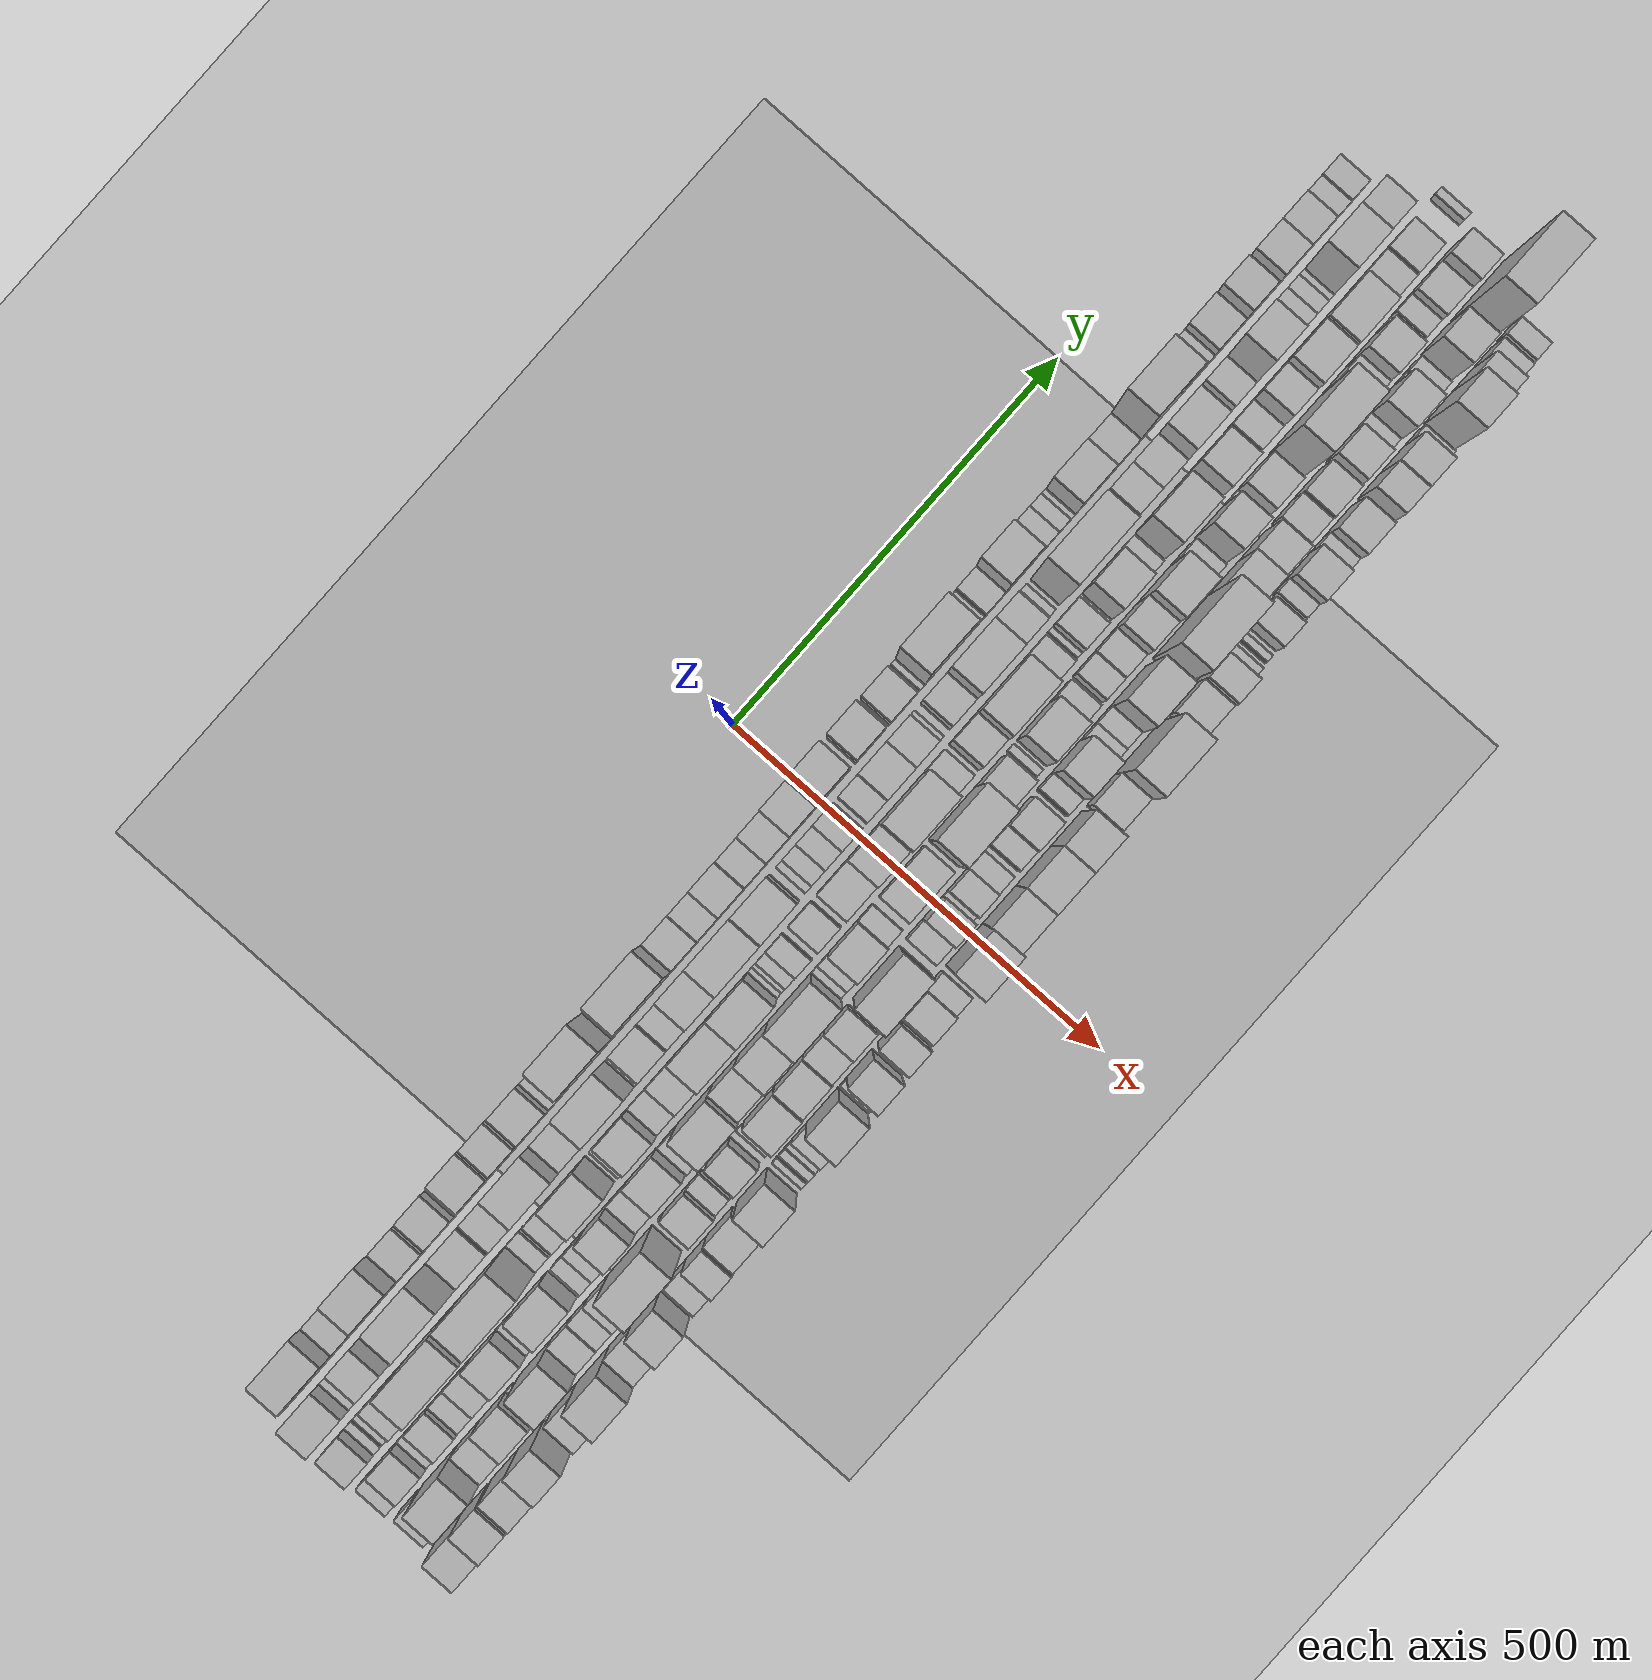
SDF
<?xml version="1.0" encoding="utf-8"?>

<sdf version="1.6">

   <world name="default">

      <gui fullscreen="0">

         <camera name="user_camera">

            <pose>-15 0 4.57585 0 0 0</pose>

            <view_controller>orbit</view_controller>

         </camera>

      </gui>

      <scene>

         <sky>

           <clouds>

             <speed>12</speed>

           </clouds>

         </sky>

         <ambient>0.4 0.4 0.4 1</ambient>

         <background>0.7 0.7 0.7 1</background>

         <shadows>1</shadows>

      </scene>

      <gravity>0 0 -9.8066</gravity>

      <magnetic_field>6e-06 2.3e-05 -4.2e-05</magnetic_field>

      <physics default="0" name="default_physics" type="ode">

         <ode>

            <solver>

               <type>quick</type>

               <iters>10</iters>

               <sor>1.0</sor>

               <use_dynamic_moi_rescaling>0</use_dynamic_moi_rescaling>

            </solver>

            <constraints>

               <cfm>0</cfm>

               <erp>0.2</erp>

               <contact_max_correcting_vel>100</contact_max_correcting_vel>

               <contact_surface_layer>0.001</contact_surface_layer>

            </constraints>

         </ode>

         <max_step_size>0.004</max_step_size>

         <real_time_factor>1</real_time_factor>

         <real_time_update_rate>250</real_time_update_rate>

      </physics>

      <light name="sun" type="directional">

         <cast_shadows>1</cast_shadows>

         <pose>0 0 10 0 0 0</pose>

         <diffuse>0.8 0.8 0.8 1</diffuse>

         <specular>0.2 0.2 0.2 1</specular>

         <attenuation>

            <range>1000</range>

            <constant>0.9</constant>

            <linear>0.01</linear>

            <quadratic>0.001</quadratic>

         </attenuation>

         <direction>-0.5 0.1 -0.9</direction>

      </light>

      <include>

         <name>ground_plane_1</name>

         <uri>model://HANNAS_ground_plane</uri>

         <pose>0 0 0  0 0 0</pose>

      </include>

      <include>

         <name>ground_plane_2</name>

         <uri>model://HANNAS_ground_plane</uri>

         <pose>100 0 0  0 0 0</pose>

      </include>

      <model name="building_1">

         <static>1</static>

         <pose frame="">100.0000 -809.6743 0 0.000000 0.000000 0.000000</pose>

         <link name="link">

            <pose frame="">0 0 22.50 0 0 0</pose>

            <collision name="collision">

               <geometry>

                  <box>

                     <size>40.0000 24.6514 45.0000</size>

                  </box>

               </geometry>

               <max_contacts>10</max_contacts>

               <surface>

                  <contact>

                     <ode/>

                  </contact>

                  <bounce/>

                  <friction>

                     <torsional>

                        <ode/>

                     </torsional>

                     <ode/>

                  </friction>

               </surface>

            </collision>

            <visual name="visual">

               <cast_shadows>0</cast_shadows>

               <geometry>

                  <box>

                     <size>40.0000 24.6514 45.0000</size>

                  </box>

               </geometry>

               <material>

                  <script>

                     <uri>model://HANNAS_wall/materials/scripts</uri>

                     <uri>model://HANNAS_wall/materials/textures</uri>

                     <name>vrc/HANNAS_wall</name>

                  </script>

               </material>

            </visual>

            <self_collide>0</self_collide>

            <enable_wind>0</enable_wind>

            <kinematic>0</kinematic>

         </link>

      </model>

      <model name="building_2">

         <static>1</static>

         <pose frame="">100.0000 -758.1193 0 0.000000 0.000000 0.000000</pose>

         <link name="link">

            <pose frame="">0 0 81.00 0 0 0</pose>

            <collision name="collision">

               <geometry>

                  <box>

                     <size>40.0000 62.4585 162.0000</size>

                  </box>

               </geometry>

               <max_contacts>10</max_contacts>

               <surface>

                  <contact>

                     <ode/>

                  </contact>

                  <bounce/>

                  <friction>

                     <torsional>

                        <ode/>

                     </torsional>

                     <ode/>

                  </friction>

               </surface>

            </collision>

            <visual name="visual">

               <cast_shadows>0</cast_shadows>

               <geometry>

                  <box>

                     <size>40.0000 62.4585 162.0000</size>

                  </box>

               </geometry>

               <material>

                  <script>

                     <uri>model://HANNAS_wall/materials/scripts</uri>

                     <uri>model://HANNAS_wall/materials/textures</uri>

                     <name>vrc/HANNAS_wall</name>

                  </script>

               </material>

            </visual>

            <self_collide>0</self_collide>

            <enable_wind>0</enable_wind>

            <kinematic>0</kinematic>

         </link>

      </model>

      <model name="building_3">

         <static>1</static>

         <pose frame="">100.0000 -709.3897 0 0.000000 0.000000 0.000000</pose>

         <link name="link">

            <pose frame="">0 0 52.50 0 0 0</pose>

            <collision name="collision">

               <geometry>

                  <box>

                     <size>40.0000 35.0008 105.0000</size>

                  </box>

               </geometry>

               <max_contacts>10</max_contacts>

               <surface>

                  <contact>

                     <ode/>

                  </contact>

                  <bounce/>

                  <friction>

                     <torsional>

                        <ode/>

                     </torsional>

                     <ode/>

                  </friction>

               </surface>

            </collision>

            <visual name="visual">

               <cast_shadows>0</cast_shadows>

               <geometry>

                  <box>

                     <size>40.0000 35.0008 105.0000</size>

                  </box>

               </geometry>

               <material>

                  <script>

                     <uri>model://HANNAS_wall/materials/scripts</uri>

                     <uri>model://HANNAS_wall/materials/textures</uri>

                     <name>vrc/HANNAS_wall</name>

                  </script>

               </material>

            </visual>

            <self_collide>0</self_collide>

            <enable_wind>0</enable_wind>

            <kinematic>0</kinematic>

         </link>

      </model>

      <model name="building_4">

         <static>1</static>

         <pose frame="">100.0000 -665.8691 0 0.000000 0.000000 0.000000</pose>

         <link name="link">

            <pose frame="">0 0 69.00 0 0 0</pose>

            <collision name="collision">

               <geometry>

                  <box>

                     <size>40.0000 52.0404 138.0000</size>

                  </box>

               </geometry>

               <max_contacts>10</max_contacts>

               <surface>

                  <contact>

                     <ode/>

                  </contact>

                  <bounce/>

                  <friction>

                     <torsional>

                        <ode/>

                     </torsional>

                     <ode/>

                  </friction>

               </surface>

            </collision>

            <visual name="visual">

               <cast_shadows>0</cast_shadows>

               <geometry>

                  <box>

                     <size>40.0000 52.0404 138.0000</size>

                  </box>

               </geometry>

               <material>

                  <script>

                     <uri>model://HANNAS_wall/materials/scripts</uri>

                     <uri>model://HANNAS_wall/materials/textures</uri>

                     <name>vrc/HANNAS_wall</name>

                  </script>

               </material>

            </visual>

            <self_collide>0</self_collide>

            <enable_wind>0</enable_wind>

            <kinematic>0</kinematic>

         </link>

      </model>

      <model name="building_5">

         <static>1</static>

         <pose frame="">100.0000 -621.6941 0 0.000000 0.000000 0.000000</pose>

         <link name="link">

            <pose frame="">0 0 31.50 0 0 0</pose>

            <collision name="collision">

               <geometry>

                  <box>

                     <size>40.0000 36.3097 63.0000</size>

                  </box>

               </geometry>

               <max_contacts>10</max_contacts>

               <surface>

                  <contact>

                     <ode/>

                  </contact>

                  <bounce/>

                  <friction>

                     <torsional>

                        <ode/>

                     </torsional>

                     <ode/>

                  </friction>

               </surface>

            </collision>

            <visual name="visual">

               <cast_shadows>0</cast_shadows>

               <geometry>

                  <box>

                     <size>40.0000 36.3097 63.0000</size>

                  </box>

               </geometry>

               <material>

                  <script>

                     <uri>model://HANNAS_wall/materials/scripts</uri>

                     <uri>model://HANNAS_wall/materials/textures</uri>

                     <name>vrc/HANNAS_wall</name>

                  </script>

               </material>

            </visual>

            <self_collide>0</self_collide>

            <enable_wind>0</enable_wind>

            <kinematic>0</kinematic>

         </link>

      </model>

      <model name="building_6">

         <static>1</static>

         <pose frame="">100.0000 -577.8411 0 0.000000 0.000000 0.000000</pose>

         <link name="link">

            <pose frame="">0 0 36.00 0 0 0</pose>

            <collision name="collision">

               <geometry>

                  <box>

                     <size>40.0000 39.3963 72.0000</size>

                  </box>

               </geometry>

               <max_contacts>10</max_contacts>

               <surface>

                  <contact>

                     <ode/>

                  </contact>

                  <bounce/>

                  <friction>

                     <torsional>

                        <ode/>

                     </torsional>

                     <ode/>

                  </friction>

               </surface>

            </collision>

            <visual name="visual">

               <cast_shadows>0</cast_shadows>

               <geometry>

                  <box>

                     <size>40.0000 39.3963 72.0000</size>

                  </box>

               </geometry>

               <material>

                  <script>

                     <uri>model://HANNAS_wall/materials/scripts</uri>

                     <uri>model://HANNAS_wall/materials/textures</uri>

                     <name>vrc/HANNAS_wall</name>

                  </script>

               </material>

            </visual>

            <self_collide>0</self_collide>

            <enable_wind>0</enable_wind>

            <kinematic>0</kinematic>

         </link>

      </model>

      <model name="building_7">

         <static>1</static>

         <pose frame="">100.0000 -548.6347 0 0.000000 0.000000 0.000000</pose>

         <link name="link">

            <pose frame="">0 0 18.00 0 0 0</pose>

            <collision name="collision">

               <geometry>

                  <box>

                     <size>40.0000 19.0165 36.0000</size>

                  </box>

               </geometry>

               <max_contacts>10</max_contacts>

               <surface>

                  <contact>

                     <ode/>

                  </contact>

                  <bounce/>

                  <friction>

                     <torsional>

                        <ode/>

                     </torsional>

                     <ode/>

                  </friction>

               </surface>

            </collision>

            <visual name="visual">

               <cast_shadows>0</cast_shadows>

               <geometry>

                  <box>

                     <size>40.0000 19.0165 36.0000</size>

                  </box>

               </geometry>

               <material>

                  <script>

                     <uri>model://HANNAS_wall/materials/scripts</uri>

                     <uri>model://HANNAS_wall/materials/textures</uri>

                     <name>vrc/HANNAS_wall</name>

                  </script>

               </material>

            </visual>

            <self_collide>0</self_collide>

            <enable_wind>0</enable_wind>

            <kinematic>0</kinematic>

         </link>

      </model>

      <model name="building_8">

         <static>1</static>

         <pose frame="">100.0000 -516.9922 0 0.000000 0.000000 0.000000</pose>

         <link name="link">

            <pose frame="">0 0 60.00 0 0 0</pose>

            <collision name="collision">

               <geometry>

                  <box>

                     <size>40.0000 44.2686 120.0000</size>

                  </box>

               </geometry>

               <max_contacts>10</max_contacts>

               <surface>

                  <contact>

                     <ode/>

                  </contact>

                  <bounce/>

                  <friction>

                     <torsional>

                        <ode/>

                     </torsional>

                     <ode/>

                  </friction>

               </surface>

            </collision>

            <visual name="visual">

               <cast_shadows>0</cast_shadows>

               <geometry>

                  <box>

                     <size>40.0000 44.2686 120.0000</size>

                  </box>

               </geometry>

               <material>

                  <script>

                     <uri>model://HANNAS_wall/materials/scripts</uri>

                     <uri>model://HANNAS_wall/materials/textures</uri>

                     <name>vrc/HANNAS_wall</name>

                  </script>

               </material>

            </visual>

            <self_collide>0</self_collide>

            <enable_wind>0</enable_wind>

            <kinematic>0</kinematic>

         </link>

      </model>

      <model name="building_9">

         <static>1</static>

         <pose frame="">100.0000 -476.2714 0 0.000000 0.000000 0.000000</pose>

         <link name="link">

            <pose frame="">0 0 51.00 0 0 0</pose>

            <collision name="collision">

               <geometry>

                  <box>

                     <size>40.0000 37.1730 102.0000</size>

                  </box>

               </geometry>

               <max_contacts>10</max_contacts>

               <surface>

                  <contact>

                     <ode/>

                  </contact>

                  <bounce/>

                  <friction>

                     <torsional>

                        <ode/>

                     </torsional>

                     <ode/>

                  </friction>

               </surface>

            </collision>

            <visual name="visual">

               <cast_shadows>0</cast_shadows>

               <geometry>

                  <box>

                     <size>40.0000 37.1730 102.0000</size>

                  </box>

               </geometry>

               <material>

                  <script>

                     <uri>model://HANNAS_wall/materials/scripts</uri>

                     <uri>model://HANNAS_wall/materials/textures</uri>

                     <name>vrc/HANNAS_wall</name>

                  </script>

               </material>

            </visual>

            <self_collide>0</self_collide>

            <enable_wind>0</enable_wind>

            <kinematic>0</kinematic>

         </link>

      </model>

      <model name="building_10">

         <static>1</static>

         <pose frame="">100.0000 -436.0106 0 0.000000 0.000000 0.000000</pose>

         <link name="link">

            <pose frame="">0 0 39.00 0 0 0</pose>

            <collision name="collision">

               <geometry>

                  <box>

                     <size>40.0000 43.3484 78.0000</size>

                  </box>

               </geometry>

               <max_contacts>10</max_contacts>

               <surface>

                  <contact>

                     <ode/>

                  </contact>

                  <bounce/>

                  <friction>

                     <torsional>

                        <ode/>

                     </torsional>

                     <ode/>

                  </friction>

               </surface>

            </collision>

            <visual name="visual">

               <cast_shadows>0</cast_shadows>

               <geometry>

                  <box>

                     <size>40.0000 43.3484 78.0000</size>

                  </box>

               </geometry>

               <material>

                  <script>

                     <uri>model://HANNAS_wall/materials/scripts</uri>

                     <uri>model://HANNAS_wall/materials/textures</uri>

                     <name>vrc/HANNAS_wall</name>

                  </script>

               </material>

            </visual>

            <self_collide>0</self_collide>

            <enable_wind>0</enable_wind>

            <kinematic>0</kinematic>

         </link>

      </model>

      <model name="building_11">

         <static>1</static>

         <pose frame="">100.0000 -402.8972 0 0.000000 0.000000 0.000000</pose>

         <link name="link">

            <pose frame="">0 0 21.00 0 0 0</pose>

            <collision name="collision">

               <geometry>

                  <box>

                     <size>40.0000 22.8785 42.0000</size>

                  </box>

               </geometry>

               <max_contacts>10</max_contacts>

               <surface>

                  <contact>

                     <ode/>

                  </contact>

                  <bounce/>

                  <friction>

                     <torsional>

                        <ode/>

                     </torsional>

                     <ode/>

                  </friction>

               </surface>

            </collision>

            <visual name="visual">

               <cast_shadows>0</cast_shadows>

               <geometry>

                  <box>

                     <size>40.0000 22.8785 42.0000</size>

                  </box>

               </geometry>

               <material>

                  <script>

                     <uri>model://HANNAS_wall/materials/scripts</uri>

                     <uri>model://HANNAS_wall/materials/textures</uri>

                     <name>vrc/HANNAS_wall</name>

                  </script>

               </material>

            </visual>

            <self_collide>0</self_collide>

            <enable_wind>0</enable_wind>

            <kinematic>0</kinematic>

         </link>

      </model>

      <model name="building_12">

         <static>1</static>

         <pose frame="">100.0000 -350.8258 0 0.000000 0.000000 0.000000</pose>

         <link name="link">

            <pose frame="">0 0 97.50 0 0 0</pose>

            <collision name="collision">

               <geometry>

                  <box>

                     <size>40.0000 63.2641 195.0000</size>

                  </box>

               </geometry>

               <max_contacts>10</max_contacts>

               <surface>

                  <contact>

                     <ode/>

                  </contact>

                  <bounce/>

                  <friction>

                     <torsional>

                        <ode/>

                     </torsional>

                     <ode/>

                  </friction>

               </surface>

            </collision>

            <visual name="visual">

               <cast_shadows>0</cast_shadows>

               <geometry>

                  <box>

                     <size>40.0000 63.2641 195.0000</size>

                  </box>

               </geometry>

               <material>

                  <script>

                     <uri>model://HANNAS_wall/materials/scripts</uri>

                     <uri>model://HANNAS_wall/materials/textures</uri>

                     <name>vrc/HANNAS_wall</name>

                  </script>

               </material>

            </visual>

            <self_collide>0</self_collide>

            <enable_wind>0</enable_wind>

            <kinematic>0</kinematic>

         </link>

      </model>

      <model name="building_13">

         <static>1</static>

         <pose frame="">100.0000 -309.3553 0 0.000000 0.000000 0.000000</pose>

         <link name="link">

            <pose frame="">0 0 16.50 0 0 0</pose>

            <collision name="collision">

               <geometry>

                  <box>

                     <size>40.0000 19.6770 33.0000</size>

                  </box>

               </geometry>

               <max_contacts>10</max_contacts>

               <surface>

                  <contact>

                     <ode/>

                  </contact>

                  <bounce/>

                  <friction>

                     <torsional>

                        <ode/>

                     </torsional>

                     <ode/>

                  </friction>

               </surface>

            </collision>

            <visual name="visual">

               <cast_shadows>0</cast_shadows>

               <geometry>

                  <box>

                     <size>40.0000 19.6770 33.0000</size>

                  </box>

               </geometry>

               <material>

                  <script>

                     <uri>model://HANNAS_wall/materials/scripts</uri>

                     <uri>model://HANNAS_wall/materials/textures</uri>

                     <name>vrc/HANNAS_wall</name>

                  </script>

               </material>

            </visual>

            <self_collide>0</self_collide>

            <enable_wind>0</enable_wind>

            <kinematic>0</kinematic>

         </link>

      </model>

      <model name="building_14">

         <static>1</static>

         <pose frame="">100.0000 -262.9560 0 0.000000 0.000000 0.000000</pose>

         <link name="link">

            <pose frame="">0 0 96.00 0 0 0</pose>

            <collision name="collision">

               <geometry>

                  <box>

                     <size>40.0000 73.1216 192.0000</size>

                  </box>

               </geometry>

               <max_contacts>10</max_contacts>

               <surface>

                  <contact>

                     <ode/>

                  </contact>

                  <bounce/>

                  <friction>

                     <torsional>

                        <ode/>

                     </torsional>

                     <ode/>

                  </friction>

               </surface>

            </collision>

            <visual name="visual">

               <cast_shadows>0</cast_shadows>

               <geometry>

                  <box>

                     <size>40.0000 73.1216 192.0000</size>

                  </box>

               </geometry>

               <material>

                  <script>

                     <uri>model://HANNAS_wall/materials/scripts</uri>

                     <uri>model://HANNAS_wall/materials/textures</uri>

                     <name>vrc/HANNAS_wall</name>

                  </script>

               </material>

            </visual>

            <self_collide>0</self_collide>

            <enable_wind>0</enable_wind>

            <kinematic>0</kinematic>

         </link>

      </model>

      <model name="building_15">

         <static>1</static>

         <pose frame="">100.0000 -206.9353 0 0.000000 0.000000 0.000000</pose>

         <link name="link">

            <pose frame="">0 0 34.50 0 0 0</pose>

            <collision name="collision">

               <geometry>

                  <box>

                     <size>40.0000 38.9199 69.0000</size>

                  </box>

               </geometry>

               <max_contacts>10</max_contacts>

               <surface>

                  <contact>

                     <ode/>

                  </contact>

                  <bounce/>

                  <friction>

                     <torsional>

                        <ode/>

                     </torsional>

                     <ode/>

                  </friction>

               </surface>

            </collision>

            <visual name="visual">

               <cast_shadows>0</cast_shadows>

               <geometry>

                  <box>

                     <size>40.0000 38.9199 69.0000</size>

                  </box>

               </geometry>

               <material>

                  <script>

                     <uri>model://HANNAS_wall/materials/scripts</uri>

                     <uri>model://HANNAS_wall/materials/textures</uri>

                     <name>vrc/HANNAS_wall</name>

                  </script>

               </material>

            </visual>

            <self_collide>0</self_collide>

            <enable_wind>0</enable_wind>

            <kinematic>0</kinematic>

         </link>

      </model>

      <model name="building_16">

         <static>1</static>

         <pose frame="">100.0000 -171.5780 0 0.000000 0.000000 0.000000</pose>

         <link name="link">

            <pose frame="">0 0 31.50 0 0 0</pose>

            <collision name="collision">

               <geometry>

                  <box>

                     <size>40.0000 31.7946 63.0000</size>

                  </box>

               </geometry>

               <max_contacts>10</max_contacts>

               <surface>

                  <contact>

                     <ode/>

                  </contact>

                  <bounce/>

                  <friction>

                     <torsional>

                        <ode/>

                     </torsional>

                     <ode/>

                  </friction>

               </surface>

            </collision>

            <visual name="visual">

               <cast_shadows>0</cast_shadows>

               <geometry>

                  <box>

                     <size>40.0000 31.7946 63.0000</size>

                  </box>

               </geometry>

               <material>

                  <script>

                     <uri>model://HANNAS_wall/materials/scripts</uri>

                     <uri>model://HANNAS_wall/materials/textures</uri>

                     <name>vrc/HANNAS_wall</name>

                  </script>

               </material>

            </visual>

            <self_collide>0</self_collide>

            <enable_wind>0</enable_wind>

            <kinematic>0</kinematic>

         </link>

      </model>

      <model name="building_17">

         <static>1</static>

         <pose frame="">100.0000 -135.9647 0 0.000000 0.000000 0.000000</pose>

         <link name="link">

            <pose frame="">0 0 36.00 0 0 0</pose>

            <collision name="collision">

               <geometry>

                  <box>

                     <size>40.0000 39.4321 72.0000</size>

                  </box>

               </geometry>

               <max_contacts>10</max_contacts>

               <surface>

                  <contact>

                     <ode/>

                  </contact>

                  <bounce/>

                  <friction>

                     <torsional>

                        <ode/>

                     </torsional>

                     <ode/>

                  </friction>

               </surface>

            </collision>

            <visual name="visual">

               <cast_shadows>0</cast_shadows>

               <geometry>

                  <box>

                     <size>40.0000 39.4321 72.0000</size>

                  </box>

               </geometry>

               <material>

                  <script>

                     <uri>model://HANNAS_wall/materials/scripts</uri>

                     <uri>model://HANNAS_wall/materials/textures</uri>

                     <name>vrc/HANNAS_wall</name>

                  </script>

               </material>

            </visual>

            <self_collide>0</self_collide>

            <enable_wind>0</enable_wind>

            <kinematic>0</kinematic>

         </link>

      </model>

      <model name="building_18">

         <static>1</static>

         <pose frame="">100.0000 -99.7300 0 0.000000 0.000000 0.000000</pose>

         <link name="link">

            <pose frame="">0 0 28.50 0 0 0</pose>

            <collision name="collision">

               <geometry>

                  <box>

                     <size>40.0000 33.0373 57.0000</size>

                  </box>

               </geometry>

               <max_contacts>10</max_contacts>

               <surface>

                  <contact>

                     <ode/>

                  </contact>

                  <bounce/>

                  <friction>

                     <torsional>

                        <ode/>

                     </torsional>

                     <ode/>

                  </friction>

               </surface>

            </collision>

            <visual name="visual">

               <cast_shadows>0</cast_shadows>

               <geometry>

                  <box>

                     <size>40.0000 33.0373 57.0000</size>

                  </box>

               </geometry>

               <material>

                  <script>

                     <uri>model://HANNAS_wall/materials/scripts</uri>

                     <uri>model://HANNAS_wall/materials/textures</uri>

                     <name>vrc/HANNAS_wall</name>

                  </script>

               </material>

            </visual>

            <self_collide>0</self_collide>

            <enable_wind>0</enable_wind>

            <kinematic>0</kinematic>

         </link>

      </model>

      <model name="building_19">

         <static>1</static>

         <pose frame="">100.0000 -65.4250 0 0.000000 0.000000 0.000000</pose>

         <link name="link">

            <pose frame="">0 0 34.50 0 0 0</pose>

            <collision name="collision">

               <geometry>

                  <box>

                     <size>40.0000 35.5727 69.0000</size>

                  </box>

               </geometry>

               <max_contacts>10</max_contacts>

               <surface>

                  <contact>

                     <ode/>

                  </contact>

                  <bounce/>

                  <friction>

                     <torsional>

                        <ode/>

                     </torsional>

                     <ode/>

                  </friction>

               </surface>

            </collision>

            <visual name="visual">

               <cast_shadows>0</cast_shadows>

               <geometry>

                  <box>

                     <size>40.0000 35.5727 69.0000</size>

                  </box>

               </geometry>

               <material>

                  <script>

                     <uri>model://HANNAS_wall/materials/scripts</uri>

                     <uri>model://HANNAS_wall/materials/textures</uri>

                     <name>vrc/HANNAS_wall</name>

                  </script>

               </material>

            </visual>

            <self_collide>0</self_collide>

            <enable_wind>0</enable_wind>

            <kinematic>0</kinematic>

         </link>

      </model>

      <model name="building_20">

         <static>1</static>

         <pose frame="">100.0000 -27.6505 0 0.000000 0.000000 0.000000</pose>

         <link name="link">

            <pose frame="">0 0 51.00 0 0 0</pose>

            <collision name="collision">

               <geometry>

                  <box>

                     <size>40.0000 39.9763 102.0000</size>

                  </box>

               </geometry>

               <max_contacts>10</max_contacts>

               <surface>

                  <contact>

                     <ode/>

                  </contact>

                  <bounce/>

                  <friction>

                     <torsional>

                        <ode/>

                     </torsional>

                     <ode/>

                  </friction>

               </surface>

            </collision>

            <visual name="visual">

               <cast_shadows>0</cast_shadows>

               <geometry>

                  <box>

                     <size>40.0000 39.9763 102.0000</size>

                  </box>

               </geometry>

               <material>

                  <script>

                     <uri>model://HANNAS_wall/materials/scripts</uri>

                     <uri>model://HANNAS_wall/materials/textures</uri>

                     <name>vrc/HANNAS_wall</name>

                  </script>

               </material>

            </visual>

            <self_collide>0</self_collide>

            <enable_wind>0</enable_wind>

            <kinematic>0</kinematic>

         </link>

      </model>

      <model name="building_21">

         <static>1</static>

         <pose frame="">100.0000 18.9838 0 0.000000 0.000000 0.000000</pose>

         <link name="link">

            <pose frame="">0 0 75.00 0 0 0</pose>

            <collision name="collision">

               <geometry>

                  <box>

                     <size>40.0000 47.2922 150.0000</size>

                  </box>

               </geometry>

               <max_contacts>10</max_contacts>

               <surface>

                  <contact>

                     <ode/>

                  </contact>

                  <bounce/>

                  <friction>

                     <torsional>

                        <ode/>

                     </torsional>

                     <ode/>

                  </friction>

               </surface>

            </collision>

            <visual name="visual">

               <cast_shadows>0</cast_shadows>

               <geometry>

                  <box>

                     <size>40.0000 47.2922 150.0000</size>

                  </box>

               </geometry>

               <material>

                  <script>

                     <uri>model://HANNAS_wall/materials/scripts</uri>

                     <uri>model://HANNAS_wall/materials/textures</uri>

                     <name>vrc/HANNAS_wall</name>

                  </script>

               </material>

            </visual>

            <self_collide>0</self_collide>

            <enable_wind>0</enable_wind>

            <kinematic>0</kinematic>

         </link>

      </model>

      <model name="building_22">

         <static>1</static>

         <pose frame="">100.0000 74.6798 0 0.000000 0.000000 0.000000</pose>

         <link name="link">

            <pose frame="">0 0 57.00 0 0 0</pose>

            <collision name="collision">

               <geometry>

                  <box>

                     <size>40.0000 44.0999 114.0000</size>

                  </box>

               </geometry>

               <max_contacts>10</max_contacts>

               <surface>

                  <contact>

                     <ode/>

                  </contact>

                  <bounce/>

                  <friction>

                     <torsional>

                        <ode/>

                     </torsional>

                     <ode/>

                  </friction>

               </surface>

            </collision>

            <visual name="visual">

               <cast_shadows>0</cast_shadows>

               <geometry>

                  <box>

                     <size>40.0000 44.0999 114.0000</size>

                  </box>

               </geometry>

               <material>

                  <script>

                     <uri>model://HANNAS_wall/materials/scripts</uri>

                     <uri>model://HANNAS_wall/materials/textures</uri>

                     <name>vrc/HANNAS_wall</name>

                  </script>

               </material>

            </visual>

            <self_collide>0</self_collide>

            <enable_wind>0</enable_wind>

            <kinematic>0</kinematic>

         </link>

      </model>

      <model name="building_23">

         <static>1</static>

         <pose frame="">100.0000 124.8819 0 0.000000 0.000000 0.000000</pose>

         <link name="link">

            <pose frame="">0 0 36.00 0 0 0</pose>

            <collision name="collision">

               <geometry>

                  <box>

                     <size>40.0000 40.3041 72.0000</size>

                  </box>

               </geometry>

               <max_contacts>10</max_contacts>

               <surface>

                  <contact>

                     <ode/>

                  </contact>

                  <bounce/>

                  <friction>

                     <torsional>

                        <ode/>

                     </torsional>

                     <ode/>

                  </friction>

               </surface>

            </collision>

            <visual name="visual">

               <cast_shadows>0</cast_shadows>

               <geometry>

                  <box>

                     <size>40.0000 40.3041 72.0000</size>

                  </box>

               </geometry>

               <material>

                  <script>

                     <uri>model://HANNAS_wall/materials/scripts</uri>

                     <uri>model://HANNAS_wall/materials/textures</uri>

                     <name>vrc/HANNAS_wall</name>

                  </script>

               </material>

            </visual>

            <self_collide>0</self_collide>

            <enable_wind>0</enable_wind>

            <kinematic>0</kinematic>

         </link>

      </model>

      <model name="building_24">

         <static>1</static>

         <pose frame="">100.0000 154.7181 0 0.000000 0.000000 0.000000</pose>

         <link name="link">

            <pose frame="">0 0 9.00 0 0 0</pose>

            <collision name="collision">

               <geometry>

                  <box>

                     <size>40.0000 7.3683 18.0000</size>

                  </box>

               </geometry>

               <max_contacts>10</max_contacts>

               <surface>

                  <contact>

                     <ode/>

                  </contact>

                  <bounce/>

                  <friction>

                     <torsional>

                        <ode/>

                     </torsional>

                     <ode/>

                  </friction>

               </surface>

            </collision>

            <visual name="visual">

               <cast_shadows>0</cast_shadows>

               <geometry>

                  <box>

                     <size>40.0000 7.3683 18.0000</size>

                  </box>

               </geometry>

               <material>

                  <script>

                     <uri>model://HANNAS_wall/materials/scripts</uri>

                     <uri>model://HANNAS_wall/materials/textures</uri>

                     <name>vrc/HANNAS_wall</name>

                  </script>

               </material>

            </visual>

            <self_collide>0</self_collide>

            <enable_wind>0</enable_wind>

            <kinematic>0</kinematic>

         </link>

      </model>

      <model name="building_25">

         <static>1</static>

         <pose frame="">100.0000 193.5216 0 0.000000 0.000000 0.000000</pose>

         <link name="link">

            <pose frame="">0 0 94.50 0 0 0</pose>

            <collision name="collision">

               <geometry>

                  <box>

                     <size>40.0000 70.2388 189.0000</size>

                  </box>

               </geometry>

               <max_contacts>10</max_contacts>

               <surface>

                  <contact>

                     <ode/>

                  </contact>

                  <bounce/>

                  <friction>

                     <torsional>

                        <ode/>

                     </torsional>

                     <ode/>

                  </friction>

               </surface>

            </collision>

            <visual name="visual">

               <cast_shadows>0</cast_shadows>

               <geometry>

                  <box>

                     <size>40.0000 70.2388 189.0000</size>

                  </box>

               </geometry>

               <material>

                  <script>

                     <uri>model://HANNAS_wall/materials/scripts</uri>

                     <uri>model://HANNAS_wall/materials/textures</uri>

                     <name>vrc/HANNAS_wall</name>

                  </script>

               </material>

            </visual>

            <self_collide>0</self_collide>

            <enable_wind>0</enable_wind>

            <kinematic>0</kinematic>

         </link>

      </model>

      <model name="building_26">

         <static>1</static>

         <pose frame="">100.0000 240.4737 0 0.000000 0.000000 0.000000</pose>

         <link name="link">

            <pose frame="">0 0 16.50 0 0 0</pose>

            <collision name="collision">

               <geometry>

                  <box>

                     <size>40.0000 17.6654 33.0000</size>

                  </box>

               </geometry>

               <max_contacts>10</max_contacts>

               <surface>

                  <contact>

                     <ode/>

                  </contact>

                  <bounce/>

                  <friction>

                     <torsional>

                        <ode/>

                     </torsional>

                     <ode/>

                  </friction>

               </surface>

            </collision>

            <visual name="visual">

               <cast_shadows>0</cast_shadows>

               <geometry>

                  <box>

                     <size>40.0000 17.6654 33.0000</size>

                  </box>

               </geometry>

               <material>

                  <script>

                     <uri>model://HANNAS_wall/materials/scripts</uri>

                     <uri>model://HANNAS_wall/materials/textures</uri>

                     <name>vrc/HANNAS_wall</name>

                  </script>

               </material>

            </visual>

            <self_collide>0</self_collide>

            <enable_wind>0</enable_wind>

            <kinematic>0</kinematic>

         </link>

      </model>

      <model name="building_27">

         <static>1</static>

         <pose frame="">100.0000 264.1507 0 0.000000 0.000000 0.000000</pose>

         <link name="link">

            <pose frame="">0 0 28.50 0 0 0</pose>

            <collision name="collision">

               <geometry>

                  <box>

                     <size>40.0000 29.6887 57.0000</size>

                  </box>

               </geometry>

               <max_contacts>10</max_contacts>

               <surface>

                  <contact>

                     <ode/>

                  </contact>

                  <bounce/>

                  <friction>

                     <torsional>

                        <ode/>

                     </torsional>

                     <ode/>

                  </friction>

               </surface>

            </collision>

            <visual name="visual">

               <cast_shadows>0</cast_shadows>

               <geometry>

                  <box>

                     <size>40.0000 29.6887 57.0000</size>

                  </box>

               </geometry>

               <material>

                  <script>

                     <uri>model://HANNAS_wall/materials/scripts</uri>

                     <uri>model://HANNAS_wall/materials/textures</uri>

                     <name>vrc/HANNAS_wall</name>

                  </script>

               </material>

            </visual>

            <self_collide>0</self_collide>

            <enable_wind>0</enable_wind>

            <kinematic>0</kinematic>

         </link>

      </model>

      <model name="building_28">

         <static>1</static>

         <pose frame="">100.0000 303.5925 0 0.000000 0.000000 0.000000</pose>

         <link name="link">

            <pose frame="">0 0 70.50 0 0 0</pose>

            <collision name="collision">

               <geometry>

                  <box>

                     <size>40.0000 49.1949 141.0000</size>

                  </box>

               </geometry>

               <max_contacts>10</max_contacts>

               <surface>

                  <contact>

                     <ode/>

                  </contact>

                  <bounce/>

                  <friction>

                     <torsional>

                        <ode/>

                     </torsional>

                     <ode/>

                  </friction>

               </surface>

            </collision>

            <visual name="visual">

               <cast_shadows>0</cast_shadows>

               <geometry>

                  <box>

                     <size>40.0000 49.1949 141.0000</size>

                  </box>

               </geometry>

               <material>

                  <script>

                     <uri>model://HANNAS_wall/materials/scripts</uri>

                     <uri>model://HANNAS_wall/materials/textures</uri>

                     <name>vrc/HANNAS_wall</name>

                  </script>

               </material>

            </visual>

            <self_collide>0</self_collide>

            <enable_wind>0</enable_wind>

            <kinematic>0</kinematic>

         </link>

      </model>

      <model name="building_29">

         <static>1</static>

         <pose frame="">100.0000 349.4941 0 0.000000 0.000000 0.000000</pose>

         <link name="link">

            <pose frame="">0 0 21.00 0 0 0</pose>

            <collision name="collision">

               <geometry>

                  <box>

                     <size>40.0000 24.6083 42.0000</size>

                  </box>

               </geometry>

               <max_contacts>10</max_contacts>

               <surface>

                  <contact>

                     <ode/>

                  </contact>

                  <bounce/>

                  <friction>

                     <torsional>

                        <ode/>

                     </torsional>

                     <ode/>

                  </friction>

               </surface>

            </collision>

            <visual name="visual">

               <cast_shadows>0</cast_shadows>

               <geometry>

                  <box>

                     <size>40.0000 24.6083 42.0000</size>

                  </box>

               </geometry>

               <material>

                  <script>

                     <uri>model://HANNAS_wall/materials/scripts</uri>

                     <uri>model://HANNAS_wall/materials/textures</uri>

                     <name>vrc/HANNAS_wall</name>

                  </script>

               </material>

            </visual>

            <self_collide>0</self_collide>

            <enable_wind>0</enable_wind>

            <kinematic>0</kinematic>

         </link>

      </model>

      <model name="building_30">

         <static>1</static>

         <pose frame="">100.0000 371.0547 0 0.000000 0.000000 0.000000</pose>

         <link name="link">

            <pose frame="">0 0 16.50 0 0 0</pose>

            <collision name="collision">

               <geometry>

                  <box>

                     <size>40.0000 18.5130 33.0000</size>

                  </box>

               </geometry>

               <max_contacts>10</max_contacts>

               <surface>

                  <contact>

                     <ode/>

                  </contact>

                  <bounce/>

                  <friction>

                     <torsional>

                        <ode/>

                     </torsional>

                     <ode/>

                  </friction>

               </surface>

            </collision>

            <visual name="visual">

               <cast_shadows>0</cast_shadows>

               <geometry>

                  <box>

                     <size>40.0000 18.5130 33.0000</size>

                  </box>

               </geometry>

               <material>

                  <script>

                     <uri>model://HANNAS_wall/materials/scripts</uri>

                     <uri>model://HANNAS_wall/materials/textures</uri>

                     <name>vrc/HANNAS_wall</name>

                  </script>

               </material>

            </visual>

            <self_collide>0</self_collide>

            <enable_wind>0</enable_wind>

            <kinematic>0</kinematic>

         </link>

      </model>

      <model name="building_31">

         <static>1</static>

         <pose frame="">100.0000 384.6112 0 0.000000 0.000000 0.000000</pose>

         <link name="link">

            <pose frame="">0 0 9.00 0 0 0</pose>

            <collision name="collision">

               <geometry>

                  <box>

                     <size>40.0000 8.6000 18.0000</size>

                  </box>

               </geometry>

               <max_contacts>10</max_contacts>

               <surface>

                  <contact>

                     <ode/>

                  </contact>

                  <bounce/>

                  <friction>

                     <torsional>

                        <ode/>

                     </torsional>

                     <ode/>

                  </friction>

               </surface>

            </collision>

            <visual name="visual">

               <cast_shadows>0</cast_shadows>

               <geometry>

                  <box>

                     <size>40.0000 8.6000 18.0000</size>

                  </box>

               </geometry>

               <material>

                  <script>

                     <uri>model://HANNAS_wall/materials/scripts</uri>

                     <uri>model://HANNAS_wall/materials/textures</uri>

                     <name>vrc/HANNAS_wall</name>

                  </script>

               </material>

            </visual>

            <self_collide>0</self_collide>

            <enable_wind>0</enable_wind>

            <kinematic>0</kinematic>

         </link>

      </model>

      <model name="building_32">

         <static>1</static>

         <pose frame="">100.0000 417.4044 0 0.000000 0.000000 0.000000</pose>

         <link name="link">

            <pose frame="">0 0 45.00 0 0 0</pose>

            <collision name="collision">

               <geometry>

                  <box>

                     <size>40.0000 50.9864 90.0000</size>

                  </box>

               </geometry>

               <max_contacts>10</max_contacts>

               <surface>

                  <contact>

                     <ode/>

                  </contact>

                  <bounce/>

                  <friction>

                     <torsional>

                        <ode/>

                     </torsional>

                     <ode/>

                  </friction>

               </surface>

            </collision>

            <visual name="visual">

               <cast_shadows>0</cast_shadows>

               <geometry>

                  <box>

                     <size>40.0000 50.9864 90.0000</size>

                  </box>

               </geometry>

               <material>

                  <script>

                     <uri>model://HANNAS_wall/materials/scripts</uri>

                     <uri>model://HANNAS_wall/materials/textures</uri>

                     <name>vrc/HANNAS_wall</name>

                  </script>

               </material>

            </visual>

            <self_collide>0</self_collide>

            <enable_wind>0</enable_wind>

            <kinematic>0</kinematic>

         </link>

      </model>

      <model name="building_33">

         <static>1</static>

         <pose frame="">100.0000 463.8958 0 0.000000 0.000000 0.000000</pose>

         <link name="link">

            <pose frame="">0 0 31.50 0 0 0</pose>

            <collision name="collision">

               <geometry>

                  <box>

                     <size>40.0000 35.9964 63.0000</size>

                  </box>

               </geometry>

               <max_contacts>10</max_contacts>

               <surface>

                  <contact>

                     <ode/>

                  </contact>

                  <bounce/>

                  <friction>

                     <torsional>

                        <ode/>

                     </torsional>

                     <ode/>

                  </friction>

               </surface>

            </collision>

            <visual name="visual">

               <cast_shadows>0</cast_shadows>

               <geometry>

                  <box>

                     <size>40.0000 35.9964 63.0000</size>

                  </box>

               </geometry>

               <material>

                  <script>

                     <uri>model://HANNAS_wall/materials/scripts</uri>

                     <uri>model://HANNAS_wall/materials/textures</uri>

                     <name>vrc/HANNAS_wall</name>

                  </script>

               </material>

            </visual>

            <self_collide>0</self_collide>

            <enable_wind>0</enable_wind>

            <kinematic>0</kinematic>

         </link>

      </model>

      <model name="building_34">

         <static>1</static>

         <pose frame="">100.0000 516.1357 0 0.000000 0.000000 0.000000</pose>

         <link name="link">

            <pose frame="">0 0 103.50 0 0 0</pose>

            <collision name="collision">

               <geometry>

                  <box>

                     <size>40.0000 68.4833 207.0000</size>

                  </box>

               </geometry>

               <max_contacts>10</max_contacts>

               <surface>

                  <contact>

                     <ode/>

                  </contact>

                  <bounce/>

                  <friction>

                     <torsional>

                        <ode/>

                     </torsional>

                     <ode/>

                  </friction>

               </surface>

            </collision>

            <visual name="visual">

               <cast_shadows>0</cast_shadows>

               <geometry>

                  <box>

                     <size>40.0000 68.4833 207.0000</size>

                  </box>

               </geometry>

               <material>

                  <script>

                     <uri>model://HANNAS_wall/materials/scripts</uri>

                     <uri>model://HANNAS_wall/materials/textures</uri>

                     <name>vrc/HANNAS_wall</name>

                  </script>

               </material>

            </visual>

            <self_collide>0</self_collide>

            <enable_wind>0</enable_wind>

            <kinematic>0</kinematic>

         </link>

      </model>

      <model name="building_35">

         <static>1</static>

         <pose frame="">100.0000 570.4830 0 0.000000 0.000000 0.000000</pose>

         <link name="link">

            <pose frame="">0 0 37.50 0 0 0</pose>

            <collision name="collision">

               <geometry>

                  <box>

                     <size>40.0000 40.2113 75.0000</size>

                  </box>

               </geometry>

               <max_contacts>10</max_contacts>

               <surface>

                  <contact>

                     <ode/>

                  </contact>

                  <bounce/>

                  <friction>

                     <torsional>

                        <ode/>

                     </torsional>

                     <ode/>

                  </friction>

               </surface>

            </collision>

            <visual name="visual">

               <cast_shadows>0</cast_shadows>

               <geometry>

                  <box>

                     <size>40.0000 40.2113 75.0000</size>

                  </box>

               </geometry>

               <material>

                  <script>

                     <uri>model://HANNAS_wall/materials/scripts</uri>

                     <uri>model://HANNAS_wall/materials/textures</uri>

                     <name>vrc/HANNAS_wall</name>

                  </script>

               </material>

            </visual>

            <self_collide>0</self_collide>

            <enable_wind>0</enable_wind>

            <kinematic>0</kinematic>

         </link>

      </model>

      <model name="building_36">

         <static>1</static>

         <pose frame="">100.0000 611.0884 0 0.000000 0.000000 0.000000</pose>

         <link name="link">

            <pose frame="">0 0 52.50 0 0 0</pose>

            <collision name="collision">

               <geometry>

                  <box>

                     <size>40.0000 40.9995 105.0000</size>

                  </box>

               </geometry>

               <max_contacts>10</max_contacts>

               <surface>

                  <contact>

                     <ode/>

                  </contact>

                  <bounce/>

                  <friction>

                     <torsional>

                        <ode/>

                     </torsional>

                     <ode/>

                  </friction>

               </surface>

            </collision>

            <visual name="visual">

               <cast_shadows>0</cast_shadows>

               <geometry>

                  <box>

                     <size>40.0000 40.9995 105.0000</size>

                  </box>

               </geometry>

               <material>

                  <script>

                     <uri>model://HANNAS_wall/materials/scripts</uri>

                     <uri>model://HANNAS_wall/materials/textures</uri>

                     <name>vrc/HANNAS_wall</name>

                  </script>

               </material>

            </visual>

            <self_collide>0</self_collide>

            <enable_wind>0</enable_wind>

            <kinematic>0</kinematic>

         </link>

      </model>

      <model name="building_37">

         <static>1</static>

         <pose frame="">100.0000 658.7133 0 0.000000 0.000000 0.000000</pose>

         <link name="link">

            <pose frame="">0 0 57.00 0 0 0</pose>

            <collision name="collision">

               <geometry>

                  <box>

                     <size>40.0000 38.2504 114.0000</size>

                  </box>

               </geometry>

               <max_contacts>10</max_contacts>

               <surface>

                  <contact>

                     <ode/>

                  </contact>

                  <bounce/>

                  <friction>

                     <torsional>

                        <ode/>

                     </torsional>

                     <ode/>

                  </friction>

               </surface>

            </collision>

            <visual name="visual">

               <cast_shadows>0</cast_shadows>

               <geometry>

                  <box>

                     <size>40.0000 38.2504 114.0000</size>

                  </box>

               </geometry>

               <material>

                  <script>

                     <uri>model://HANNAS_wall/materials/scripts</uri>

                     <uri>model://HANNAS_wall/materials/textures</uri>

                     <name>vrc/HANNAS_wall</name>

                  </script>

               </material>

            </visual>

            <self_collide>0</self_collide>

            <enable_wind>0</enable_wind>

            <kinematic>0</kinematic>

         </link>

      </model>

      <model name="building_38">

         <static>1</static>

         <pose frame="">100.0000 686.2303 0 0.000000 0.000000 0.000000</pose>

         <link name="link">

            <pose frame="">0 0 9.00 0 0 0</pose>

            <collision name="collision">

               <geometry>

                  <box>

                     <size>40.0000 8.7835 18.0000</size>

                  </box>

               </geometry>

               <max_contacts>10</max_contacts>

               <surface>

                  <contact>

                     <ode/>

                  </contact>

                  <bounce/>

                  <friction>

                     <torsional>

                        <ode/>

                     </torsional>

                     <ode/>

                  </friction>

               </surface>

            </collision>

            <visual name="visual">

               <cast_shadows>0</cast_shadows>

               <geometry>

                  <box>

                     <size>40.0000 8.7835 18.0000</size>

                  </box>

               </geometry>

               <material>

                  <script>

                     <uri>model://HANNAS_wall/materials/scripts</uri>

                     <uri>model://HANNAS_wall/materials/textures</uri>

                     <name>vrc/HANNAS_wall</name>

                  </script>

               </material>

            </visual>

            <self_collide>0</self_collide>

            <enable_wind>0</enable_wind>

            <kinematic>0</kinematic>

         </link>

      </model>

      <model name="building_39">

         <static>1</static>

         <pose frame="">100.0000 717.5890 0 0.000000 0.000000 0.000000</pose>

         <link name="link">

            <pose frame="">0 0 37.50 0 0 0</pose>

            <collision name="collision">

               <geometry>

                  <box>

                     <size>40.0000 39.9340 75.0000</size>

                  </box>

               </geometry>

               <max_contacts>10</max_contacts>

               <surface>

                  <contact>

                     <ode/>

                  </contact>

                  <bounce/>

                  <friction>

                     <torsional>

                        <ode/>

                     </torsional>

                     <ode/>

                  </friction>

               </surface>

            </collision>

            <visual name="visual">

               <cast_shadows>0</cast_shadows>

               <geometry>

                  <box>

                     <size>40.0000 39.9340 75.0000</size>

                  </box>

               </geometry>

               <material>

                  <script>

                     <uri>model://HANNAS_wall/materials/scripts</uri>

                     <uri>model://HANNAS_wall/materials/textures</uri>

                     <name>vrc/HANNAS_wall</name>

                  </script>

               </material>

            </visual>

            <self_collide>0</self_collide>

            <enable_wind>0</enable_wind>

            <kinematic>0</kinematic>

         </link>

      </model>

      <model name="building_40">

         <static>1</static>

         <pose frame="">100.0000 757.1651 0 0.000000 0.000000 0.000000</pose>

         <link name="link">

            <pose frame="">0 0 34.50 0 0 0</pose>

            <collision name="collision">

               <geometry>

                  <box>

                     <size>40.0000 39.2182 69.0000</size>

                  </box>

               </geometry>

               <max_contacts>10</max_contacts>

               <surface>

                  <contact>

                     <ode/>

                  </contact>

                  <bounce/>

                  <friction>

                     <torsional>

                        <ode/>

                     </torsional>

                     <ode/>

                  </friction>

               </surface>

            </collision>

            <visual name="visual">

               <cast_shadows>0</cast_shadows>

               <geometry>

                  <box>

                     <size>40.0000 39.2182 69.0000</size>

                  </box>

               </geometry>

               <material>

                  <script>

                     <uri>model://HANNAS_wall/materials/scripts</uri>

                     <uri>model://HANNAS_wall/materials/textures</uri>

                     <name>vrc/HANNAS_wall</name>

                  </script>

               </material>

            </visual>

            <self_collide>0</self_collide>

            <enable_wind>0</enable_wind>

            <kinematic>0</kinematic>

         </link>

      </model>

      <model name="building_41">

         <static>1</static>

         <pose frame="">100.0000 792.8322 0 0.000000 0.000000 0.000000</pose>

         <link name="link">

            <pose frame="">0 0 22.50 0 0 0</pose>

            <collision name="collision">

               <geometry>

                  <box>

                     <size>40.0000 24.1159 45.0000</size>

                  </box>

               </geometry>

               <max_contacts>10</max_contacts>

               <surface>

                  <contact>

                     <ode/>

                  </contact>

                  <bounce/>

                  <friction>

                     <torsional>

                        <ode/>

                     </torsional>

                     <ode/>

                  </friction>

               </surface>

            </collision>

            <visual name="visual">

               <cast_shadows>0</cast_shadows>

               <geometry>

                  <box>

                     <size>40.0000 24.1159 45.0000</size>

                  </box>

               </geometry>

               <material>

                  <script>

                     <uri>model://HANNAS_wall/materials/scripts</uri>

                     <uri>model://HANNAS_wall/materials/textures</uri>

                     <name>vrc/HANNAS_wall</name>

                  </script>

               </material>

            </visual>

            <self_collide>0</self_collide>

            <enable_wind>0</enable_wind>

            <kinematic>0</kinematic>

         </link>

      </model>

      <model name="building_42">

         <static>1</static>

         <pose frame="">100.0000 818.3848 0 0.000000 0.000000 0.000000</pose>

         <link name="link">

            <pose frame="">0 0 24.00 0 0 0</pose>

            <collision name="collision">

               <geometry>

                  <box>

                     <size>40.0000 26.9894 48.0000</size>

                  </box>

               </geometry>

               <max_contacts>10</max_contacts>

               <surface>

                  <contact>

                     <ode/>

                  </contact>

                  <bounce/>

                  <friction>

                     <torsional>

                        <ode/>

                     </torsional>

                     <ode/>

                  </friction>

               </surface>

            </collision>

            <visual name="visual">

               <cast_shadows>0</cast_shadows>

               <geometry>

                  <box>

                     <size>40.0000 26.9894 48.0000</size>

                  </box>

               </geometry>

               <material>

                  <script>

                     <uri>model://HANNAS_wall/materials/scripts</uri>

                     <uri>model://HANNAS_wall/materials/textures</uri>

                     <name>vrc/HANNAS_wall</name>

                  </script>

               </material>

            </visual>

            <self_collide>0</self_collide>

            <enable_wind>0</enable_wind>

            <kinematic>0</kinematic>

         </link>

      </model>

      <model name="building_43">

         <static>1</static>

         <pose frame="">149.0000 -799.1433 0 0.000000 0.000000 0.000000</pose>

         <link name="link">

            <pose frame="">0 0 43.50 0 0 0</pose>

            <collision name="collision">

               <geometry>

                  <box>

                     <size>40.0000 51.7134 87.0000</size>

                  </box>

               </geometry>

               <max_contacts>10</max_contacts>

               <surface>

                  <contact>

                     <ode/>

                  </contact>

                  <bounce/>

                  <friction>

                     <torsional>

                        <ode/>

                     </torsional>

                     <ode/>

                  </friction>

               </surface>

            </collision>

            <visual name="visual">

               <cast_shadows>0</cast_shadows>

               <geometry>

                  <box>

                     <size>40.0000 51.7134 87.0000</size>

                  </box>

               </geometry>

               <material>

                  <script>

                     <uri>model://HANNAS_wall/materials/scripts</uri>

                     <uri>model://HANNAS_wall/materials/textures</uri>

                     <name>vrc/HANNAS_wall</name>

                  </script>

               </material>

            </visual>

            <self_collide>0</self_collide>

            <enable_wind>0</enable_wind>

            <kinematic>0</kinematic>

         </link>

      </model>

      <model name="building_44">

         <static>1</static>

         <pose frame="">149.0000 -760.8432 0 0.000000 0.000000 0.000000</pose>

         <link name="link">

            <pose frame="">0 0 21.00 0 0 0</pose>

            <collision name="collision">

               <geometry>

                  <box>

                     <size>40.0000 24.8867 42.0000</size>

                  </box>

               </geometry>

               <max_contacts>10</max_contacts>

               <surface>

                  <contact>

                     <ode/>

                  </contact>

                  <bounce/>

                  <friction>

                     <torsional>

                        <ode/>

                     </torsional>

                     <ode/>

                  </friction>

               </surface>

            </collision>

            <visual name="visual">

               <cast_shadows>0</cast_shadows>

               <geometry>

                  <box>

                     <size>40.0000 24.8867 42.0000</size>

                  </box>

               </geometry>

               <material>

                  <script>

                     <uri>model://HANNAS_wall/materials/scripts</uri>

                     <uri>model://HANNAS_wall/materials/textures</uri>

                     <name>vrc/HANNAS_wall</name>

                  </script>

               </material>

            </visual>

            <self_collide>0</self_collide>

            <enable_wind>0</enable_wind>

            <kinematic>0</kinematic>

         </link>

      </model>

      <model name="building_45">

         <static>1</static>

         <pose frame="">149.0000 -730.2889 0 0.000000 0.000000 0.000000</pose>

         <link name="link">

            <pose frame="">0 0 49.50 0 0 0</pose>

            <collision name="collision">

               <geometry>

                  <box>

                     <size>40.0000 36.2220 99.0000</size>

                  </box>

               </geometry>

               <max_contacts>10</max_contacts>

               <surface>

                  <contact>

                     <ode/>

                  </contact>

                  <bounce/>

                  <friction>

                     <torsional>

                        <ode/>

                     </torsional>

                     <ode/>

                  </friction>

               </surface>

            </collision>

            <visual name="visual">

               <cast_shadows>0</cast_shadows>

               <geometry>

                  <box>

                     <size>40.0000 36.2220 99.0000</size>

                  </box>

               </geometry>

               <material>

                  <script>

                     <uri>model://HANNAS_wall/materials/scripts</uri>

                     <uri>model://HANNAS_wall/materials/textures</uri>

                     <name>vrc/HANNAS_wall</name>

                  </script>

               </material>

            </visual>

            <self_collide>0</self_collide>

            <enable_wind>0</enable_wind>

            <kinematic>0</kinematic>

         </link>

      </model>

      <model name="building_46">

         <static>1</static>

         <pose frame="">149.0000 -703.9637 0 0.000000 0.000000 0.000000</pose>

         <link name="link">

            <pose frame="">0 0 15.00 0 0 0</pose>

            <collision name="collision">

               <geometry>

                  <box>

                     <size>40.0000 16.4283 30.0000</size>

                  </box>

               </geometry>

               <max_contacts>10</max_contacts>

               <surface>

                  <contact>

                     <ode/>

                  </contact>

                  <bounce/>

                  <friction>

                     <torsional>

                        <ode/>

                     </torsional>

                     <ode/>

                  </friction>

               </surface>

            </collision>

            <visual name="visual">

               <cast_shadows>0</cast_shadows>

               <geometry>

                  <box>

                     <size>40.0000 16.4283 30.0000</size>

                  </box>

               </geometry>

               <material>

                  <script>

                     <uri>model://HANNAS_wall/materials/scripts</uri>

                     <uri>model://HANNAS_wall/materials/textures</uri>

                     <name>vrc/HANNAS_wall</name>

                  </script>

               </material>

            </visual>

            <self_collide>0</self_collide>

            <enable_wind>0</enable_wind>

            <kinematic>0</kinematic>

         </link>

      </model>

      <model name="building_47">

         <static>1</static>

         <pose frame="">149.0000 -688.1897 0 0.000000 0.000000 0.000000</pose>

         <link name="link">

            <pose frame="">0 0 15.00 0 0 0</pose>

            <collision name="collision">

               <geometry>

                  <box>

                     <size>40.0000 15.1197 30.0000</size>

                  </box>

               </geometry>

               <max_contacts>10</max_contacts>

               <surface>

                  <contact>

                     <ode/>

                  </contact>

                  <bounce/>

                  <friction>

                     <torsional>

                        <ode/>

                     </torsional>

                     <ode/>

                  </friction>

               </surface>

            </collision>

            <visual name="visual">

               <cast_shadows>0</cast_shadows>

               <geometry>

                  <box>

                     <size>40.0000 15.1197 30.0000</size>

                  </box>

               </geometry>

               <material>

                  <script>

                     <uri>model://HANNAS_wall/materials/scripts</uri>

                     <uri>model://HANNAS_wall/materials/textures</uri>

                     <name>vrc/HANNAS_wall</name>

                  </script>

               </material>

            </visual>

            <self_collide>0</self_collide>

            <enable_wind>0</enable_wind>

            <kinematic>0</kinematic>

         </link>

      </model>

      <model name="building_48">

         <static>1</static>

         <pose frame="">149.0000 -644.5503 0 0.000000 0.000000 0.000000</pose>

         <link name="link">

            <pose frame="">0 0 87.00 0 0 0</pose>

            <collision name="collision">

               <geometry>

                  <box>

                     <size>40.0000 64.1589 174.0000</size>

                  </box>

               </geometry>

               <max_contacts>10</max_contacts>

               <surface>

                  <contact>

                     <ode/>

                  </contact>

                  <bounce/>

                  <friction>

                     <torsional>

                        <ode/>

                     </torsional>

                     <ode/>

                  </friction>

               </surface>

            </collision>

            <visual name="visual">

               <cast_shadows>0</cast_shadows>

               <geometry>

                  <box>

                     <size>40.0000 64.1589 174.0000</size>

                  </box>

               </geometry>

               <material>

                  <script>

                     <uri>model://HANNAS_wall/materials/scripts</uri>

                     <uri>model://HANNAS_wall/materials/textures</uri>

                     <name>vrc/HANNAS_wall</name>

                  </script>

               </material>

            </visual>

            <self_collide>0</self_collide>

            <enable_wind>0</enable_wind>

            <kinematic>0</kinematic>

         </link>

      </model>

      <model name="building_49">

         <static>1</static>

         <pose frame="">149.0000 -579.8830 0 0.000000 0.000000 0.000000</pose>

         <link name="link">

            <pose frame="">0 0 40.50 0 0 0</pose>

            <collision name="collision">

               <geometry>

                  <box>

                     <size>40.0000 45.1758 81.0000</size>

                  </box>

               </geometry>

               <max_contacts>10</max_contacts>

               <surface>

                  <contact>

                     <ode/>

                  </contact>

                  <bounce/>

                  <friction>

                     <torsional>

                        <ode/>

                     </torsional>

                     <ode/>

                  </friction>

               </surface>

            </collision>

            <visual name="visual">

               <cast_shadows>0</cast_shadows>

               <geometry>

                  <box>

                     <size>40.0000 45.1758 81.0000</size>

                  </box>

               </geometry>

               <material>

                  <script>

                     <uri>model://HANNAS_wall/materials/scripts</uri>

                     <uri>model://HANNAS_wall/materials/textures</uri>

                     <name>vrc/HANNAS_wall</name>

                  </script>

               </material>

            </visual>

            <self_collide>0</self_collide>

            <enable_wind>0</enable_wind>

            <kinematic>0</kinematic>

         </link>

      </model>

      <model name="building_50">

         <static>1</static>

         <pose frame="">149.0000 -530.0961 0 0.000000 0.000000 0.000000</pose>

         <link name="link">

            <pose frame="">0 0 51.00 0 0 0</pose>

            <collision name="collision">

               <geometry>

                  <box>

                     <size>40.0000 40.3980 102.0000</size>

                  </box>

               </geometry>

               <max_contacts>10</max_contacts>

               <surface>

                  <contact>

                     <ode/>

                  </contact>

                  <bounce/>

                  <friction>

                     <torsional>

                        <ode/>

                     </torsional>

                     <ode/>

                  </friction>

               </surface>

            </collision>

            <visual name="visual">

               <cast_shadows>0</cast_shadows>

               <geometry>

                  <box>

                     <size>40.0000 40.3980 102.0000</size>

                  </box>

               </geometry>

               <material>

                  <script>

                     <uri>model://HANNAS_wall/materials/scripts</uri>

                     <uri>model://HANNAS_wall/materials/textures</uri>

                     <name>vrc/HANNAS_wall</name>

                  </script>

               </material>

            </visual>

            <self_collide>0</self_collide>

            <enable_wind>0</enable_wind>

            <kinematic>0</kinematic>

         </link>

      </model>

      <model name="building_51">

         <static>1</static>

         <pose frame="">149.0000 -479.9265 0 0.000000 0.000000 0.000000</pose>

         <link name="link">

            <pose frame="">0 0 75.00 0 0 0</pose>

            <collision name="collision">

               <geometry>

                  <box>

                     <size>40.0000 59.9411 150.0000</size>

                  </box>

               </geometry>

               <max_contacts>10</max_contacts>

               <surface>

                  <contact>

                     <ode/>

                  </contact>

                  <bounce/>

                  <friction>

                     <torsional>

                        <ode/>

                     </torsional>

                     <ode/>

                  </friction>

               </surface>

            </collision>

            <visual name="visual">

               <cast_shadows>0</cast_shadows>

               <geometry>

                  <box>

                     <size>40.0000 59.9411 150.0000</size>

                  </box>

               </geometry>

               <material>

                  <script>

                     <uri>model://HANNAS_wall/materials/scripts</uri>

                     <uri>model://HANNAS_wall/materials/textures</uri>

                     <name>vrc/HANNAS_wall</name>

                  </script>

               </material>

            </visual>

            <self_collide>0</self_collide>

            <enable_wind>0</enable_wind>

            <kinematic>0</kinematic>

         </link>

      </model>

      <model name="building_52">

         <static>1</static>

         <pose frame="">149.0000 -429.6404 0 0.000000 0.000000 0.000000</pose>

         <link name="link">

            <pose frame="">0 0 36.00 0 0 0</pose>

            <collision name="collision">

               <geometry>

                  <box>

                     <size>40.0000 40.6311 72.0000</size>

                  </box>

               </geometry>

               <max_contacts>10</max_contacts>

               <surface>

                  <contact>

                     <ode/>

                  </contact>

                  <bounce/>

                  <friction>

                     <torsional>

                        <ode/>

                     </torsional>

                     <ode/>

                  </friction>

               </surface>

            </collision>

            <visual name="visual">

               <cast_shadows>0</cast_shadows>

               <geometry>

                  <box>

                     <size>40.0000 40.6311 72.0000</size>

                  </box>

               </geometry>

               <material>

                  <script>

                     <uri>model://HANNAS_wall/materials/scripts</uri>

                     <uri>model://HANNAS_wall/materials/textures</uri>

                     <name>vrc/HANNAS_wall</name>

                  </script>

               </material>

            </visual>

            <self_collide>0</self_collide>

            <enable_wind>0</enable_wind>

            <kinematic>0</kinematic>

         </link>

      </model>

      <model name="building_53">

         <static>1</static>

         <pose frame="">149.0000 -372.3541 0 0.000000 0.000000 0.000000</pose>

         <link name="link">

            <pose frame="">0 0 84.00 0 0 0</pose>

            <collision name="collision">

               <geometry>

                  <box>

                     <size>40.0000 61.9415 168.0000</size>

                  </box>

               </geometry>

               <max_contacts>10</max_contacts>

               <surface>

                  <contact>

                     <ode/>

                  </contact>

                  <bounce/>

                  <friction>

                     <torsional>

                        <ode/>

                     </torsional>

                     <ode/>

                  </friction>

               </surface>

            </collision>

            <visual name="visual">

               <cast_shadows>0</cast_shadows>

               <geometry>

                  <box>

                     <size>40.0000 61.9415 168.0000</size>

                  </box>

               </geometry>

               <material>

                  <script>

                     <uri>model://HANNAS_wall/materials/scripts</uri>

                     <uri>model://HANNAS_wall/materials/textures</uri>

                     <name>vrc/HANNAS_wall</name>

                  </script>

               </material>

            </visual>

            <self_collide>0</self_collide>

            <enable_wind>0</enable_wind>

            <kinematic>0</kinematic>

         </link>

      </model>

      <model name="building_54">

         <static>1</static>

         <pose frame="">149.0000 -336.5656 0 0.000000 0.000000 0.000000</pose>

         <link name="link">

            <pose frame="">0 0 10.50 0 0 0</pose>

            <collision name="collision">

               <geometry>

                  <box>

                     <size>40.0000 9.6356 21.0000</size>

                  </box>

               </geometry>

               <max_contacts>10</max_contacts>

               <surface>

                  <contact>

                     <ode/>

                  </contact>

                  <bounce/>

                  <friction>

                     <torsional>

                        <ode/>

                     </torsional>

                     <ode/>

                  </friction>

               </surface>

            </collision>

            <visual name="visual">

               <cast_shadows>0</cast_shadows>

               <geometry>

                  <box>

                     <size>40.0000 9.6356 21.0000</size>

                  </box>

               </geometry>

               <material>

                  <script>

                     <uri>model://HANNAS_wall/materials/scripts</uri>

                     <uri>model://HANNAS_wall/materials/textures</uri>

                     <name>vrc/HANNAS_wall</name>

                  </script>

               </material>

            </visual>

            <self_collide>0</self_collide>

            <enable_wind>0</enable_wind>

            <kinematic>0</kinematic>

         </link>

      </model>

      <model name="building_55">

         <static>1</static>

         <pose frame="">149.0000 -310.3386 0 0.000000 0.000000 0.000000</pose>

         <link name="link">

            <pose frame="">0 0 37.50 0 0 0</pose>

            <collision name="collision">

               <geometry>

                  <box>

                     <size>40.0000 42.8184 75.0000</size>

                  </box>

               </geometry>

               <max_contacts>10</max_contacts>

               <surface>

                  <contact>

                     <ode/>

                  </contact>

                  <bounce/>

                  <friction>

                     <torsional>

                        <ode/>

                     </torsional>

                     <ode/>

                  </friction>

               </surface>

            </collision>

            <visual name="visual">

               <cast_shadows>0</cast_shadows>

               <geometry>

                  <box>

                     <size>40.0000 42.8184 75.0000</size>

                  </box>

               </geometry>

               <material>

                  <script>

                     <uri>model://HANNAS_wall/materials/scripts</uri>

                     <uri>model://HANNAS_wall/materials/textures</uri>

                     <name>vrc/HANNAS_wall</name>

                  </script>

               </material>

            </visual>

            <self_collide>0</self_collide>

            <enable_wind>0</enable_wind>

            <kinematic>0</kinematic>

         </link>

      </model>

      <model name="building_56">

         <static>1</static>

         <pose frame="">149.0000 -271.6990 0 0.000000 0.000000 0.000000</pose>

         <link name="link">

            <pose frame="">0 0 30.00 0 0 0</pose>

            <collision name="collision">

               <geometry>

                  <box>

                     <size>40.0000 34.4609 60.0000</size>

                  </box>

               </geometry>

               <max_contacts>10</max_contacts>

               <surface>

                  <contact>

                     <ode/>

                  </contact>

                  <bounce/>

                  <friction>

                     <torsional>

                        <ode/>

                     </torsional>

                     <ode/>

                  </friction>

               </surface>

            </collision>

            <visual name="visual">

               <cast_shadows>0</cast_shadows>

               <geometry>

                  <box>

                     <size>40.0000 34.4609 60.0000</size>

                  </box>

               </geometry>

               <material>

                  <script>

                     <uri>model://HANNAS_wall/materials/scripts</uri>

                     <uri>model://HANNAS_wall/materials/textures</uri>

                     <name>vrc/HANNAS_wall</name>

                  </script>

               </material>

            </visual>

            <self_collide>0</self_collide>

            <enable_wind>0</enable_wind>

            <kinematic>0</kinematic>

         </link>

      </model>

      <model name="building_57">

         <static>1</static>

         <pose frame="">149.0000 -232.3263 0 0.000000 0.000000 0.000000</pose>

         <link name="link">

            <pose frame="">0 0 73.50 0 0 0</pose>

            <collision name="collision">

               <geometry>

                  <box>

                     <size>40.0000 44.2844 147.0000</size>

                  </box>

               </geometry>

               <max_contacts>10</max_contacts>

               <surface>

                  <contact>

                     <ode/>

                  </contact>

                  <bounce/>

                  <friction>

                     <torsional>

                        <ode/>

                     </torsional>

                     <ode/>

                  </friction>

               </surface>

            </collision>

            <visual name="visual">

               <cast_shadows>0</cast_shadows>

               <geometry>

                  <box>

                     <size>40.0000 44.2844 147.0000</size>

                  </box>

               </geometry>

               <material>

                  <script>

                     <uri>model://HANNAS_wall/materials/scripts</uri>

                     <uri>model://HANNAS_wall/materials/textures</uri>

                     <name>vrc/HANNAS_wall</name>

                  </script>

               </material>

            </visual>

            <self_collide>0</self_collide>

            <enable_wind>0</enable_wind>

            <kinematic>0</kinematic>

         </link>

      </model>

      <model name="building_58">

         <static>1</static>

         <pose frame="">149.0000 -177.3243 0 0.000000 0.000000 0.000000</pose>

         <link name="link">

            <pose frame="">0 0 82.50 0 0 0</pose>

            <collision name="collision">

               <geometry>

                  <box>

                     <size>40.0000 65.7196 165.0000</size>

                  </box>

               </geometry>

               <max_contacts>10</max_contacts>

               <surface>

                  <contact>

                     <ode/>

                  </contact>

                  <bounce/>

                  <friction>

                     <torsional>

                        <ode/>

                     </torsional>

                     <ode/>

                  </friction>

               </surface>

            </collision>

            <visual name="visual">

               <cast_shadows>0</cast_shadows>

               <geometry>

                  <box>

                     <size>40.0000 65.7196 165.0000</size>

                  </box>

               </geometry>

               <material>

                  <script>

                     <uri>model://HANNAS_wall/materials/scripts</uri>

                     <uri>model://HANNAS_wall/materials/textures</uri>

                     <name>vrc/HANNAS_wall</name>

                  </script>

               </material>

            </visual>

            <self_collide>0</self_collide>

            <enable_wind>0</enable_wind>

            <kinematic>0</kinematic>

         </link>

      </model>

      <model name="building_59">

         <static>1</static>

         <pose frame="">149.0000 -117.3568 0 0.000000 0.000000 0.000000</pose>

         <link name="link">

            <pose frame="">0 0 75.00 0 0 0</pose>

            <collision name="collision">

               <geometry>

                  <box>

                     <size>40.0000 54.2154 150.0000</size>

                  </box>

               </geometry>

               <max_contacts>10</max_contacts>

               <surface>

                  <contact>

                     <ode/>

                  </contact>

                  <bounce/>

                  <friction>

                     <torsional>

                        <ode/>

                     </torsional>

                     <ode/>

                  </friction>

               </surface>

            </collision>

            <visual name="visual">

               <cast_shadows>0</cast_shadows>

               <geometry>

                  <box>

                     <size>40.0000 54.2154 150.0000</size>

                  </box>

               </geometry>

               <material>

                  <script>

                     <uri>model://HANNAS_wall/materials/scripts</uri>

                     <uri>model://HANNAS_wall/materials/textures</uri>

                     <name>vrc/HANNAS_wall</name>

                  </script>

               </material>

            </visual>

            <self_collide>0</self_collide>

            <enable_wind>0</enable_wind>

            <kinematic>0</kinematic>

         </link>

      </model>

      <model name="building_60">

         <static>1</static>

         <pose frame="">149.0000 -75.4414 0 0.000000 0.000000 0.000000</pose>

         <link name="link">

            <pose frame="">0 0 12.00 0 0 0</pose>

            <collision name="collision">

               <geometry>

                  <box>

                     <size>40.0000 9.6153 24.0000</size>

                  </box>

               </geometry>

               <max_contacts>10</max_contacts>

               <surface>

                  <contact>

                     <ode/>

                  </contact>

                  <bounce/>

                  <friction>

                     <torsional>

                        <ode/>

                     </torsional>

                     <ode/>

                  </friction>

               </surface>

            </collision>

            <visual name="visual">

               <cast_shadows>0</cast_shadows>

               <geometry>

                  <box>

                     <size>40.0000 9.6153 24.0000</size>

                  </box>

               </geometry>

               <material>

                  <script>

                     <uri>model://HANNAS_wall/materials/scripts</uri>

                     <uri>model://HANNAS_wall/materials/textures</uri>

                     <name>vrc/HANNAS_wall</name>

                  </script>

               </material>

            </visual>

            <self_collide>0</self_collide>

            <enable_wind>0</enable_wind>

            <kinematic>0</kinematic>

         </link>

      </model>

      <model name="building_61">

         <static>1</static>

         <pose frame="">149.0000 -60.0867 0 0.000000 0.000000 0.000000</pose>

         <link name="link">

            <pose frame="">0 0 19.50 0 0 0</pose>

            <collision name="collision">

               <geometry>

                  <box>

                     <size>40.0000 21.0940 39.0000</size>

                  </box>

               </geometry>

               <max_contacts>10</max_contacts>

               <surface>

                  <contact>

                     <ode/>

                  </contact>

                  <bounce/>

                  <friction>

                     <torsional>

                        <ode/>

                     </torsional>

                     <ode/>

                  </friction>

               </surface>

            </collision>

            <visual name="visual">

               <cast_shadows>0</cast_shadows>

               <geometry>

                  <box>

                     <size>40.0000 21.0940 39.0000</size>

                  </box>

               </geometry>

               <material>

                  <script>

                     <uri>model://HANNAS_wall/materials/scripts</uri>

                     <uri>model://HANNAS_wall/materials/textures</uri>

                     <name>vrc/HANNAS_wall</name>

                  </script>

               </material>

            </visual>

            <self_collide>0</self_collide>

            <enable_wind>0</enable_wind>

            <kinematic>0</kinematic>

         </link>

      </model>

      <model name="building_62">

         <static>1</static>

         <pose frame="">149.0000 -36.8996 0 0.000000 0.000000 0.000000</pose>

         <link name="link">

            <pose frame="">0 0 22.50 0 0 0</pose>

            <collision name="collision">

               <geometry>

                  <box>

                     <size>40.0000 25.2804 45.0000</size>

                  </box>

               </geometry>

               <max_contacts>10</max_contacts>

               <surface>

                  <contact>

                     <ode/>

                  </contact>

                  <bounce/>

                  <friction>

                     <torsional>

                        <ode/>

                     </torsional>

                     <ode/>

                  </friction>

               </surface>

            </collision>

            <visual name="visual">

               <cast_shadows>0</cast_shadows>

               <geometry>

                  <box>

                     <size>40.0000 25.2804 45.0000</size>

                  </box>

               </geometry>

               <material>

                  <script>

                     <uri>model://HANNAS_wall/materials/scripts</uri>

                     <uri>model://HANNAS_wall/materials/textures</uri>

                     <name>vrc/HANNAS_wall</name>

                  </script>

               </material>

            </visual>

            <self_collide>0</self_collide>

            <enable_wind>0</enable_wind>

            <kinematic>0</kinematic>

         </link>

      </model>

      <model name="building_63">

         <static>1</static>

         <pose frame="">149.0000 -8.5068 0 0.000000 0.000000 0.000000</pose>

         <link name="link">

            <pose frame="">0 0 27.00 0 0 0</pose>

            <collision name="collision">

               <geometry>

                  <box>

                     <size>40.0000 31.5051 54.0000</size>

                  </box>

               </geometry>

               <max_contacts>10</max_contacts>

               <surface>

                  <contact>

                     <ode/>

                  </contact>

                  <bounce/>

                  <friction>

                     <torsional>

                        <ode/>

                     </torsional>

                     <ode/>

                  </friction>

               </surface>

            </collision>

            <visual name="visual">

               <cast_shadows>0</cast_shadows>

               <geometry>

                  <box>

                     <size>40.0000 31.5051 54.0000</size>

                  </box>

               </geometry>

               <material>

                  <script>

                     <uri>model://HANNAS_wall/materials/scripts</uri>

                     <uri>model://HANNAS_wall/materials/textures</uri>

                     <name>vrc/HANNAS_wall</name>

                  </script>

               </material>

            </visual>

            <self_collide>0</self_collide>

            <enable_wind>0</enable_wind>

            <kinematic>0</kinematic>

         </link>

      </model>

      <model name="building_64">

         <static>1</static>

         <pose frame="">149.0000 29.2394 0 0.000000 0.000000 0.000000</pose>

         <link name="link">

            <pose frame="">0 0 27.00 0 0 0</pose>

            <collision name="collision">

               <geometry>

                  <box>

                     <size>40.0000 29.9875 54.0000</size>

                  </box>

               </geometry>

               <max_contacts>10</max_contacts>

               <surface>

                  <contact>

                     <ode/>

                  </contact>

                  <bounce/>

                  <friction>

                     <torsional>

                        <ode/>

                     </torsional>

                     <ode/>

                  </friction>

               </surface>

            </collision>

            <visual name="visual">

               <cast_shadows>0</cast_shadows>

               <geometry>

                  <box>

                     <size>40.0000 29.9875 54.0000</size>

                  </box>

               </geometry>

               <material>

                  <script>

                     <uri>model://HANNAS_wall/materials/scripts</uri>

                     <uri>model://HANNAS_wall/materials/textures</uri>

                     <name>vrc/HANNAS_wall</name>

                  </script>

               </material>

            </visual>

            <self_collide>0</self_collide>

            <enable_wind>0</enable_wind>

            <kinematic>0</kinematic>

         </link>

      </model>

      <model name="building_65">

         <static>1</static>

         <pose frame="">149.0000 65.8894 0 0.000000 0.000000 0.000000</pose>

         <link name="link">

            <pose frame="">0 0 39.00 0 0 0</pose>

            <collision name="collision">

               <geometry>

                  <box>

                     <size>40.0000 43.3125 78.0000</size>

                  </box>

               </geometry>

               <max_contacts>10</max_contacts>

               <surface>

                  <contact>

                     <ode/>

                  </contact>

                  <bounce/>

                  <friction>

                     <torsional>

                        <ode/>

                     </torsional>

                     <ode/>

                  </friction>

               </surface>

            </collision>

            <visual name="visual">

               <cast_shadows>0</cast_shadows>

               <geometry>

                  <box>

                     <size>40.0000 43.3125 78.0000</size>

                  </box>

               </geometry>

               <material>

                  <script>

                     <uri>model://HANNAS_wall/materials/scripts</uri>

                     <uri>model://HANNAS_wall/materials/textures</uri>

                     <name>vrc/HANNAS_wall</name>

                  </script>

               </material>

            </visual>

            <self_collide>0</self_collide>

            <enable_wind>0</enable_wind>

            <kinematic>0</kinematic>

         </link>

      </model>

      <model name="building_66">

         <static>1</static>

         <pose frame="">149.0000 105.7327 0 0.000000 0.000000 0.000000</pose>

         <link name="link">

            <pose frame="">0 0 33.00 0 0 0</pose>

            <collision name="collision">

               <geometry>

                  <box>

                     <size>40.0000 36.3740 66.0000</size>

                  </box>

               </geometry>

               <max_contacts>10</max_contacts>

               <surface>

                  <contact>

                     <ode/>

                  </contact>

                  <bounce/>

                  <friction>

                     <torsional>

                        <ode/>

                     </torsional>

                     <ode/>

                  </friction>

               </surface>

            </collision>

            <visual name="visual">

               <cast_shadows>0</cast_shadows>

               <geometry>

                  <box>

                     <size>40.0000 36.3740 66.0000</size>

                  </box>

               </geometry>

               <material>

                  <script>

                     <uri>model://HANNAS_wall/materials/scripts</uri>

                     <uri>model://HANNAS_wall/materials/textures</uri>

                     <name>vrc/HANNAS_wall</name>

                  </script>

               </material>

            </visual>

            <self_collide>0</self_collide>

            <enable_wind>0</enable_wind>

            <kinematic>0</kinematic>

         </link>

      </model>

      <model name="building_67">

         <static>1</static>

         <pose frame="">149.0000 128.1464 0 0.000000 0.000000 0.000000</pose>

         <link name="link">

            <pose frame="">0 0 9.00 0 0 0</pose>

            <collision name="collision">

               <geometry>

                  <box>

                     <size>40.0000 8.4535 18.0000</size>

                  </box>

               </geometry>

               <max_contacts>10</max_contacts>

               <surface>

                  <contact>

                     <ode/>

                  </contact>

                  <bounce/>

                  <friction>

                     <torsional>

                        <ode/>

                     </torsional>

                     <ode/>

                  </friction>

               </surface>

            </collision>

            <visual name="visual">

               <cast_shadows>0</cast_shadows>

               <geometry>

                  <box>

                     <size>40.0000 8.4535 18.0000</size>

                  </box>

               </geometry>

               <material>

                  <script>

                     <uri>model://HANNAS_wall/materials/scripts</uri>

                     <uri>model://HANNAS_wall/materials/textures</uri>

                     <name>vrc/HANNAS_wall</name>

                  </script>

               </material>

            </visual>

            <self_collide>0</self_collide>

            <enable_wind>0</enable_wind>

            <kinematic>0</kinematic>

         </link>

      </model>

      <model name="building_68">

         <static>1</static>

         <pose frame="">149.0000 160.7705 0 0.000000 0.000000 0.000000</pose>

         <link name="link">

            <pose frame="">0 0 36.00 0 0 0</pose>

            <collision name="collision">

               <geometry>

                  <box>

                     <size>40.0000 36.7947 72.0000</size>

                  </box>

               </geometry>

               <max_contacts>10</max_contacts>

               <surface>

                  <contact>

                     <ode/>

                  </contact>

                  <bounce/>

                  <friction>

                     <torsional>

                        <ode/>

                     </torsional>

                     <ode/>

                  </friction>

               </surface>

            </collision>

            <visual name="visual">

               <cast_shadows>0</cast_shadows>

               <geometry>

                  <box>

                     <size>40.0000 36.7947 72.0000</size>

                  </box>

               </geometry>

               <material>

                  <script>

                     <uri>model://HANNAS_wall/materials/scripts</uri>

                     <uri>model://HANNAS_wall/materials/textures</uri>

                     <name>vrc/HANNAS_wall</name>

                  </script>

               </material>

            </visual>

            <self_collide>0</self_collide>

            <enable_wind>0</enable_wind>

            <kinematic>0</kinematic>

         </link>

      </model>

      <model name="building_69">

         <static>1</static>

         <pose frame="">149.0000 210.8949 0 0.000000 0.000000 0.000000</pose>

         <link name="link">

            <pose frame="">0 0 82.50 0 0 0</pose>

            <collision name="collision">

               <geometry>

                  <box>

                     <size>40.0000 63.4541 165.0000</size>

                  </box>

               </geometry>

               <max_contacts>10</max_contacts>

               <surface>

                  <contact>

                     <ode/>

                  </contact>

                  <bounce/>

                  <friction>

                     <torsional>

                        <ode/>

                     </torsional>

                     <ode/>

                  </friction>

               </surface>

            </collision>

            <visual name="visual">

               <cast_shadows>0</cast_shadows>

               <geometry>

                  <box>

                     <size>40.0000 63.4541 165.0000</size>

                  </box>

               </geometry>

               <material>

                  <script>

                     <uri>model://HANNAS_wall/materials/scripts</uri>

                     <uri>model://HANNAS_wall/materials/textures</uri>

                     <name>vrc/HANNAS_wall</name>

                  </script>

               </material>

            </visual>

            <self_collide>0</self_collide>

            <enable_wind>0</enable_wind>

            <kinematic>0</kinematic>

         </link>

      </model>

      <model name="building_70">

         <static>1</static>

         <pose frame="">149.0000 262.1376 0 0.000000 0.000000 0.000000</pose>

         <link name="link">

            <pose frame="">0 0 58.50 0 0 0</pose>

            <collision name="collision">

               <geometry>

                  <box>

                     <size>40.0000 39.0314 117.0000</size>

                  </box>

               </geometry>

               <max_contacts>10</max_contacts>

               <surface>

                  <contact>

                     <ode/>

                  </contact>

                  <bounce/>

                  <friction>

                     <torsional>

                        <ode/>

                     </torsional>

                     <ode/>

                  </friction>

               </surface>

            </collision>

            <visual name="visual">

               <cast_shadows>0</cast_shadows>

               <geometry>

                  <box>

                     <size>40.0000 39.0314 117.0000</size>

                  </box>

               </geometry>

               <material>

                  <script>

                     <uri>model://HANNAS_wall/materials/scripts</uri>

                     <uri>model://HANNAS_wall/materials/textures</uri>

                     <name>vrc/HANNAS_wall</name>

                  </script>

               </material>

            </visual>

            <self_collide>0</self_collide>

            <enable_wind>0</enable_wind>

            <kinematic>0</kinematic>

         </link>

      </model>

      <model name="building_71">

         <static>1</static>

         <pose frame="">149.0000 287.4748 0 0.000000 0.000000 0.000000</pose>

         <link name="link">

            <pose frame="">0 0 13.50 0 0 0</pose>

            <collision name="collision">

               <geometry>

                  <box>

                     <size>40.0000 11.6430 27.0000</size>

                  </box>

               </geometry>

               <max_contacts>10</max_contacts>

               <surface>

                  <contact>

                     <ode/>

                  </contact>

                  <bounce/>

                  <friction>

                     <torsional>

                        <ode/>

                     </torsional>

                     <ode/>

                  </friction>

               </surface>

            </collision>

            <visual name="visual">

               <cast_shadows>0</cast_shadows>

               <geometry>

                  <box>

                     <size>40.0000 11.6430 27.0000</size>

                  </box>

               </geometry>

               <material>

                  <script>

                     <uri>model://HANNAS_wall/materials/scripts</uri>

                     <uri>model://HANNAS_wall/materials/textures</uri>

                     <name>vrc/HANNAS_wall</name>

                  </script>

               </material>

            </visual>

            <self_collide>0</self_collide>

            <enable_wind>0</enable_wind>

            <kinematic>0</kinematic>

         </link>

      </model>

      <model name="building_72">

         <static>1</static>

         <pose frame="">149.0000 298.4466 0 0.000000 0.000000 0.000000</pose>

         <link name="link">

            <pose frame="">0 0 10.50 0 0 0</pose>

            <collision name="collision">

               <geometry>

                  <box>

                     <size>40.0000 10.3007 21.0000</size>

                  </box>

               </geometry>

               <max_contacts>10</max_contacts>

               <surface>

                  <contact>

                     <ode/>

                  </contact>

                  <bounce/>

                  <friction>

                     <torsional>

                        <ode/>

                     </torsional>

                     <ode/>

                  </friction>

               </surface>

            </collision>

            <visual name="visual">

               <cast_shadows>0</cast_shadows>

               <geometry>

                  <box>

                     <size>40.0000 10.3007 21.0000</size>

                  </box>

               </geometry>

               <material>

                  <script>

                     <uri>model://HANNAS_wall/materials/scripts</uri>

                     <uri>model://HANNAS_wall/materials/textures</uri>

                     <name>vrc/HANNAS_wall</name>

                  </script>

               </material>

            </visual>

            <self_collide>0</self_collide>

            <enable_wind>0</enable_wind>

            <kinematic>0</kinematic>

         </link>

      </model>

      <model name="building_73">

         <static>1</static>

         <pose frame="">149.0000 354.4526 0 0.000000 0.000000 0.000000</pose>

         <link name="link">

            <pose frame="">0 0 108.00 0 0 0</pose>

            <collision name="collision">

               <geometry>

                  <box>

                     <size>40.0000 85.7112 216.0000</size>

                  </box>

               </geometry>

               <max_contacts>10</max_contacts>

               <surface>

                  <contact>

                     <ode/>

                  </contact>

                  <bounce/>

                  <friction>

                     <torsional>

                        <ode/>

                     </torsional>

                     <ode/>

                  </friction>

               </surface>

            </collision>

            <visual name="visual">

               <cast_shadows>0</cast_shadows>

               <geometry>

                  <box>

                     <size>40.0000 85.7112 216.0000</size>

                  </box>

               </geometry>

               <material>

                  <script>

                     <uri>model://HANNAS_wall/materials/scripts</uri>

                     <uri>model://HANNAS_wall/materials/textures</uri>

                     <name>vrc/HANNAS_wall</name>

                  </script>

               </material>

            </visual>

            <self_collide>0</self_collide>

            <enable_wind>0</enable_wind>

            <kinematic>0</kinematic>

         </link>

      </model>

      <model name="building_74">

         <static>1</static>

         <pose frame="">149.0000 410.8304 0 0.000000 0.000000 0.000000</pose>

         <link name="link">

            <pose frame="">0 0 24.00 0 0 0</pose>

            <collision name="collision">

               <geometry>

                  <box>

                     <size>40.0000 27.0444 48.0000</size>

                  </box>

               </geometry>

               <max_contacts>10</max_contacts>

               <surface>

                  <contact>

                     <ode/>

                  </contact>

                  <bounce/>

                  <friction>

                     <torsional>

                        <ode/>

                     </torsional>

                     <ode/>

                  </friction>

               </surface>

            </collision>

            <visual name="visual">

               <cast_shadows>0</cast_shadows>

               <geometry>

                  <box>

                     <size>40.0000 27.0444 48.0000</size>

                  </box>

               </geometry>

               <material>

                  <script>

                     <uri>model://HANNAS_wall/materials/scripts</uri>

                     <uri>model://HANNAS_wall/materials/textures</uri>

                     <name>vrc/HANNAS_wall</name>

                  </script>

               </material>

            </visual>

            <self_collide>0</self_collide>

            <enable_wind>0</enable_wind>

            <kinematic>0</kinematic>

         </link>

      </model>

      <model name="building_75">

         <static>1</static>

         <pose frame="">149.0000 442.0141 0 0.000000 0.000000 0.000000</pose>

         <link name="link">

            <pose frame="">0 0 33.00 0 0 0</pose>

            <collision name="collision">

               <geometry>

                  <box>

                     <size>40.0000 35.3231 66.0000</size>

                  </box>

               </geometry>

               <max_contacts>10</max_contacts>

               <surface>

                  <contact>

                     <ode/>

                  </contact>

                  <bounce/>

                  <friction>

                     <torsional>

                        <ode/>

                     </torsional>

                     <ode/>

                  </friction>

               </surface>

            </collision>

            <visual name="visual">

               <cast_shadows>0</cast_shadows>

               <geometry>

                  <box>

                     <size>40.0000 35.3231 66.0000</size>

                  </box>

               </geometry>

               <material>

                  <script>

                     <uri>model://HANNAS_wall/materials/scripts</uri>

                     <uri>model://HANNAS_wall/materials/textures</uri>

                     <name>vrc/HANNAS_wall</name>

                  </script>

               </material>

            </visual>

            <self_collide>0</self_collide>

            <enable_wind>0</enable_wind>

            <kinematic>0</kinematic>

         </link>

      </model>

      <model name="building_76">

         <static>1</static>

         <pose frame="">149.0000 478.5795 0 0.000000 0.000000 0.000000</pose>

         <link name="link">

            <pose frame="">0 0 33.00 0 0 0</pose>

            <collision name="collision">

               <geometry>

                  <box>

                     <size>40.0000 37.8076 66.0000</size>

                  </box>

               </geometry>

               <max_contacts>10</max_contacts>

               <surface>

                  <contact>

                     <ode/>

                  </contact>

                  <bounce/>

                  <friction>

                     <torsional>

                        <ode/>

                     </torsional>

                     <ode/>

                  </friction>

               </surface>

            </collision>

            <visual name="visual">

               <cast_shadows>0</cast_shadows>

               <geometry>

                  <box>

                     <size>40.0000 37.8076 66.0000</size>

                  </box>

               </geometry>

               <material>

                  <script>

                     <uri>model://HANNAS_wall/materials/scripts</uri>

                     <uri>model://HANNAS_wall/materials/textures</uri>

                     <name>vrc/HANNAS_wall</name>

                  </script>

               </material>

            </visual>

            <self_collide>0</self_collide>

            <enable_wind>0</enable_wind>

            <kinematic>0</kinematic>

         </link>

      </model>

      <model name="building_77">

         <static>1</static>

         <pose frame="">149.0000 531.5656 0 0.000000 0.000000 0.000000</pose>

         <link name="link">

            <pose frame="">0 0 45.00 0 0 0</pose>

            <collision name="collision">

               <geometry>

                  <box>

                     <size>40.0000 50.1646 90.0000</size>

                  </box>

               </geometry>

               <max_contacts>10</max_contacts>

               <surface>

                  <contact>

                     <ode/>

                  </contact>

                  <bounce/>

                  <friction>

                     <torsional>

                        <ode/>

                     </torsional>

                     <ode/>

                  </friction>

               </surface>

            </collision>

            <visual name="visual">

               <cast_shadows>0</cast_shadows>

               <geometry>

                  <box>

                     <size>40.0000 50.1646 90.0000</size>

                  </box>

               </geometry>

               <material>

                  <script>

                     <uri>model://HANNAS_wall/materials/scripts</uri>

                     <uri>model://HANNAS_wall/materials/textures</uri>

                     <name>vrc/HANNAS_wall</name>

                  </script>

               </material>

            </visual>

            <self_collide>0</self_collide>

            <enable_wind>0</enable_wind>

            <kinematic>0</kinematic>

         </link>

      </model>

      <model name="building_78">

         <static>1</static>

         <pose frame="">149.0000 563.2147 0 0.000000 0.000000 0.000000</pose>

         <link name="link">

            <pose frame="">0 0 13.50 0 0 0</pose>

            <collision name="collision">

               <geometry>

                  <box>

                     <size>40.0000 13.1335 27.0000</size>

                  </box>

               </geometry>

               <max_contacts>10</max_contacts>

               <surface>

                  <contact>

                     <ode/>

                  </contact>

                  <bounce/>

                  <friction>

                     <torsional>

                        <ode/>

                     </torsional>

                     <ode/>

                  </friction>

               </surface>

            </collision>

            <visual name="visual">

               <cast_shadows>0</cast_shadows>

               <geometry>

                  <box>

                     <size>40.0000 13.1335 27.0000</size>

                  </box>

               </geometry>

               <material>

                  <script>

                     <uri>model://HANNAS_wall/materials/scripts</uri>

                     <uri>model://HANNAS_wall/materials/textures</uri>

                     <name>vrc/HANNAS_wall</name>

                  </script>

               </material>

            </visual>

            <self_collide>0</self_collide>

            <enable_wind>0</enable_wind>

            <kinematic>0</kinematic>

         </link>

      </model>

      <model name="building_79">

         <static>1</static>

         <pose frame="">149.0000 585.8208 0 0.000000 0.000000 0.000000</pose>

         <link name="link">

            <pose frame="">0 0 30.00 0 0 0</pose>

            <collision name="collision">

               <geometry>

                  <box>

                     <size>40.0000 32.0787 60.0000</size>

                  </box>

               </geometry>

               <max_contacts>10</max_contacts>

               <surface>

                  <contact>

                     <ode/>

                  </contact>

                  <bounce/>

                  <friction>

                     <torsional>

                        <ode/>

                     </torsional>

                     <ode/>

                  </friction>

               </surface>

            </collision>

            <visual name="visual">

               <cast_shadows>0</cast_shadows>

               <geometry>

                  <box>

                     <size>40.0000 32.0787 60.0000</size>

                  </box>

               </geometry>

               <material>

                  <script>

                     <uri>model://HANNAS_wall/materials/scripts</uri>

                     <uri>model://HANNAS_wall/materials/textures</uri>

                     <name>vrc/HANNAS_wall</name>

                  </script>

               </material>

            </visual>

            <self_collide>0</self_collide>

            <enable_wind>0</enable_wind>

            <kinematic>0</kinematic>

         </link>

      </model>

      <model name="building_80">

         <static>1</static>

         <pose frame="">149.0000 605.6164 0 0.000000 0.000000 0.000000</pose>

         <link name="link">

            <pose frame="">0 0 9.00 0 0 0</pose>

            <collision name="collision">

               <geometry>

                  <box>

                     <size>40.0000 7.5125 18.0000</size>

                  </box>

               </geometry>

               <max_contacts>10</max_contacts>

               <surface>

                  <contact>

                     <ode/>

                  </contact>

                  <bounce/>

                  <friction>

                     <torsional>

                        <ode/>

                     </torsional>

                     <ode/>

                  </friction>

               </surface>

            </collision>

            <visual name="visual">

               <cast_shadows>0</cast_shadows>

               <geometry>

                  <box>

                     <size>40.0000 7.5125 18.0000</size>

                  </box>

               </geometry>

               <material>

                  <script>

                     <uri>model://HANNAS_wall/materials/scripts</uri>

                     <uri>model://HANNAS_wall/materials/textures</uri>

                     <name>vrc/HANNAS_wall</name>

                  </script>

               </material>

            </visual>

            <self_collide>0</self_collide>

            <enable_wind>0</enable_wind>

            <kinematic>0</kinematic>

         </link>

      </model>

      <model name="building_81">

         <static>1</static>

         <pose frame="">149.0000 631.8215 0 0.000000 0.000000 0.000000</pose>

         <link name="link">

            <pose frame="">0 0 73.50 0 0 0</pose>

            <collision name="collision">

               <geometry>

                  <box>

                     <size>40.0000 44.8977 147.0000</size>

                  </box>

               </geometry>

               <max_contacts>10</max_contacts>

               <surface>

                  <contact>

                     <ode/>

                  </contact>

                  <bounce/>

                  <friction>

                     <torsional>

                        <ode/>

                     </torsional>

                     <ode/>

                  </friction>

               </surface>

            </collision>

            <visual name="visual">

               <cast_shadows>0</cast_shadows>

               <geometry>

                  <box>

                     <size>40.0000 44.8977 147.0000</size>

                  </box>

               </geometry>

               <material>

                  <script>

                     <uri>model://HANNAS_wall/materials/scripts</uri>

                     <uri>model://HANNAS_wall/materials/textures</uri>

                     <name>vrc/HANNAS_wall</name>

                  </script>

               </material>

            </visual>

            <self_collide>0</self_collide>

            <enable_wind>0</enable_wind>

            <kinematic>0</kinematic>

         </link>

      </model>

      <model name="building_82">

         <static>1</static>

         <pose frame="">149.0000 674.8161 0 0.000000 0.000000 0.000000</pose>

         <link name="link">

            <pose frame="">0 0 31.50 0 0 0</pose>

            <collision name="collision">

               <geometry>

                  <box>

                     <size>40.0000 35.0915 63.0000</size>

                  </box>

               </geometry>

               <max_contacts>10</max_contacts>

               <surface>

                  <contact>

                     <ode/>

                  </contact>

                  <bounce/>

                  <friction>

                     <torsional>

                        <ode/>

                     </torsional>

                     <ode/>

                  </friction>

               </surface>

            </collision>

            <visual name="visual">

               <cast_shadows>0</cast_shadows>

               <geometry>

                  <box>

                     <size>40.0000 35.0915 63.0000</size>

                  </box>

               </geometry>

               <material>

                  <script>

                     <uri>model://HANNAS_wall/materials/scripts</uri>

                     <uri>model://HANNAS_wall/materials/textures</uri>

                     <name>vrc/HANNAS_wall</name>

                  </script>

               </material>

            </visual>

            <self_collide>0</self_collide>

            <enable_wind>0</enable_wind>

            <kinematic>0</kinematic>

         </link>

      </model>

      <model name="building_83">

         <static>1</static>

         <pose frame="">149.0000 703.6260 0 0.000000 0.000000 0.000000</pose>

         <link name="link">

            <pose frame="">0 0 22.50 0 0 0</pose>

            <collision name="collision">

               <geometry>

                  <box>

                     <size>40.0000 22.5281 45.0000</size>

                  </box>

               </geometry>

               <max_contacts>10</max_contacts>

               <surface>

                  <contact>

                     <ode/>

                  </contact>

                  <bounce/>

                  <friction>

                     <torsional>

                        <ode/>

                     </torsional>

                     <ode/>

                  </friction>

               </surface>

            </collision>

            <visual name="visual">

               <cast_shadows>0</cast_shadows>

               <geometry>

                  <box>

                     <size>40.0000 22.5281 45.0000</size>

                  </box>

               </geometry>

               <material>

                  <script>

                     <uri>model://HANNAS_wall/materials/scripts</uri>

                     <uri>model://HANNAS_wall/materials/textures</uri>

                     <name>vrc/HANNAS_wall</name>

                  </script>

               </material>

            </visual>

            <self_collide>0</self_collide>

            <enable_wind>0</enable_wind>

            <kinematic>0</kinematic>

         </link>

      </model>

      <model name="building_84">

         <static>1</static>

         <pose frame="">149.0000 723.0705 0 0.000000 0.000000 0.000000</pose>

         <link name="link">

            <pose frame="">0 0 12.00 0 0 0</pose>

            <collision name="collision">

               <geometry>

                  <box>

                     <size>40.0000 10.3610 24.0000</size>

                  </box>

               </geometry>

               <max_contacts>10</max_contacts>

               <surface>

                  <contact>

                     <ode/>

                  </contact>

                  <bounce/>

                  <friction>

                     <torsional>

                        <ode/>

                     </torsional>

                     <ode/>

                  </friction>

               </surface>

            </collision>

            <visual name="visual">

               <cast_shadows>0</cast_shadows>

               <geometry>

                  <box>

                     <size>40.0000 10.3610 24.0000</size>

                  </box>

               </geometry>

               <material>

                  <script>

                     <uri>model://HANNAS_wall/materials/scripts</uri>

                     <uri>model://HANNAS_wall/materials/textures</uri>

                     <name>vrc/HANNAS_wall</name>

                  </script>

               </material>

            </visual>

            <self_collide>0</self_collide>

            <enable_wind>0</enable_wind>

            <kinematic>0</kinematic>

         </link>

      </model>

      <model name="building_85">

         <static>1</static>

         <pose frame="">149.0000 759.5131 0 0.000000 0.000000 0.000000</pose>

         <link name="link">

            <pose frame="">0 0 64.50 0 0 0</pose>

            <collision name="collision">

               <geometry>

                  <box>

                     <size>40.0000 50.5241 129.0000</size>

                  </box>

               </geometry>

               <max_contacts>10</max_contacts>

               <surface>

                  <contact>

                     <ode/>

                  </contact>

                  <bounce/>

                  <friction>

                     <torsional>

                        <ode/>

                     </torsional>

                     <ode/>

                  </friction>

               </surface>

            </collision>

            <visual name="visual">

               <cast_shadows>0</cast_shadows>

               <geometry>

                  <box>

                     <size>40.0000 50.5241 129.0000</size>

                  </box>

               </geometry>

               <material>

                  <script>

                     <uri>model://HANNAS_wall/materials/scripts</uri>

                     <uri>model://HANNAS_wall/materials/textures</uri>

                     <name>vrc/HANNAS_wall</name>

                  </script>

               </material>

            </visual>

            <self_collide>0</self_collide>

            <enable_wind>0</enable_wind>

            <kinematic>0</kinematic>

         </link>

      </model>

      <model name="building_86">

         <static>1</static>

         <pose frame="">149.0000 789.8982 0 0.000000 0.000000 0.000000</pose>

         <link name="link">

            <pose frame="">0 0 10.50 0 0 0</pose>

            <collision name="collision">

               <geometry>

                  <box>

                     <size>40.0000 10.2461 21.0000</size>

                  </box>

               </geometry>

               <max_contacts>10</max_contacts>

               <surface>

                  <contact>

                     <ode/>

                  </contact>

                  <bounce/>

                  <friction>

                     <torsional>

                        <ode/>

                     </torsional>

                     <ode/>

                  </friction>

               </surface>

            </collision>

            <visual name="visual">

               <cast_shadows>0</cast_shadows>

               <geometry>

                  <box>

                     <size>40.0000 10.2461 21.0000</size>

                  </box>

               </geometry>

               <material>

                  <script>

                     <uri>model://HANNAS_wall/materials/scripts</uri>

                     <uri>model://HANNAS_wall/materials/textures</uri>

                     <name>vrc/HANNAS_wall</name>

                  </script>

               </material>

            </visual>

            <self_collide>0</self_collide>

            <enable_wind>0</enable_wind>

            <kinematic>0</kinematic>

         </link>

      </model>

      <model name="building_87">

         <static>1</static>

         <pose frame="">149.0000 816.5176 0 0.000000 0.000000 0.000000</pose>

         <link name="link">

            <pose frame="">0 0 37.50 0 0 0</pose>

            <collision name="collision">

               <geometry>

                  <box>

                     <size>40.0000 42.9927 75.0000</size>

                  </box>

               </geometry>

               <max_contacts>10</max_contacts>

               <surface>

                  <contact>

                     <ode/>

                  </contact>

                  <bounce/>

                  <friction>

                     <torsional>

                        <ode/>

                     </torsional>

                     <ode/>

                  </friction>

               </surface>

            </collision>

            <visual name="visual">

               <cast_shadows>0</cast_shadows>

               <geometry>

                  <box>

                     <size>40.0000 42.9927 75.0000</size>

                  </box>

               </geometry>

               <material>

                  <script>

                     <uri>model://HANNAS_wall/materials/scripts</uri>

                     <uri>model://HANNAS_wall/materials/textures</uri>

                     <name>vrc/HANNAS_wall</name>

                  </script>

               </material>

            </visual>

            <self_collide>0</self_collide>

            <enable_wind>0</enable_wind>

            <kinematic>0</kinematic>

         </link>

      </model>

      <model name="building_88">

         <static>1</static>

         <pose frame="">198.0000 -812.7470 0 0.000000 0.000000 0.000000</pose>

         <link name="link">

            <pose frame="">0 0 30.00 0 0 0</pose>

            <collision name="collision">

               <geometry>

                  <box>

                     <size>40.0000 34.5060 60.0000</size>

                  </box>

               </geometry>

               <max_contacts>10</max_contacts>

               <surface>

                  <contact>

                     <ode/>

                  </contact>

                  <bounce/>

                  <friction>

                     <torsional>

                        <ode/>

                     </torsional>

                     <ode/>

                  </friction>

               </surface>

            </collision>

            <visual name="visual">

               <cast_shadows>0</cast_shadows>

               <geometry>

                  <box>

                     <size>40.0000 34.5060 60.0000</size>

                  </box>

               </geometry>

               <material>

                  <script>

                     <uri>model://HANNAS_wall/materials/scripts</uri>

                     <uri>model://HANNAS_wall/materials/textures</uri>

                     <name>vrc/HANNAS_wall</name>

                  </script>

               </material>

            </visual>

            <self_collide>0</self_collide>

            <enable_wind>0</enable_wind>

            <kinematic>0</kinematic>

         </link>

      </model>

      <model name="building_89">

         <static>1</static>

         <pose frame="">198.0000 -790.1452 0 0.000000 0.000000 0.000000</pose>

         <link name="link">

            <pose frame="">0 0 12.00 0 0 0</pose>

            <collision name="collision">

               <geometry>

                  <box>

                     <size>40.0000 10.6977 24.0000</size>

                  </box>

               </geometry>

               <max_contacts>10</max_contacts>

               <surface>

                  <contact>

                     <ode/>

                  </contact>

                  <bounce/>

                  <friction>

                     <torsional>

                        <ode/>

                     </torsional>

                     <ode/>

                  </friction>

               </surface>

            </collision>

            <visual name="visual">

               <cast_shadows>0</cast_shadows>

               <geometry>

                  <box>

                     <size>40.0000 10.6977 24.0000</size>

                  </box>

               </geometry>

               <material>

                  <script>

                     <uri>model://HANNAS_wall/materials/scripts</uri>

                     <uri>model://HANNAS_wall/materials/textures</uri>

                     <name>vrc/HANNAS_wall</name>

                  </script>

               </material>

            </visual>

            <self_collide>0</self_collide>

            <enable_wind>0</enable_wind>

            <kinematic>0</kinematic>

         </link>

      </model>

      <model name="building_90">

         <static>1</static>

         <pose frame="">198.0000 -780.5945 0 0.000000 0.000000 0.000000</pose>

         <link name="link">

            <pose frame="">0 0 9.00 0 0 0</pose>

            <collision name="collision">

               <geometry>

                  <box>

                     <size>40.0000 8.4039 18.0000</size>

                  </box>

               </geometry>

               <max_contacts>10</max_contacts>

               <surface>

                  <contact>

                     <ode/>

                  </contact>

                  <bounce/>

                  <friction>

                     <torsional>

                        <ode/>

                     </torsional>

                     <ode/>

                  </friction>

               </surface>

            </collision>

            <visual name="visual">

               <cast_shadows>0</cast_shadows>

               <geometry>

                  <box>

                     <size>40.0000 8.4039 18.0000</size>

                  </box>

               </geometry>

               <material>

                  <script>

                     <uri>model://HANNAS_wall/materials/scripts</uri>

                     <uri>model://HANNAS_wall/materials/textures</uri>

                     <name>vrc/HANNAS_wall</name>

                  </script>

               </material>

            </visual>

            <self_collide>0</self_collide>

            <enable_wind>0</enable_wind>

            <kinematic>0</kinematic>

         </link>

      </model>

      <model name="building_91">

         <static>1</static>

         <pose frame="">198.0000 -771.1914 0 0.000000 0.000000 0.000000</pose>

         <link name="link">

            <pose frame="">0 0 10.50 0 0 0</pose>

            <collision name="collision">

               <geometry>

                  <box>

                     <size>40.0000 10.4023 21.0000</size>

                  </box>

               </geometry>

               <max_contacts>10</max_contacts>

               <surface>

                  <contact>

                     <ode/>

                  </contact>

                  <bounce/>

                  <friction>

                     <torsional>

                        <ode/>

                     </torsional>

                     <ode/>

                  </friction>

               </surface>

            </collision>

            <visual name="visual">

               <cast_shadows>0</cast_shadows>

               <geometry>

                  <box>

                     <size>40.0000 10.4023 21.0000</size>

                  </box>

               </geometry>

               <material>

                  <script>

                     <uri>model://HANNAS_wall/materials/scripts</uri>

                     <uri>model://HANNAS_wall/materials/textures</uri>

                     <name>vrc/HANNAS_wall</name>

                  </script>

               </material>

            </visual>

            <self_collide>0</self_collide>

            <enable_wind>0</enable_wind>

            <kinematic>0</kinematic>

         </link>

      </model>

      <model name="building_92">

         <static>1</static>

         <pose frame="">198.0000 -732.4139 0 0.000000 0.000000 0.000000</pose>

         <link name="link">

            <pose frame="">0 0 45.00 0 0 0</pose>

            <collision name="collision">

               <geometry>

                  <box>

                     <size>40.0000 49.1527 90.0000</size>

                  </box>

               </geometry>

               <max_contacts>10</max_contacts>

               <surface>

                  <contact>

                     <ode/>

                  </contact>

                  <bounce/>

                  <friction>

                     <torsional>

                        <ode/>

                     </torsional>

                     <ode/>

                  </friction>

               </surface>

            </collision>

            <visual name="visual">

               <cast_shadows>0</cast_shadows>

               <geometry>

                  <box>

                     <size>40.0000 49.1527 90.0000</size>

                  </box>

               </geometry>

               <material>

                  <script>

                     <uri>model://HANNAS_wall/materials/scripts</uri>

                     <uri>model://HANNAS_wall/materials/textures</uri>

                     <name>vrc/HANNAS_wall</name>

                  </script>

               </material>

            </visual>

            <self_collide>0</self_collide>

            <enable_wind>0</enable_wind>

            <kinematic>0</kinematic>

         </link>

      </model>

      <model name="building_93">

         <static>1</static>

         <pose frame="">198.0000 -668.1284 0 0.000000 0.000000 0.000000</pose>

         <link name="link">

            <pose frame="">0 0 102.00 0 0 0</pose>

            <collision name="collision">

               <geometry>

                  <box>

                     <size>40.0000 79.4184 204.0000</size>

                  </box>

               </geometry>

               <max_contacts>10</max_contacts>

               <surface>

                  <contact>

                     <ode/>

                  </contact>

                  <bounce/>

                  <friction>

                     <torsional>

                        <ode/>

                     </torsional>

                     <ode/>

                  </friction>

               </surface>

            </collision>

            <visual name="visual">

               <cast_shadows>0</cast_shadows>

               <geometry>

                  <box>

                     <size>40.0000 79.4184 204.0000</size>

                  </box>

               </geometry>

               <material>

                  <script>

                     <uri>model://HANNAS_wall/materials/scripts</uri>

                     <uri>model://HANNAS_wall/materials/textures</uri>

                     <name>vrc/HANNAS_wall</name>

                  </script>

               </material>

            </visual>

            <self_collide>0</self_collide>

            <enable_wind>0</enable_wind>

            <kinematic>0</kinematic>

         </link>

      </model>

      <model name="building_94">

         <static>1</static>

         <pose frame="">198.0000 -584.6430 0 0.000000 0.000000 0.000000</pose>

         <link name="link">

            <pose frame="">0 0 100.50 0 0 0</pose>

            <collision name="collision">

               <geometry>

                  <box>

                     <size>40.0000 77.5525 201.0000</size>

                  </box>

               </geometry>

               <max_contacts>10</max_contacts>

               <surface>

                  <contact>

                     <ode/>

                  </contact>

                  <bounce/>

                  <friction>

                     <torsional>

                        <ode/>

                     </torsional>

                     <ode/>

                  </friction>

               </surface>

            </collision>

            <visual name="visual">

               <cast_shadows>0</cast_shadows>

               <geometry>

                  <box>

                     <size>40.0000 77.5525 201.0000</size>

                  </box>

               </geometry>

               <material>

                  <script>

                     <uri>model://HANNAS_wall/materials/scripts</uri>

                     <uri>model://HANNAS_wall/materials/textures</uri>

                     <name>vrc/HANNAS_wall</name>

                  </script>

               </material>

            </visual>

            <self_collide>0</self_collide>

            <enable_wind>0</enable_wind>

            <kinematic>0</kinematic>

         </link>

      </model>

      <model name="building_95">

         <static>1</static>

         <pose frame="">198.0000 -535.8532 0 0.000000 0.000000 0.000000</pose>

         <link name="link">

            <pose frame="">0 0 19.50 0 0 0</pose>

            <collision name="collision">

               <geometry>

                  <box>

                     <size>40.0000 20.0270 39.0000</size>

                  </box>

               </geometry>

               <max_contacts>10</max_contacts>

               <surface>

                  <contact>

                     <ode/>

                  </contact>

                  <bounce/>

                  <friction>

                     <torsional>

                        <ode/>

                     </torsional>

                     <ode/>

                  </friction>

               </surface>

            </collision>

            <visual name="visual">

               <cast_shadows>0</cast_shadows>

               <geometry>

                  <box>

                     <size>40.0000 20.0270 39.0000</size>

                  </box>

               </geometry>

               <material>

                  <script>

                     <uri>model://HANNAS_wall/materials/scripts</uri>

                     <uri>model://HANNAS_wall/materials/textures</uri>

                     <name>vrc/HANNAS_wall</name>

                  </script>

               </material>

            </visual>

            <self_collide>0</self_collide>

            <enable_wind>0</enable_wind>

            <kinematic>0</kinematic>

         </link>

      </model>

      <model name="building_96">

         <static>1</static>

         <pose frame="">198.0000 -499.8906 0 0.000000 0.000000 0.000000</pose>

         <link name="link">

            <pose frame="">0 0 33.00 0 0 0</pose>

            <collision name="collision">

               <geometry>

                  <box>

                     <size>40.0000 33.8983 66.0000</size>

                  </box>

               </geometry>

               <max_contacts>10</max_contacts>

               <surface>

                  <contact>

                     <ode/>

                  </contact>

                  <bounce/>

                  <friction>

                     <torsional>

                        <ode/>

                     </torsional>

                     <ode/>

                  </friction>

               </surface>

            </collision>

            <visual name="visual">

               <cast_shadows>0</cast_shadows>

               <geometry>

                  <box>

                     <size>40.0000 33.8983 66.0000</size>

                  </box>

               </geometry>

               <material>

                  <script>

                     <uri>model://HANNAS_wall/materials/scripts</uri>

                     <uri>model://HANNAS_wall/materials/textures</uri>

                     <name>vrc/HANNAS_wall</name>

                  </script>

               </material>

            </visual>

            <self_collide>0</self_collide>

            <enable_wind>0</enable_wind>

            <kinematic>0</kinematic>

         </link>

      </model>

      <model name="building_97">

         <static>1</static>

         <pose frame="">198.0000 -456.5145 0 0.000000 0.000000 0.000000</pose>

         <link name="link">

            <pose frame="">0 0 70.50 0 0 0</pose>

            <collision name="collision">

               <geometry>

                  <box>

                     <size>40.0000 52.8538 141.0000</size>

                  </box>

               </geometry>

               <max_contacts>10</max_contacts>

               <surface>

                  <contact>

                     <ode/>

                  </contact>

                  <bounce/>

                  <friction>

                     <torsional>

                        <ode/>

                     </torsional>

                     <ode/>

                  </friction>

               </surface>

            </collision>

            <visual name="visual">

               <cast_shadows>0</cast_shadows>

               <geometry>

                  <box>

                     <size>40.0000 52.8538 141.0000</size>

                  </box>

               </geometry>

               <material>

                  <script>

                     <uri>model://HANNAS_wall/materials/scripts</uri>

                     <uri>model://HANNAS_wall/materials/textures</uri>

                     <name>vrc/HANNAS_wall</name>

                  </script>

               </material>

            </visual>

            <self_collide>0</self_collide>

            <enable_wind>0</enable_wind>

            <kinematic>0</kinematic>

         </link>

      </model>

      <model name="building_98">

         <static>1</static>

         <pose frame="">198.0000 -412.2709 0 0.000000 0.000000 0.000000</pose>

         <link name="link">

            <pose frame="">0 0 15.00 0 0 0</pose>

            <collision name="collision">

               <geometry>

                  <box>

                     <size>40.0000 17.6335 30.0000</size>

                  </box>

               </geometry>

               <max_contacts>10</max_contacts>

               <surface>

                  <contact>

                     <ode/>

                  </contact>

                  <bounce/>

                  <friction>

                     <torsional>

                        <ode/>

                     </torsional>

                     <ode/>

                  </friction>

               </surface>

            </collision>

            <visual name="visual">

               <cast_shadows>0</cast_shadows>

               <geometry>

                  <box>

                     <size>40.0000 17.6335 30.0000</size>

                  </box>

               </geometry>

               <material>

                  <script>

                     <uri>model://HANNAS_wall/materials/scripts</uri>

                     <uri>model://HANNAS_wall/materials/textures</uri>

                     <name>vrc/HANNAS_wall</name>

                  </script>

               </material>

            </visual>

            <self_collide>0</self_collide>

            <enable_wind>0</enable_wind>

            <kinematic>0</kinematic>

         </link>

      </model>

      <model name="building_99">

         <static>1</static>

         <pose frame="">198.0000 -381.9283 0 0.000000 0.000000 0.000000</pose>

         <link name="link">

            <pose frame="">0 0 61.50 0 0 0</pose>

            <collision name="collision">

               <geometry>

                  <box>

                     <size>40.0000 43.0516 123.0000</size>

                  </box>

               </geometry>

               <max_contacts>10</max_contacts>

               <surface>

                  <contact>

                     <ode/>

                  </contact>

                  <bounce/>

                  <friction>

                     <torsional>

                        <ode/>

                     </torsional>

                     <ode/>

                  </friction>

               </surface>

            </collision>

            <visual name="visual">

               <cast_shadows>0</cast_shadows>

               <geometry>

                  <box>

                     <size>40.0000 43.0516 123.0000</size>

                  </box>

               </geometry>

               <material>

                  <script>

                     <uri>model://HANNAS_wall/materials/scripts</uri>

                     <uri>model://HANNAS_wall/materials/textures</uri>

                     <name>vrc/HANNAS_wall</name>

                  </script>

               </material>

            </visual>

            <self_collide>0</self_collide>

            <enable_wind>0</enable_wind>

            <kinematic>0</kinematic>

         </link>

      </model>

      <model name="building_100">

         <static>1</static>

         <pose frame="">198.0000 -345.7250 0 0.000000 0.000000 0.000000</pose>

         <link name="link">

            <pose frame="">0 0 25.50 0 0 0</pose>

            <collision name="collision">

               <geometry>

                  <box>

                     <size>40.0000 29.3549 51.0000</size>

                  </box>

               </geometry>

               <max_contacts>10</max_contacts>

               <surface>

                  <contact>

                     <ode/>

                  </contact>

                  <bounce/>

                  <friction>

                     <torsional>

                        <ode/>

                     </torsional>

                     <ode/>

                  </friction>

               </surface>

            </collision>

            <visual name="visual">

               <cast_shadows>0</cast_shadows>

               <geometry>

                  <box>

                     <size>40.0000 29.3549 51.0000</size>

                  </box>

               </geometry>

               <material>

                  <script>

                     <uri>model://HANNAS_wall/materials/scripts</uri>

                     <uri>model://HANNAS_wall/materials/textures</uri>

                     <name>vrc/HANNAS_wall</name>

                  </script>

               </material>

            </visual>

            <self_collide>0</self_collide>

            <enable_wind>0</enable_wind>

            <kinematic>0</kinematic>

         </link>

      </model>

      <model name="building_101">

         <static>1</static>

         <pose frame="">198.0000 -311.5931 0 0.000000 0.000000 0.000000</pose>

         <link name="link">

            <pose frame="">0 0 37.50 0 0 0</pose>

            <collision name="collision">

               <geometry>

                  <box>

                     <size>40.0000 38.9090 75.0000</size>

                  </box>

               </geometry>

               <max_contacts>10</max_contacts>

               <surface>

                  <contact>

                     <ode/>

                  </contact>

                  <bounce/>

                  <friction>

                     <torsional>

                        <ode/>

                     </torsional>

                     <ode/>

                  </friction>

               </surface>

            </collision>

            <visual name="visual">

               <cast_shadows>0</cast_shadows>

               <geometry>

                  <box>

                     <size>40.0000 38.9090 75.0000</size>

                  </box>

               </geometry>

               <material>

                  <script>

                     <uri>model://HANNAS_wall/materials/scripts</uri>

                     <uri>model://HANNAS_wall/materials/textures</uri>

                     <name>vrc/HANNAS_wall</name>

                  </script>

               </material>

            </visual>

            <self_collide>0</self_collide>

            <enable_wind>0</enable_wind>

            <kinematic>0</kinematic>

         </link>

      </model>

      <model name="building_102">

         <static>1</static>

         <pose frame="">198.0000 -263.4743 0 0.000000 0.000000 0.000000</pose>

         <link name="link">

            <pose frame="">0 0 75.00 0 0 0</pose>

            <collision name="collision">

               <geometry>

                  <box>

                     <size>40.0000 57.3286 150.0000</size>

                  </box>

               </geometry>

               <max_contacts>10</max_contacts>

               <surface>

                  <contact>

                     <ode/>

                  </contact>

                  <bounce/>

                  <friction>

                     <torsional>

                        <ode/>

                     </torsional>

                     <ode/>

                  </friction>

               </surface>

            </collision>

            <visual name="visual">

               <cast_shadows>0</cast_shadows>

               <geometry>

                  <box>

                     <size>40.0000 57.3286 150.0000</size>

                  </box>

               </geometry>

               <material>

                  <script>

                     <uri>model://HANNAS_wall/materials/scripts</uri>

                     <uri>model://HANNAS_wall/materials/textures</uri>

                     <name>vrc/HANNAS_wall</name>

                  </script>

               </material>

            </visual>

            <self_collide>0</self_collide>

            <enable_wind>0</enable_wind>

            <kinematic>0</kinematic>

         </link>

      </model>

      <model name="building_103">

         <static>1</static>

         <pose frame="">198.0000 -207.0733 0 0.000000 0.000000 0.000000</pose>

         <link name="link">

            <pose frame="">0 0 78.00 0 0 0</pose>

            <collision name="collision">

               <geometry>

                  <box>

                     <size>40.0000 55.4735 156.0000</size>

                  </box>

               </geometry>

               <max_contacts>10</max_contacts>

               <surface>

                  <contact>

                     <ode/>

                  </contact>

                  <bounce/>

                  <friction>

                     <torsional>

                        <ode/>

                     </torsional>

                     <ode/>

                  </friction>

               </surface>

            </collision>

            <visual name="visual">

               <cast_shadows>0</cast_shadows>

               <geometry>

                  <box>

                     <size>40.0000 55.4735 156.0000</size>

                  </box>

               </geometry>

               <material>

                  <script>

                     <uri>model://HANNAS_wall/materials/scripts</uri>

                     <uri>model://HANNAS_wall/materials/textures</uri>

                     <name>vrc/HANNAS_wall</name>

                  </script>

               </material>

            </visual>

            <self_collide>0</self_collide>

            <enable_wind>0</enable_wind>

            <kinematic>0</kinematic>

         </link>

      </model>

      <model name="building_104">

         <static>1</static>

         <pose frame="">198.0000 -176.0456 0 0.000000 0.000000 0.000000</pose>

         <link name="link">

            <pose frame="">0 0 7.50 0 0 0</pose>

            <collision name="collision">

               <geometry>

                  <box>

                     <size>40.0000 6.5820 15.0000</size>

                  </box>

               </geometry>

               <max_contacts>10</max_contacts>

               <surface>

                  <contact>

                     <ode/>

                  </contact>

                  <bounce/>

                  <friction>

                     <torsional>

                        <ode/>

                     </torsional>

                     <ode/>

                  </friction>

               </surface>

            </collision>

            <visual name="visual">

               <cast_shadows>0</cast_shadows>

               <geometry>

                  <box>

                     <size>40.0000 6.5820 15.0000</size>

                  </box>

               </geometry>

               <material>

                  <script>

                     <uri>model://HANNAS_wall/materials/scripts</uri>

                     <uri>model://HANNAS_wall/materials/textures</uri>

                     <name>vrc/HANNAS_wall</name>

                  </script>

               </material>

            </visual>

            <self_collide>0</self_collide>

            <enable_wind>0</enable_wind>

            <kinematic>0</kinematic>

         </link>

      </model>

      <model name="building_105">

         <static>1</static>

         <pose frame="">198.0000 -169.6641 0 0.000000 0.000000 0.000000</pose>

         <link name="link">

            <pose frame="">0 0 7.50 0 0 0</pose>

            <collision name="collision">

               <geometry>

                  <box>

                     <size>40.0000 6.1809 15.0000</size>

                  </box>

               </geometry>

               <max_contacts>10</max_contacts>

               <surface>

                  <contact>

                     <ode/>

                  </contact>

                  <bounce/>

                  <friction>

                     <torsional>

                        <ode/>

                     </torsional>

                     <ode/>

                  </friction>

               </surface>

            </collision>

            <visual name="visual">

               <cast_shadows>0</cast_shadows>

               <geometry>

                  <box>

                     <size>40.0000 6.1809 15.0000</size>

                  </box>

               </geometry>

               <material>

                  <script>

                     <uri>model://HANNAS_wall/materials/scripts</uri>

                     <uri>model://HANNAS_wall/materials/textures</uri>

                     <name>vrc/HANNAS_wall</name>

                  </script>

               </material>

            </visual>

            <self_collide>0</self_collide>

            <enable_wind>0</enable_wind>

            <kinematic>0</kinematic>

         </link>

      </model>

      <model name="building_106">

         <static>1</static>

         <pose frame="">198.0000 -158.7678 0 0.000000 0.000000 0.000000</pose>

         <link name="link">

            <pose frame="">0 0 15.00 0 0 0</pose>

            <collision name="collision">

               <geometry>

                  <box>

                     <size>40.0000 15.6117 30.0000</size>

                  </box>

               </geometry>

               <max_contacts>10</max_contacts>

               <surface>

                  <contact>

                     <ode/>

                  </contact>

                  <bounce/>

                  <friction>

                     <torsional>

                        <ode/>

                     </torsional>

                     <ode/>

                  </friction>

               </surface>

            </collision>

            <visual name="visual">

               <cast_shadows>0</cast_shadows>

               <geometry>

                  <box>

                     <size>40.0000 15.6117 30.0000</size>

                  </box>

               </geometry>

               <material>

                  <script>

                     <uri>model://HANNAS_wall/materials/scripts</uri>

                     <uri>model://HANNAS_wall/materials/textures</uri>

                     <name>vrc/HANNAS_wall</name>

                  </script>

               </material>

            </visual>

            <self_collide>0</self_collide>

            <enable_wind>0</enable_wind>

            <kinematic>0</kinematic>

         </link>

      </model>

      <model name="building_107">

         <static>1</static>

         <pose frame="">198.0000 -138.5536 0 0.000000 0.000000 0.000000</pose>

         <link name="link">

            <pose frame="">0 0 24.00 0 0 0</pose>

            <collision name="collision">

               <geometry>

                  <box>

                     <size>40.0000 24.8169 48.0000</size>

                  </box>

               </geometry>

               <max_contacts>10</max_contacts>

               <surface>

                  <contact>

                     <ode/>

                  </contact>

                  <bounce/>

                  <friction>

                     <torsional>

                        <ode/>

                     </torsional>

                     <ode/>

                  </friction>

               </surface>

            </collision>

            <visual name="visual">

               <cast_shadows>0</cast_shadows>

               <geometry>

                  <box>

                     <size>40.0000 24.8169 48.0000</size>

                  </box>

               </geometry>

               <material>

                  <script>

                     <uri>model://HANNAS_wall/materials/scripts</uri>

                     <uri>model://HANNAS_wall/materials/textures</uri>

                     <name>vrc/HANNAS_wall</name>

                  </script>

               </material>

            </visual>

            <self_collide>0</self_collide>

            <enable_wind>0</enable_wind>

            <kinematic>0</kinematic>

         </link>

      </model>

      <model name="building_108">

         <static>1</static>

         <pose frame="">198.0000 -99.0071 0 0.000000 0.000000 0.000000</pose>

         <link name="link">

            <pose frame="">0 0 33.00 0 0 0</pose>

            <collision name="collision">

               <geometry>

                  <box>

                     <size>40.0000 34.2761 66.0000</size>

                  </box>

               </geometry>

               <max_contacts>10</max_contacts>

               <surface>

                  <contact>

                     <ode/>

                  </contact>

                  <bounce/>

                  <friction>

                     <torsional>

                        <ode/>

                     </torsional>

                     <ode/>

                  </friction>

               </surface>

            </collision>

            <visual name="visual">

               <cast_shadows>0</cast_shadows>

               <geometry>

                  <box>

                     <size>40.0000 34.2761 66.0000</size>

                  </box>

               </geometry>

               <material>

                  <script>

                     <uri>model://HANNAS_wall/materials/scripts</uri>

                     <uri>model://HANNAS_wall/materials/textures</uri>

                     <name>vrc/HANNAS_wall</name>

                  </script>

               </material>

            </visual>

            <self_collide>0</self_collide>

            <enable_wind>0</enable_wind>

            <kinematic>0</kinematic>

         </link>

      </model>

      <model name="building_109">

         <static>1</static>

         <pose frame="">198.0000 -49.8459 0 0.000000 0.000000 0.000000</pose>

         <link name="link">

            <pose frame="">0 0 45.00 0 0 0</pose>

            <collision name="collision">

               <geometry>

                  <box>

                     <size>40.0000 46.0464 90.0000</size>

                  </box>

               </geometry>

               <max_contacts>10</max_contacts>

               <surface>

                  <contact>

                     <ode/>

                  </contact>

                  <bounce/>

                  <friction>

                     <torsional>

                        <ode/>

                     </torsional>

                     <ode/>

                  </friction>

               </surface>

            </collision>

            <visual name="visual">

               <cast_shadows>0</cast_shadows>

               <geometry>

                  <box>

                     <size>40.0000 46.0464 90.0000</size>

                  </box>

               </geometry>

               <material>

                  <script>

                     <uri>model://HANNAS_wall/materials/scripts</uri>

                     <uri>model://HANNAS_wall/materials/textures</uri>

                     <name>vrc/HANNAS_wall</name>

                  </script>

               </material>

            </visual>

            <self_collide>0</self_collide>

            <enable_wind>0</enable_wind>

            <kinematic>0</kinematic>

         </link>

      </model>

      <model name="building_110">

         <static>1</static>

         <pose frame="">198.0000 -3.1251 0 0.000000 0.000000 0.000000</pose>

         <link name="link">

            <pose frame="">0 0 69.00 0 0 0</pose>

            <collision name="collision">

               <geometry>

                  <box>

                     <size>40.0000 47.3952 138.0000</size>

                  </box>

               </geometry>

               <max_contacts>10</max_contacts>

               <surface>

                  <contact>

                     <ode/>

                  </contact>

                  <bounce/>

                  <friction>

                     <torsional>

                        <ode/>

                     </torsional>

                     <ode/>

                  </friction>

               </surface>

            </collision>

            <visual name="visual">

               <cast_shadows>0</cast_shadows>

               <geometry>

                  <box>

                     <size>40.0000 47.3952 138.0000</size>

                  </box>

               </geometry>

               <material>

                  <script>

                     <uri>model://HANNAS_wall/materials/scripts</uri>

                     <uri>model://HANNAS_wall/materials/textures</uri>

                     <name>vrc/HANNAS_wall</name>

                  </script>

               </material>

            </visual>

            <self_collide>0</self_collide>

            <enable_wind>0</enable_wind>

            <kinematic>0</kinematic>

         </link>

      </model>

      <model name="building_111">

         <static>1</static>

         <pose frame="">198.0000 55.0697 0 0.000000 0.000000 0.000000</pose>

         <link name="link">

            <pose frame="">0 0 109.50 0 0 0</pose>

            <collision name="collision">

               <geometry>

                  <box>

                     <size>40.0000 68.9944 219.0000</size>

                  </box>

               </geometry>

               <max_contacts>10</max_contacts>

               <surface>

                  <contact>

                     <ode/>

                  </contact>

                  <bounce/>

                  <friction>

                     <torsional>

                        <ode/>

                     </torsional>

                     <ode/>

                  </friction>

               </surface>

            </collision>

            <visual name="visual">

               <cast_shadows>0</cast_shadows>

               <geometry>

                  <box>

                     <size>40.0000 68.9944 219.0000</size>

                  </box>

               </geometry>

               <material>

                  <script>

                     <uri>model://HANNAS_wall/materials/scripts</uri>

                     <uri>model://HANNAS_wall/materials/textures</uri>

                     <name>vrc/HANNAS_wall</name>

                  </script>

               </material>

            </visual>

            <self_collide>0</self_collide>

            <enable_wind>0</enable_wind>

            <kinematic>0</kinematic>

         </link>

      </model>

      <model name="building_112">

         <static>1</static>

         <pose frame="">198.0000 105.5584 0 0.000000 0.000000 0.000000</pose>

         <link name="link">

            <pose frame="">0 0 27.00 0 0 0</pose>

            <collision name="collision">

               <geometry>

                  <box>

                     <size>40.0000 31.9829 54.0000</size>

                  </box>

               </geometry>

               <max_contacts>10</max_contacts>

               <surface>

                  <contact>

                     <ode/>

                  </contact>

                  <bounce/>

                  <friction>

                     <torsional>

                        <ode/>

                     </torsional>

                     <ode/>

                  </friction>

               </surface>

            </collision>

            <visual name="visual">

               <cast_shadows>0</cast_shadows>

               <geometry>

                  <box>

                     <size>40.0000 31.9829 54.0000</size>

                  </box>

               </geometry>

               <material>

                  <script>

                     <uri>model://HANNAS_wall/materials/scripts</uri>

                     <uri>model://HANNAS_wall/materials/textures</uri>

                     <name>vrc/HANNAS_wall</name>

                  </script>

               </material>

            </visual>

            <self_collide>0</self_collide>

            <enable_wind>0</enable_wind>

            <kinematic>0</kinematic>

         </link>

      </model>

      <model name="building_113">

         <static>1</static>

         <pose frame="">198.0000 148.9393 0 0.000000 0.000000 0.000000</pose>

         <link name="link">

            <pose frame="">0 0 52.50 0 0 0</pose>

            <collision name="collision">

               <geometry>

                  <box>

                     <size>40.0000 36.7788 105.0000</size>

                  </box>

               </geometry>

               <max_contacts>10</max_contacts>

               <surface>

                  <contact>

                     <ode/>

                  </contact>

                  <bounce/>

                  <friction>

                     <torsional>

                        <ode/>

                     </torsional>

                     <ode/>

                  </friction>

               </surface>

            </collision>

            <visual name="visual">

               <cast_shadows>0</cast_shadows>

               <geometry>

                  <box>

                     <size>40.0000 36.7788 105.0000</size>

                  </box>

               </geometry>

               <material>

                  <script>

                     <uri>model://HANNAS_wall/materials/scripts</uri>

                     <uri>model://HANNAS_wall/materials/textures</uri>

                     <name>vrc/HANNAS_wall</name>

                  </script>

               </material>

            </visual>

            <self_collide>0</self_collide>

            <enable_wind>0</enable_wind>

            <kinematic>0</kinematic>

         </link>

      </model>

      <model name="building_114">

         <static>1</static>

         <pose frame="">198.0000 202.2660 0 0.000000 0.000000 0.000000</pose>

         <link name="link">

            <pose frame="">0 0 90.00 0 0 0</pose>

            <collision name="collision">

               <geometry>

                  <box>

                     <size>40.0000 69.8747 180.0000</size>

                  </box>

               </geometry>

               <max_contacts>10</max_contacts>

               <surface>

                  <contact>

                     <ode/>

                  </contact>

                  <bounce/>

                  <friction>

                     <torsional>

                        <ode/>

                     </torsional>

                     <ode/>

                  </friction>

               </surface>

            </collision>

            <visual name="visual">

               <cast_shadows>0</cast_shadows>

               <geometry>

                  <box>

                     <size>40.0000 69.8747 180.0000</size>

                  </box>

               </geometry>

               <material>

                  <script>

                     <uri>model://HANNAS_wall/materials/scripts</uri>

                     <uri>model://HANNAS_wall/materials/textures</uri>

                     <name>vrc/HANNAS_wall</name>

                  </script>

               </material>

            </visual>

            <self_collide>0</self_collide>

            <enable_wind>0</enable_wind>

            <kinematic>0</kinematic>

         </link>

      </model>

      <model name="building_115">

         <static>1</static>

         <pose frame="">198.0000 255.5788 0 0.000000 0.000000 0.000000</pose>

         <link name="link">

            <pose frame="">0 0 31.50 0 0 0</pose>

            <collision name="collision">

               <geometry>

                  <box>

                     <size>40.0000 36.7509 63.0000</size>

                  </box>

               </geometry>

               <max_contacts>10</max_contacts>

               <surface>

                  <contact>

                     <ode/>

                  </contact>

                  <bounce/>

                  <friction>

                     <torsional>

                        <ode/>

                     </torsional>

                     <ode/>

                  </friction>

               </surface>

            </collision>

            <visual name="visual">

               <cast_shadows>0</cast_shadows>

               <geometry>

                  <box>

                     <size>40.0000 36.7509 63.0000</size>

                  </box>

               </geometry>

               <material>

                  <script>

                     <uri>model://HANNAS_wall/materials/scripts</uri>

                     <uri>model://HANNAS_wall/materials/textures</uri>

                     <name>vrc/HANNAS_wall</name>

                  </script>

               </material>

            </visual>

            <self_collide>0</self_collide>

            <enable_wind>0</enable_wind>

            <kinematic>0</kinematic>

         </link>

      </model>

      <model name="building_116">

         <static>1</static>

         <pose frame="">198.0000 285.5694 0 0.000000 0.000000 0.000000</pose>

         <link name="link">

            <pose frame="">0 0 7.50 0 0 0</pose>

            <collision name="collision">

               <geometry>

                  <box>

                     <size>40.0000 7.2301 15.0000</size>

                  </box>

               </geometry>

               <max_contacts>10</max_contacts>

               <surface>

                  <contact>

                     <ode/>

                  </contact>

                  <bounce/>

                  <friction>

                     <torsional>

                        <ode/>

                     </torsional>

                     <ode/>

                  </friction>

               </surface>

            </collision>

            <visual name="visual">

               <cast_shadows>0</cast_shadows>

               <geometry>

                  <box>

                     <size>40.0000 7.2301 15.0000</size>

                  </box>

               </geometry>

               <material>

                  <script>

                     <uri>model://HANNAS_wall/materials/scripts</uri>

                     <uri>model://HANNAS_wall/materials/textures</uri>

                     <name>vrc/HANNAS_wall</name>

                  </script>

               </material>

            </visual>

            <self_collide>0</self_collide>

            <enable_wind>0</enable_wind>

            <kinematic>0</kinematic>

         </link>

      </model>

      <model name="building_117">

         <static>1</static>

         <pose frame="">198.0000 306.8928 0 0.000000 0.000000 0.000000</pose>

         <link name="link">

            <pose frame="">0 0 30.00 0 0 0</pose>

            <collision name="collision">

               <geometry>

                  <box>

                     <size>40.0000 35.4167 60.0000</size>

                  </box>

               </geometry>

               <max_contacts>10</max_contacts>

               <surface>

                  <contact>

                     <ode/>

                  </contact>

                  <bounce/>

                  <friction>

                     <torsional>

                        <ode/>

                     </torsional>

                     <ode/>

                  </friction>

               </surface>

            </collision>

            <visual name="visual">

               <cast_shadows>0</cast_shadows>

               <geometry>

                  <box>

                     <size>40.0000 35.4167 60.0000</size>

                  </box>

               </geometry>

               <material>

                  <script>

                     <uri>model://HANNAS_wall/materials/scripts</uri>

                     <uri>model://HANNAS_wall/materials/textures</uri>

                     <name>vrc/HANNAS_wall</name>

                  </script>

               </material>

            </visual>

            <self_collide>0</self_collide>

            <enable_wind>0</enable_wind>

            <kinematic>0</kinematic>

         </link>

      </model>

      <model name="building_118">

         <static>1</static>

         <pose frame="">198.0000 328.8992 0 0.000000 0.000000 0.000000</pose>

         <link name="link">

            <pose frame="">0 0 9.00 0 0 0</pose>

            <collision name="collision">

               <geometry>

                  <box>

                     <size>40.0000 8.5960 18.0000</size>

                  </box>

               </geometry>

               <max_contacts>10</max_contacts>

               <surface>

                  <contact>

                     <ode/>

                  </contact>

                  <bounce/>

                  <friction>

                     <torsional>

                        <ode/>

                     </torsional>

                     <ode/>

                  </friction>

               </surface>

            </collision>

            <visual name="visual">

               <cast_shadows>0</cast_shadows>

               <geometry>

                  <box>

                     <size>40.0000 8.5960 18.0000</size>

                  </box>

               </geometry>

               <material>

                  <script>

                     <uri>model://HANNAS_wall/materials/scripts</uri>

                     <uri>model://HANNAS_wall/materials/textures</uri>

                     <name>vrc/HANNAS_wall</name>

                  </script>

               </material>

            </visual>

            <self_collide>0</self_collide>

            <enable_wind>0</enable_wind>

            <kinematic>0</kinematic>

         </link>

      </model>

      <model name="building_119">

         <static>1</static>

         <pose frame="">198.0000 356.1286 0 0.000000 0.000000 0.000000</pose>

         <link name="link">

            <pose frame="">0 0 70.50 0 0 0</pose>

            <collision name="collision">

               <geometry>

                  <box>

                     <size>40.0000 45.8629 141.0000</size>

                  </box>

               </geometry>

               <max_contacts>10</max_contacts>

               <surface>

                  <contact>

                     <ode/>

                  </contact>

                  <bounce/>

                  <friction>

                     <torsional>

                        <ode/>

                     </torsional>

                     <ode/>

                  </friction>

               </surface>

            </collision>

            <visual name="visual">

               <cast_shadows>0</cast_shadows>

               <geometry>

                  <box>

                     <size>40.0000 45.8629 141.0000</size>

                  </box>

               </geometry>

               <material>

                  <script>

                     <uri>model://HANNAS_wall/materials/scripts</uri>

                     <uri>model://HANNAS_wall/materials/textures</uri>

                     <name>vrc/HANNAS_wall</name>

                  </script>

               </material>

            </visual>

            <self_collide>0</self_collide>

            <enable_wind>0</enable_wind>

            <kinematic>0</kinematic>

         </link>

      </model>

      <model name="building_120">

         <static>1</static>

         <pose frame="">198.0000 393.8148 0 0.000000 0.000000 0.000000</pose>

         <link name="link">

            <pose frame="">0 0 25.50 0 0 0</pose>

            <collision name="collision">

               <geometry>

                  <box>

                     <size>40.0000 29.5095 51.0000</size>

                  </box>

               </geometry>

               <max_contacts>10</max_contacts>

               <surface>

                  <contact>

                     <ode/>

                  </contact>

                  <bounce/>

                  <friction>

                     <torsional>

                        <ode/>

                     </torsional>

                     <ode/>

                  </friction>

               </surface>

            </collision>

            <visual name="visual">

               <cast_shadows>0</cast_shadows>

               <geometry>

                  <box>

                     <size>40.0000 29.5095 51.0000</size>

                  </box>

               </geometry>

               <material>

                  <script>

                     <uri>model://HANNAS_wall/materials/scripts</uri>

                     <uri>model://HANNAS_wall/materials/textures</uri>

                     <name>vrc/HANNAS_wall</name>

                  </script>

               </material>

            </visual>

            <self_collide>0</self_collide>

            <enable_wind>0</enable_wind>

            <kinematic>0</kinematic>

         </link>

      </model>

      <model name="building_121">

         <static>1</static>

         <pose frame="">198.0000 446.6114 0 0.000000 0.000000 0.000000</pose>

         <link name="link">

            <pose frame="">0 0 76.50 0 0 0</pose>

            <collision name="collision">

               <geometry>

                  <box>

                     <size>40.0000 58.0837 153.0000</size>

                  </box>

               </geometry>

               <max_contacts>10</max_contacts>

               <surface>

                  <contact>

                     <ode/>

                  </contact>

                  <bounce/>

                  <friction>

                     <torsional>

                        <ode/>

                     </torsional>

                     <ode/>

                  </friction>

               </surface>

            </collision>

            <visual name="visual">

               <cast_shadows>0</cast_shadows>

               <geometry>

                  <box>

                     <size>40.0000 58.0837 153.0000</size>

                  </box>

               </geometry>

               <material>

                  <script>

                     <uri>model://HANNAS_wall/materials/scripts</uri>

                     <uri>model://HANNAS_wall/materials/textures</uri>

                     <name>vrc/HANNAS_wall</name>

                  </script>

               </material>

            </visual>

            <self_collide>0</self_collide>

            <enable_wind>0</enable_wind>

            <kinematic>0</kinematic>

         </link>

      </model>

      <model name="building_122">

         <static>1</static>

         <pose frame="">198.0000 484.1990 0 0.000000 0.000000 0.000000</pose>

         <link name="link">

            <pose frame="">0 0 16.50 0 0 0</pose>

            <collision name="collision">

               <geometry>

                  <box>

                     <size>40.0000 17.0915 33.0000</size>

                  </box>

               </geometry>

               <max_contacts>10</max_contacts>

               <surface>

                  <contact>

                     <ode/>

                  </contact>

                  <bounce/>

                  <friction>

                     <torsional>

                        <ode/>

                     </torsional>

                     <ode/>

                  </friction>

               </surface>

            </collision>

            <visual name="visual">

               <cast_shadows>0</cast_shadows>

               <geometry>

                  <box>

                     <size>40.0000 17.0915 33.0000</size>

                  </box>

               </geometry>

               <material>

                  <script>

                     <uri>model://HANNAS_wall/materials/scripts</uri>

                     <uri>model://HANNAS_wall/materials/textures</uri>

                     <name>vrc/HANNAS_wall</name>

                  </script>

               </material>

            </visual>

            <self_collide>0</self_collide>

            <enable_wind>0</enable_wind>

            <kinematic>0</kinematic>

         </link>

      </model>

      <model name="building_123">

         <static>1</static>

         <pose frame="">198.0000 514.5575 0 0.000000 0.000000 0.000000</pose>

         <link name="link">

            <pose frame="">0 0 67.50 0 0 0</pose>

            <collision name="collision">

               <geometry>

                  <box>

                     <size>40.0000 43.6255 135.0000</size>

                  </box>

               </geometry>

               <max_contacts>10</max_contacts>

               <surface>

                  <contact>

                     <ode/>

                  </contact>

                  <bounce/>

                  <friction>

                     <torsional>

                        <ode/>

                     </torsional>

                     <ode/>

                  </friction>

               </surface>

            </collision>

            <visual name="visual">

               <cast_shadows>0</cast_shadows>

               <geometry>

                  <box>

                     <size>40.0000 43.6255 135.0000</size>

                  </box>

               </geometry>

               <material>

                  <script>

                     <uri>model://HANNAS_wall/materials/scripts</uri>

                     <uri>model://HANNAS_wall/materials/textures</uri>

                     <name>vrc/HANNAS_wall</name>

                  </script>

               </material>

            </visual>

            <self_collide>0</self_collide>

            <enable_wind>0</enable_wind>

            <kinematic>0</kinematic>

         </link>

      </model>

      <model name="building_124">

         <static>1</static>

         <pose frame="">198.0000 545.0130 0 0.000000 0.000000 0.000000</pose>

         <link name="link">

            <pose frame="">0 0 7.50 0 0 0</pose>

            <collision name="collision">

               <geometry>

                  <box>

                     <size>40.0000 7.2856 15.0000</size>

                  </box>

               </geometry>

               <max_contacts>10</max_contacts>

               <surface>

                  <contact>

                     <ode/>

                  </contact>

                  <bounce/>

                  <friction>

                     <torsional>

                        <ode/>

                     </torsional>

                     <ode/>

                  </friction>

               </surface>

            </collision>

            <visual name="visual">

               <cast_shadows>0</cast_shadows>

               <geometry>

                  <box>

                     <size>40.0000 7.2856 15.0000</size>

                  </box>

               </geometry>

               <material>

                  <script>

                     <uri>model://HANNAS_wall/materials/scripts</uri>

                     <uri>model://HANNAS_wall/materials/textures</uri>

                     <name>vrc/HANNAS_wall</name>

                  </script>

               </material>

            </visual>

            <self_collide>0</self_collide>

            <enable_wind>0</enable_wind>

            <kinematic>0</kinematic>

         </link>

      </model>

      <model name="building_125">

         <static>1</static>

         <pose frame="">198.0000 570.8861 0 0.000000 0.000000 0.000000</pose>

         <link name="link">

            <pose frame="">0 0 30.00 0 0 0</pose>

            <collision name="collision">

               <geometry>

                  <box>

                     <size>40.0000 32.4605 60.0000</size>

                  </box>

               </geometry>

               <max_contacts>10</max_contacts>

               <surface>

                  <contact>

                     <ode/>

                  </contact>

                  <bounce/>

                  <friction>

                     <torsional>

                        <ode/>

                     </torsional>

                     <ode/>

                  </friction>

               </surface>

            </collision>

            <visual name="visual">

               <cast_shadows>0</cast_shadows>

               <geometry>

                  <box>

                     <size>40.0000 32.4605 60.0000</size>

                  </box>

               </geometry>

               <material>

                  <script>

                     <uri>model://HANNAS_wall/materials/scripts</uri>

                     <uri>model://HANNAS_wall/materials/textures</uri>

                     <name>vrc/HANNAS_wall</name>

                  </script>

               </material>

            </visual>

            <self_collide>0</self_collide>

            <enable_wind>0</enable_wind>

            <kinematic>0</kinematic>

         </link>

      </model>

      <model name="building_126">

         <static>1</static>

         <pose frame="">198.0000 607.9021 0 0.000000 0.000000 0.000000</pose>

         <link name="link">

            <pose frame="">0 0 54.00 0 0 0</pose>

            <collision name="collision">

               <geometry>

                  <box>

                     <size>40.0000 35.5715 108.0000</size>

                  </box>

               </geometry>

               <max_contacts>10</max_contacts>

               <surface>

                  <contact>

                     <ode/>

                  </contact>

                  <bounce/>

                  <friction>

                     <torsional>

                        <ode/>

                     </torsional>

                     <ode/>

                  </friction>

               </surface>

            </collision>

            <visual name="visual">

               <cast_shadows>0</cast_shadows>

               <geometry>

                  <box>

                     <size>40.0000 35.5715 108.0000</size>

                  </box>

               </geometry>

               <material>

                  <script>

                     <uri>model://HANNAS_wall/materials/scripts</uri>

                     <uri>model://HANNAS_wall/materials/textures</uri>

                     <name>vrc/HANNAS_wall</name>

                  </script>

               </material>

            </visual>

            <self_collide>0</self_collide>

            <enable_wind>0</enable_wind>

            <kinematic>0</kinematic>

         </link>

      </model>

      <model name="building_127">

         <static>1</static>

         <pose frame="">198.0000 650.6006 0 0.000000 0.000000 0.000000</pose>

         <link name="link">

            <pose frame="">0 0 69.00 0 0 0</pose>

            <collision name="collision">

               <geometry>

                  <box>

                     <size>40.0000 49.8255 138.0000</size>

                  </box>

               </geometry>

               <max_contacts>10</max_contacts>

               <surface>

                  <contact>

                     <ode/>

                  </contact>

                  <bounce/>

                  <friction>

                     <torsional>

                        <ode/>

                     </torsional>

                     <ode/>

                  </friction>

               </surface>

            </collision>

            <visual name="visual">

               <cast_shadows>0</cast_shadows>

               <geometry>

                  <box>

                     <size>40.0000 49.8255 138.0000</size>

                  </box>

               </geometry>

               <material>

                  <script>

                     <uri>model://HANNAS_wall/materials/scripts</uri>

                     <uri>model://HANNAS_wall/materials/textures</uri>

                     <name>vrc/HANNAS_wall</name>

                  </script>

               </material>

            </visual>

            <self_collide>0</self_collide>

            <enable_wind>0</enable_wind>

            <kinematic>0</kinematic>

         </link>

      </model>

      <model name="building_128">

         <static>1</static>

         <pose frame="">198.0000 704.4383 0 0.000000 0.000000 0.000000</pose>

         <link name="link">

            <pose frame="">0 0 75.00 0 0 0</pose>

            <collision name="collision">

               <geometry>

                  <box>

                     <size>40.0000 57.8499 150.0000</size>

                  </box>

               </geometry>

               <max_contacts>10</max_contacts>

               <surface>

                  <contact>

                     <ode/>

                  </contact>

                  <bounce/>

                  <friction>

                     <torsional>

                        <ode/>

                     </torsional>

                     <ode/>

                  </friction>

               </surface>

            </collision>

            <visual name="visual">

               <cast_shadows>0</cast_shadows>

               <geometry>

                  <box>

                     <size>40.0000 57.8499 150.0000</size>

                  </box>

               </geometry>

               <material>

                  <script>

                     <uri>model://HANNAS_wall/materials/scripts</uri>

                     <uri>model://HANNAS_wall/materials/textures</uri>

                     <name>vrc/HANNAS_wall</name>

                  </script>

               </material>

            </visual>

            <self_collide>0</self_collide>

            <enable_wind>0</enable_wind>

            <kinematic>0</kinematic>

         </link>

      </model>

      <model name="building_129">

         <static>1</static>

         <pose frame="">198.0000 762.3054 0 0.000000 0.000000 0.000000</pose>

         <link name="link">

            <pose frame="">0 0 37.50 0 0 0</pose>

            <collision name="collision">

               <geometry>

                  <box>

                     <size>40.0000 43.8844 75.0000</size>

                  </box>

               </geometry>

               <max_contacts>10</max_contacts>

               <surface>

                  <contact>

                     <ode/>

                  </contact>

                  <bounce/>

                  <friction>

                     <torsional>

                        <ode/>

                     </torsional>

                     <ode/>

                  </friction>

               </surface>

            </collision>

            <visual name="visual">

               <cast_shadows>0</cast_shadows>

               <geometry>

                  <box>

                     <size>40.0000 43.8844 75.0000</size>

                  </box>

               </geometry>

               <material>

                  <script>

                     <uri>model://HANNAS_wall/materials/scripts</uri>

                     <uri>model://HANNAS_wall/materials/textures</uri>

                     <name>vrc/HANNAS_wall</name>

                  </script>

               </material>

            </visual>

            <self_collide>0</self_collide>

            <enable_wind>0</enable_wind>

            <kinematic>0</kinematic>

         </link>

      </model>

      <model name="building_130">

         <static>1</static>

         <pose frame="">198.0000 807.8751 0 0.000000 0.000000 0.000000</pose>

         <link name="link">

            <pose frame="">0 0 34.50 0 0 0</pose>

            <collision name="collision">

               <geometry>

                  <box>

                     <size>40.0000 39.2550 69.0000</size>

                  </box>

               </geometry>

               <max_contacts>10</max_contacts>

               <surface>

                  <contact>

                     <ode/>

                  </contact>

                  <bounce/>

                  <friction>

                     <torsional>

                        <ode/>

                     </torsional>

                     <ode/>

                  </friction>

               </surface>

            </collision>

            <visual name="visual">

               <cast_shadows>0</cast_shadows>

               <geometry>

                  <box>

                     <size>40.0000 39.2550 69.0000</size>

                  </box>

               </geometry>

               <material>

                  <script>

                     <uri>model://HANNAS_wall/materials/scripts</uri>

                     <uri>model://HANNAS_wall/materials/textures</uri>

                     <name>vrc/HANNAS_wall</name>

                  </script>

               </material>

            </visual>

            <self_collide>0</self_collide>

            <enable_wind>0</enable_wind>

            <kinematic>0</kinematic>

         </link>

      </model>

      <model name="building_131">

         <static>1</static>

         <pose frame="">198.0000 877.4283 0 0.000000 0.000000 0.000000</pose>

         <link name="link">

            <pose frame="">0 0 12.00 0 0 0</pose>

            <collision name="collision">

               <geometry>

                  <box>

                     <size>40.0000 9.9505 24.0000</size>

                  </box>

               </geometry>

               <max_contacts>10</max_contacts>

               <surface>

                  <contact>

                     <ode/>

                  </contact>

                  <bounce/>

                  <friction>

                     <torsional>

                        <ode/>

                     </torsional>

                     <ode/>

                  </friction>

               </surface>

            </collision>

            <visual name="visual">

               <cast_shadows>0</cast_shadows>

               <geometry>

                  <box>

                     <size>40.0000 9.9505 24.0000</size>

                  </box>

               </geometry>

               <material>

                  <script>

                     <uri>model://HANNAS_wall/materials/scripts</uri>

                     <uri>model://HANNAS_wall/materials/textures</uri>

                     <name>vrc/HANNAS_wall</name>

                  </script>

               </material>

            </visual>

            <self_collide>0</self_collide>

            <enable_wind>0</enable_wind>

            <kinematic>0</kinematic>

         </link>

      </model>

      <model name="building_132">

         <static>1</static>

         <pose frame="">247.0000 -818.7364 0 0.000000 0.000000 0.000000</pose>

         <link name="link">

            <pose frame="">0 0 19.50 0 0 0</pose>

            <collision name="collision">

               <geometry>

                  <box>

                     <size>40.0000 22.5273 39.0000</size>

                  </box>

               </geometry>

               <max_contacts>10</max_contacts>

               <surface>

                  <contact>

                     <ode/>

                  </contact>

                  <bounce/>

                  <friction>

                     <torsional>

                        <ode/>

                     </torsional>

                     <ode/>

                  </friction>

               </surface>

            </collision>

            <visual name="visual">

               <cast_shadows>0</cast_shadows>

               <geometry>

                  <box>

                     <size>40.0000 22.5273 39.0000</size>

                  </box>

               </geometry>

               <material>

                  <script>

                     <uri>model://HANNAS_wall/materials/scripts</uri>

                     <uri>model://HANNAS_wall/materials/textures</uri>

                     <name>vrc/HANNAS_wall</name>

                  </script>

               </material>

            </visual>

            <self_collide>0</self_collide>

            <enable_wind>0</enable_wind>

            <kinematic>0</kinematic>

         </link>

      </model>

      <model name="building_133">

         <static>1</static>

         <pose frame="">247.0000 -788.8290 0 0.000000 0.000000 0.000000</pose>

         <link name="link">

            <pose frame="">0 0 33.00 0 0 0</pose>

            <collision name="collision">

               <geometry>

                  <box>

                     <size>40.0000 37.2874 66.0000</size>

                  </box>

               </geometry>

               <max_contacts>10</max_contacts>

               <surface>

                  <contact>

                     <ode/>

                  </contact>

                  <bounce/>

                  <friction>

                     <torsional>

                        <ode/>

                     </torsional>

                     <ode/>

                  </friction>

               </surface>

            </collision>

            <visual name="visual">

               <cast_shadows>0</cast_shadows>

               <geometry>

                  <box>

                     <size>40.0000 37.2874 66.0000</size>

                  </box>

               </geometry>

               <material>

                  <script>

                     <uri>model://HANNAS_wall/materials/scripts</uri>

                     <uri>model://HANNAS_wall/materials/textures</uri>

                     <name>vrc/HANNAS_wall</name>

                  </script>

               </material>

            </visual>

            <self_collide>0</self_collide>

            <enable_wind>0</enable_wind>

            <kinematic>0</kinematic>

         </link>

      </model>

      <model name="building_134">

         <static>1</static>

         <pose frame="">247.0000 -763.6136 0 0.000000 0.000000 0.000000</pose>

         <link name="link">

            <pose frame="">0 0 13.50 0 0 0</pose>

            <collision name="collision">

               <geometry>

                  <box>

                     <size>40.0000 13.1435 27.0000</size>

                  </box>

               </geometry>

               <max_contacts>10</max_contacts>

               <surface>

                  <contact>

                     <ode/>

                  </contact>

                  <bounce/>

                  <friction>

                     <torsional>

                        <ode/>

                     </torsional>

                     <ode/>

                  </friction>

               </surface>

            </collision>

            <visual name="visual">

               <cast_shadows>0</cast_shadows>

               <geometry>

                  <box>

                     <size>40.0000 13.1435 27.0000</size>

                  </box>

               </geometry>

               <material>

                  <script>

                     <uri>model://HANNAS_wall/materials/scripts</uri>

                     <uri>model://HANNAS_wall/materials/textures</uri>

                     <name>vrc/HANNAS_wall</name>

                  </script>

               </material>

            </visual>

            <self_collide>0</self_collide>

            <enable_wind>0</enable_wind>

            <kinematic>0</kinematic>

         </link>

      </model>

      <model name="building_135">

         <static>1</static>

         <pose frame="">247.0000 -736.0739 0 0.000000 0.000000 0.000000</pose>

         <link name="link">

            <pose frame="">0 0 30.00 0 0 0</pose>

            <collision name="collision">

               <geometry>

                  <box>

                     <size>40.0000 31.9359 60.0000</size>

                  </box>

               </geometry>

               <max_contacts>10</max_contacts>

               <surface>

                  <contact>

                     <ode/>

                  </contact>

                  <bounce/>

                  <friction>

                     <torsional>

                        <ode/>

                     </torsional>

                     <ode/>

                  </friction>

               </surface>

            </collision>

            <visual name="visual">

               <cast_shadows>0</cast_shadows>

               <geometry>

                  <box>

                     <size>40.0000 31.9359 60.0000</size>

                  </box>

               </geometry>

               <material>

                  <script>

                     <uri>model://HANNAS_wall/materials/scripts</uri>

                     <uri>model://HANNAS_wall/materials/textures</uri>

                     <name>vrc/HANNAS_wall</name>

                  </script>

               </material>

            </visual>

            <self_collide>0</self_collide>

            <enable_wind>0</enable_wind>

            <kinematic>0</kinematic>

         </link>

      </model>

      <model name="building_136">

         <static>1</static>

         <pose frame="">247.0000 -708.5276 0 0.000000 0.000000 0.000000</pose>

         <link name="link">

            <pose frame="">0 0 19.50 0 0 0</pose>

            <collision name="collision">

               <geometry>

                  <box>

                     <size>40.0000 23.1567 39.0000</size>

                  </box>

               </geometry>

               <max_contacts>10</max_contacts>

               <surface>

                  <contact>

                     <ode/>

                  </contact>

                  <bounce/>

                  <friction>

                     <torsional>

                        <ode/>

                     </torsional>

                     <ode/>

                  </friction>

               </surface>

            </collision>

            <visual name="visual">

               <cast_shadows>0</cast_shadows>

               <geometry>

                  <box>

                     <size>40.0000 23.1567 39.0000</size>

                  </box>

               </geometry>

               <material>

                  <script>

                     <uri>model://HANNAS_wall/materials/scripts</uri>

                     <uri>model://HANNAS_wall/materials/textures</uri>

                     <name>vrc/HANNAS_wall</name>

                  </script>

               </material>

            </visual>

            <self_collide>0</self_collide>

            <enable_wind>0</enable_wind>

            <kinematic>0</kinematic>

         </link>

      </model>

      <model name="building_137">

         <static>1</static>

         <pose frame="">247.0000 -683.6351 0 0.000000 0.000000 0.000000</pose>

         <link name="link">

            <pose frame="">0 0 22.50 0 0 0</pose>

            <collision name="collision">

               <geometry>

                  <box>

                     <size>40.0000 26.6282 45.0000</size>

                  </box>

               </geometry>

               <max_contacts>10</max_contacts>

               <surface>

                  <contact>

                     <ode/>

                  </contact>

                  <bounce/>

                  <friction>

                     <torsional>

                        <ode/>

                     </torsional>

                     <ode/>

                  </friction>

               </surface>

            </collision>

            <visual name="visual">

               <cast_shadows>0</cast_shadows>

               <geometry>

                  <box>

                     <size>40.0000 26.6282 45.0000</size>

                  </box>

               </geometry>

               <material>

                  <script>

                     <uri>model://HANNAS_wall/materials/scripts</uri>

                     <uri>model://HANNAS_wall/materials/textures</uri>

                     <name>vrc/HANNAS_wall</name>

                  </script>

               </material>

            </visual>

            <self_collide>0</self_collide>

            <enable_wind>0</enable_wind>

            <kinematic>0</kinematic>

         </link>

      </model>

      <model name="building_138">

         <static>1</static>

         <pose frame="">247.0000 -665.7167 0 0.000000 0.000000 0.000000</pose>

         <link name="link">

            <pose frame="">0 0 10.50 0 0 0</pose>

            <collision name="collision">

               <geometry>

                  <box>

                     <size>40.0000 9.2086 21.0000</size>

                  </box>

               </geometry>

               <max_contacts>10</max_contacts>

               <surface>

                  <contact>

                     <ode/>

                  </contact>

                  <bounce/>

                  <friction>

                     <torsional>

                        <ode/>

                     </torsional>

                     <ode/>

                  </friction>

               </surface>

            </collision>

            <visual name="visual">

               <cast_shadows>0</cast_shadows>

               <geometry>

                  <box>

                     <size>40.0000 9.2086 21.0000</size>

                  </box>

               </geometry>

               <material>

                  <script>

                     <uri>model://HANNAS_wall/materials/scripts</uri>

                     <uri>model://HANNAS_wall/materials/textures</uri>

                     <name>vrc/HANNAS_wall</name>

                  </script>

               </material>

            </visual>

            <self_collide>0</self_collide>

            <enable_wind>0</enable_wind>

            <kinematic>0</kinematic>

         </link>

      </model>

      <model name="building_139">

         <static>1</static>

         <pose frame="">247.0000 -639.1347 0 0.000000 0.000000 0.000000</pose>

         <link name="link">

            <pose frame="">0 0 43.50 0 0 0</pose>

            <collision name="collision">

               <geometry>

                  <box>

                     <size>40.0000 43.9554 87.0000</size>

                  </box>

               </geometry>

               <max_contacts>10</max_contacts>

               <surface>

                  <contact>

                     <ode/>

                  </contact>

                  <bounce/>

                  <friction>

                     <torsional>

                        <ode/>

                     </torsional>

                     <ode/>

                  </friction>

               </surface>

            </collision>

            <visual name="visual">

               <cast_shadows>0</cast_shadows>

               <geometry>

                  <box>

                     <size>40.0000 43.9554 87.0000</size>

                  </box>

               </geometry>

               <material>

                  <script>

                     <uri>model://HANNAS_wall/materials/scripts</uri>

                     <uri>model://HANNAS_wall/materials/textures</uri>

                     <name>vrc/HANNAS_wall</name>

                  </script>

               </material>

            </visual>

            <self_collide>0</self_collide>

            <enable_wind>0</enable_wind>

            <kinematic>0</kinematic>

         </link>

      </model>

      <model name="building_140">

         <static>1</static>

         <pose frame="">247.0000 -609.4444 0 0.000000 0.000000 0.000000</pose>

         <link name="link">

            <pose frame="">0 0 15.00 0 0 0</pose>

            <collision name="collision">

               <geometry>

                  <box>

                     <size>40.0000 15.4254 30.0000</size>

                  </box>

               </geometry>

               <max_contacts>10</max_contacts>

               <surface>

                  <contact>

                     <ode/>

                  </contact>

                  <bounce/>

                  <friction>

                     <torsional>

                        <ode/>

                     </torsional>

                     <ode/>

                  </friction>

               </surface>

            </collision>

            <visual name="visual">

               <cast_shadows>0</cast_shadows>

               <geometry>

                  <box>

                     <size>40.0000 15.4254 30.0000</size>

                  </box>

               </geometry>

               <material>

                  <script>

                     <uri>model://HANNAS_wall/materials/scripts</uri>

                     <uri>model://HANNAS_wall/materials/textures</uri>

                     <name>vrc/HANNAS_wall</name>

                  </script>

               </material>

            </visual>

            <self_collide>0</self_collide>

            <enable_wind>0</enable_wind>

            <kinematic>0</kinematic>

         </link>

      </model>

      <model name="building_141">

         <static>1</static>

         <pose frame="">247.0000 -569.9625 0 0.000000 0.000000 0.000000</pose>

         <link name="link">

            <pose frame="">0 0 45.00 0 0 0</pose>

            <collision name="collision">

               <geometry>

                  <box>

                     <size>40.0000 53.5383 90.0000</size>

                  </box>

               </geometry>

               <max_contacts>10</max_contacts>

               <surface>

                  <contact>

                     <ode/>

                  </contact>

                  <bounce/>

                  <friction>

                     <torsional>

                        <ode/>

                     </torsional>

                     <ode/>

                  </friction>

               </surface>

            </collision>

            <visual name="visual">

               <cast_shadows>0</cast_shadows>

               <geometry>

                  <box>

                     <size>40.0000 53.5383 90.0000</size>

                  </box>

               </geometry>

               <material>

                  <script>

                     <uri>model://HANNAS_wall/materials/scripts</uri>

                     <uri>model://HANNAS_wall/materials/textures</uri>

                     <name>vrc/HANNAS_wall</name>

                  </script>

               </material>

            </visual>

            <self_collide>0</self_collide>

            <enable_wind>0</enable_wind>

            <kinematic>0</kinematic>

         </link>

      </model>

      <model name="building_142">

         <static>1</static>

         <pose frame="">247.0000 -524.2104 0 0.000000 0.000000 0.000000</pose>

         <link name="link">

            <pose frame="">0 0 19.50 0 0 0</pose>

            <collision name="collision">

               <geometry>

                  <box>

                     <size>40.0000 19.9659 39.0000</size>

                  </box>

               </geometry>

               <max_contacts>10</max_contacts>

               <surface>

                  <contact>

                     <ode/>

                  </contact>

                  <bounce/>

                  <friction>

                     <torsional>

                        <ode/>

                     </torsional>

                     <ode/>

                  </friction>

               </surface>

            </collision>

            <visual name="visual">

               <cast_shadows>0</cast_shadows>

               <geometry>

                  <box>

                     <size>40.0000 19.9659 39.0000</size>

                  </box>

               </geometry>

               <material>

                  <script>

                     <uri>model://HANNAS_wall/materials/scripts</uri>

                     <uri>model://HANNAS_wall/materials/textures</uri>

                     <name>vrc/HANNAS_wall</name>

                  </script>

               </material>

            </visual>

            <self_collide>0</self_collide>

            <enable_wind>0</enable_wind>

            <kinematic>0</kinematic>

         </link>

      </model>

      <model name="building_143">

         <static>1</static>

         <pose frame="">247.0000 -500.2449 0 0.000000 0.000000 0.000000</pose>

         <link name="link">

            <pose frame="">0 0 25.50 0 0 0</pose>

            <collision name="collision">

               <geometry>

                  <box>

                     <size>40.0000 27.9651 51.0000</size>

                  </box>

               </geometry>

               <max_contacts>10</max_contacts>

               <surface>

                  <contact>

                     <ode/>

                  </contact>

                  <bounce/>

                  <friction>

                     <torsional>

                        <ode/>

                     </torsional>

                     <ode/>

                  </friction>

               </surface>

            </collision>

            <visual name="visual">

               <cast_shadows>0</cast_shadows>

               <geometry>

                  <box>

                     <size>40.0000 27.9651 51.0000</size>

                  </box>

               </geometry>

               <material>

                  <script>

                     <uri>model://HANNAS_wall/materials/scripts</uri>

                     <uri>model://HANNAS_wall/materials/textures</uri>

                     <name>vrc/HANNAS_wall</name>

                  </script>

               </material>

            </visual>

            <self_collide>0</self_collide>

            <enable_wind>0</enable_wind>

            <kinematic>0</kinematic>

         </link>

      </model>

      <model name="building_144">

         <static>1</static>

         <pose frame="">247.0000 -467.3510 0 0.000000 0.000000 0.000000</pose>

         <link name="link">

            <pose frame="">0 0 63.00 0 0 0</pose>

            <collision name="collision">

               <geometry>

                  <box>

                     <size>40.0000 37.8227 126.0000</size>

                  </box>

               </geometry>

               <max_contacts>10</max_contacts>

               <surface>

                  <contact>

                     <ode/>

                  </contact>

                  <bounce/>

                  <friction>

                     <torsional>

                        <ode/>

                     </torsional>

                     <ode/>

                  </friction>

               </surface>

            </collision>

            <visual name="visual">

               <cast_shadows>0</cast_shadows>

               <geometry>

                  <box>

                     <size>40.0000 37.8227 126.0000</size>

                  </box>

               </geometry>

               <material>

                  <script>

                     <uri>model://HANNAS_wall/materials/scripts</uri>

                     <uri>model://HANNAS_wall/materials/textures</uri>

                     <name>vrc/HANNAS_wall</name>

                  </script>

               </material>

            </visual>

            <self_collide>0</self_collide>

            <enable_wind>0</enable_wind>

            <kinematic>0</kinematic>

         </link>

      </model>

      <model name="building_145">

         <static>1</static>

         <pose frame="">247.0000 -434.8979 0 0.000000 0.000000 0.000000</pose>

         <link name="link">

            <pose frame="">0 0 25.50 0 0 0</pose>

            <collision name="collision">

               <geometry>

                  <box>

                     <size>40.0000 27.0834 51.0000</size>

                  </box>

               </geometry>

               <max_contacts>10</max_contacts>

               <surface>

                  <contact>

                     <ode/>

                  </contact>

                  <bounce/>

                  <friction>

                     <torsional>

                        <ode/>

                     </torsional>

                     <ode/>

                  </friction>

               </surface>

            </collision>

            <visual name="visual">

               <cast_shadows>0</cast_shadows>

               <geometry>

                  <box>

                     <size>40.0000 27.0834 51.0000</size>

                  </box>

               </geometry>

               <material>

                  <script>

                     <uri>model://HANNAS_wall/materials/scripts</uri>

                     <uri>model://HANNAS_wall/materials/textures</uri>

                     <name>vrc/HANNAS_wall</name>

                  </script>

               </material>

            </visual>

            <self_collide>0</self_collide>

            <enable_wind>0</enable_wind>

            <kinematic>0</kinematic>

         </link>

      </model>

      <model name="building_146">

         <static>1</static>

         <pose frame="">247.0000 -398.7872 0 0.000000 0.000000 0.000000</pose>

         <link name="link">

            <pose frame="">0 0 39.00 0 0 0</pose>

            <collision name="collision">

               <geometry>

                  <box>

                     <size>40.0000 45.1380 78.0000</size>

                  </box>

               </geometry>

               <max_contacts>10</max_contacts>

               <surface>

                  <contact>

                     <ode/>

                  </contact>

                  <bounce/>

                  <friction>

                     <torsional>

                        <ode/>

                     </torsional>

                     <ode/>

                  </friction>

               </surface>

            </collision>

            <visual name="visual">

               <cast_shadows>0</cast_shadows>

               <geometry>

                  <box>

                     <size>40.0000 45.1380 78.0000</size>

                  </box>

               </geometry>

               <material>

                  <script>

                     <uri>model://HANNAS_wall/materials/scripts</uri>

                     <uri>model://HANNAS_wall/materials/textures</uri>

                     <name>vrc/HANNAS_wall</name>

                  </script>

               </material>

            </visual>

            <self_collide>0</self_collide>

            <enable_wind>0</enable_wind>

            <kinematic>0</kinematic>

         </link>

      </model>

      <model name="building_147">

         <static>1</static>

         <pose frame="">247.0000 -357.1700 0 0.000000 0.000000 0.000000</pose>

         <link name="link">

            <pose frame="">0 0 25.50 0 0 0</pose>

            <collision name="collision">

               <geometry>

                  <box>

                     <size>40.0000 26.0964 51.0000</size>

                  </box>

               </geometry>

               <max_contacts>10</max_contacts>

               <surface>

                  <contact>

                     <ode/>

                  </contact>

                  <bounce/>

                  <friction>

                     <torsional>

                        <ode/>

                     </torsional>

                     <ode/>

                  </friction>

               </surface>

            </collision>

            <visual name="visual">

               <cast_shadows>0</cast_shadows>

               <geometry>

                  <box>

                     <size>40.0000 26.0964 51.0000</size>

                  </box>

               </geometry>

               <material>

                  <script>

                     <uri>model://HANNAS_wall/materials/scripts</uri>

                     <uri>model://HANNAS_wall/materials/textures</uri>

                     <name>vrc/HANNAS_wall</name>

                  </script>

               </material>

            </visual>

            <self_collide>0</self_collide>

            <enable_wind>0</enable_wind>

            <kinematic>0</kinematic>

         </link>

      </model>

      <model name="building_148">

         <static>1</static>

         <pose frame="">247.0000 -316.5506 0 0.000000 0.000000 0.000000</pose>

         <link name="link">

            <pose frame="">0 0 87.00 0 0 0</pose>

            <collision name="collision">

               <geometry>

                  <box>

                     <size>40.0000 55.1424 174.0000</size>

                  </box>

               </geometry>

               <max_contacts>10</max_contacts>

               <surface>

                  <contact>

                     <ode/>

                  </contact>

                  <bounce/>

                  <friction>

                     <torsional>

                        <ode/>

                     </torsional>

                     <ode/>

                  </friction>

               </surface>

            </collision>

            <visual name="visual">

               <cast_shadows>0</cast_shadows>

               <geometry>

                  <box>

                     <size>40.0000 55.1424 174.0000</size>

                  </box>

               </geometry>

               <material>

                  <script>

                     <uri>model://HANNAS_wall/materials/scripts</uri>

                     <uri>model://HANNAS_wall/materials/textures</uri>

                     <name>vrc/HANNAS_wall</name>

                  </script>

               </material>

            </visual>

            <self_collide>0</self_collide>

            <enable_wind>0</enable_wind>

            <kinematic>0</kinematic>

         </link>

      </model>

      <model name="building_149">

         <static>1</static>

         <pose frame="">247.0000 -269.4540 0 0.000000 0.000000 0.000000</pose>

         <link name="link">

            <pose frame="">0 0 63.00 0 0 0</pose>

            <collision name="collision">

               <geometry>

                  <box>

                     <size>40.0000 39.0508 126.0000</size>

                  </box>

               </geometry>

               <max_contacts>10</max_contacts>

               <surface>

                  <contact>

                     <ode/>

                  </contact>

                  <bounce/>

                  <friction>

                     <torsional>

                        <ode/>

                     </torsional>

                     <ode/>

                  </friction>

               </surface>

            </collision>

            <visual name="visual">

               <cast_shadows>0</cast_shadows>

               <geometry>

                  <box>

                     <size>40.0000 39.0508 126.0000</size>

                  </box>

               </geometry>

               <material>

                  <script>

                     <uri>model://HANNAS_wall/materials/scripts</uri>

                     <uri>model://HANNAS_wall/materials/textures</uri>

                     <name>vrc/HANNAS_wall</name>

                  </script>

               </material>

            </visual>

            <self_collide>0</self_collide>

            <enable_wind>0</enable_wind>

            <kinematic>0</kinematic>

         </link>

      </model>

      <model name="building_150">

         <static>1</static>

         <pose frame="">247.0000 -227.1837 0 0.000000 0.000000 0.000000</pose>

         <link name="link">

            <pose frame="">0 0 75.00 0 0 0</pose>

            <collision name="collision">

               <geometry>

                  <box>

                     <size>40.0000 45.4898 150.0000</size>

                  </box>

               </geometry>

               <max_contacts>10</max_contacts>

               <surface>

                  <contact>

                     <ode/>

                  </contact>

                  <bounce/>

                  <friction>

                     <torsional>

                        <ode/>

                     </torsional>

                     <ode/>

                  </friction>

               </surface>

            </collision>

            <visual name="visual">

               <cast_shadows>0</cast_shadows>

               <geometry>

                  <box>

                     <size>40.0000 45.4898 150.0000</size>

                  </box>

               </geometry>

               <material>

                  <script>

                     <uri>model://HANNAS_wall/materials/scripts</uri>

                     <uri>model://HANNAS_wall/materials/textures</uri>

                     <name>vrc/HANNAS_wall</name>

                  </script>

               </material>

            </visual>

            <self_collide>0</self_collide>

            <enable_wind>0</enable_wind>

            <kinematic>0</kinematic>

         </link>

      </model>

      <model name="building_151">

         <static>1</static>

         <pose frame="">247.0000 -170.5272 0 0.000000 0.000000 0.000000</pose>

         <link name="link">

            <pose frame="">0 0 94.50 0 0 0</pose>

            <collision name="collision">

               <geometry>

                  <box>

                     <size>40.0000 67.8233 189.0000</size>

                  </box>

               </geometry>

               <max_contacts>10</max_contacts>

               <surface>

                  <contact>

                     <ode/>

                  </contact>

                  <bounce/>

                  <friction>

                     <torsional>

                        <ode/>

                     </torsional>

                     <ode/>

                  </friction>

               </surface>

            </collision>

            <visual name="visual">

               <cast_shadows>0</cast_shadows>

               <geometry>

                  <box>

                     <size>40.0000 67.8233 189.0000</size>

                  </box>

               </geometry>

               <material>

                  <script>

                     <uri>model://HANNAS_wall/materials/scripts</uri>

                     <uri>model://HANNAS_wall/materials/textures</uri>

                     <name>vrc/HANNAS_wall</name>

                  </script>

               </material>

            </visual>

            <self_collide>0</self_collide>

            <enable_wind>0</enable_wind>

            <kinematic>0</kinematic>

         </link>

      </model>

      <model name="building_152">

         <static>1</static>

         <pose frame="">247.0000 -132.0170 0 0.000000 0.000000 0.000000</pose>

         <link name="link">

            <pose frame="">0 0 10.50 0 0 0</pose>

            <collision name="collision">

               <geometry>

                  <box>

                     <size>40.0000 9.1971 21.0000</size>

                  </box>

               </geometry>

               <max_contacts>10</max_contacts>

               <surface>

                  <contact>

                     <ode/>

                  </contact>

                  <bounce/>

                  <friction>

                     <torsional>

                        <ode/>

                     </torsional>

                     <ode/>

                  </friction>

               </surface>

            </collision>

            <visual name="visual">

               <cast_shadows>0</cast_shadows>

               <geometry>

                  <box>

                     <size>40.0000 9.1971 21.0000</size>

                  </box>

               </geometry>

               <material>

                  <script>

                     <uri>model://HANNAS_wall/materials/scripts</uri>

                     <uri>model://HANNAS_wall/materials/textures</uri>

                     <name>vrc/HANNAS_wall</name>

                  </script>

               </material>

            </visual>

            <self_collide>0</self_collide>

            <enable_wind>0</enable_wind>

            <kinematic>0</kinematic>

         </link>

      </model>

      <model name="building_153">

         <static>1</static>

         <pose frame="">247.0000 -119.7778 0 0.000000 0.000000 0.000000</pose>

         <link name="link">

            <pose frame="">0 0 15.00 0 0 0</pose>

            <collision name="collision">

               <geometry>

                  <box>

                     <size>40.0000 15.2812 30.0000</size>

                  </box>

               </geometry>

               <max_contacts>10</max_contacts>

               <surface>

                  <contact>

                     <ode/>

                  </contact>

                  <bounce/>

                  <friction>

                     <torsional>

                        <ode/>

                     </torsional>

                     <ode/>

                  </friction>

               </surface>

            </collision>

            <visual name="visual">

               <cast_shadows>0</cast_shadows>

               <geometry>

                  <box>

                     <size>40.0000 15.2812 30.0000</size>

                  </box>

               </geometry>

               <material>

                  <script>

                     <uri>model://HANNAS_wall/materials/scripts</uri>

                     <uri>model://HANNAS_wall/materials/textures</uri>

                     <name>vrc/HANNAS_wall</name>

                  </script>

               </material>

            </visual>

            <self_collide>0</self_collide>

            <enable_wind>0</enable_wind>

            <kinematic>0</kinematic>

         </link>

      </model>

      <model name="building_154">

         <static>1</static>

         <pose frame="">247.0000 -88.9787 0 0.000000 0.000000 0.000000</pose>

         <link name="link">

            <pose frame="">0 0 45.00 0 0 0</pose>

            <collision name="collision">

               <geometry>

                  <box>

                     <size>40.0000 46.3170 90.0000</size>

                  </box>

               </geometry>

               <max_contacts>10</max_contacts>

               <surface>

                  <contact>

                     <ode/>

                  </contact>

                  <bounce/>

                  <friction>

                     <torsional>

                        <ode/>

                     </torsional>

                     <ode/>

                  </friction>

               </surface>

            </collision>

            <visual name="visual">

               <cast_shadows>0</cast_shadows>

               <geometry>

                  <box>

                     <size>40.0000 46.3170 90.0000</size>

                  </box>

               </geometry>

               <material>

                  <script>

                     <uri>model://HANNAS_wall/materials/scripts</uri>

                     <uri>model://HANNAS_wall/materials/textures</uri>

                     <name>vrc/HANNAS_wall</name>

                  </script>

               </material>

            </visual>

            <self_collide>0</self_collide>

            <enable_wind>0</enable_wind>

            <kinematic>0</kinematic>

         </link>

      </model>

      <model name="building_155">

         <static>1</static>

         <pose frame="">247.0000 -54.3977 0 0.000000 0.000000 0.000000</pose>

         <link name="link">

            <pose frame="">0 0 22.50 0 0 0</pose>

            <collision name="collision">

               <geometry>

                  <box>

                     <size>40.0000 22.8451 45.0000</size>

                  </box>

               </geometry>

               <max_contacts>10</max_contacts>

               <surface>

                  <contact>

                     <ode/>

                  </contact>

                  <bounce/>

                  <friction>

                     <torsional>

                        <ode/>

                     </torsional>

                     <ode/>

                  </friction>

               </surface>

            </collision>

            <visual name="visual">

               <cast_shadows>0</cast_shadows>

               <geometry>

                  <box>

                     <size>40.0000 22.8451 45.0000</size>

                  </box>

               </geometry>

               <material>

                  <script>

                     <uri>model://HANNAS_wall/materials/scripts</uri>

                     <uri>model://HANNAS_wall/materials/textures</uri>

                     <name>vrc/HANNAS_wall</name>

                  </script>

               </material>

            </visual>

            <self_collide>0</self_collide>

            <enable_wind>0</enable_wind>

            <kinematic>0</kinematic>

         </link>

      </model>

      <model name="building_156">

         <static>1</static>

         <pose frame="">247.0000 -15.9281 0 0.000000 0.000000 0.000000</pose>

         <link name="link">

            <pose frame="">0 0 30.00 0 0 0</pose>

            <collision name="collision">

               <geometry>

                  <box>

                     <size>40.0000 34.0941 60.0000</size>

                  </box>

               </geometry>

               <max_contacts>10</max_contacts>

               <surface>

                  <contact>

                     <ode/>

                  </contact>

                  <bounce/>

                  <friction>

                     <torsional>

                        <ode/>

                     </torsional>

                     <ode/>

                  </friction>

               </surface>

            </collision>

            <visual name="visual">

               <cast_shadows>0</cast_shadows>

               <geometry>

                  <box>

                     <size>40.0000 34.0941 60.0000</size>

                  </box>

               </geometry>

               <material>

                  <script>

                     <uri>model://HANNAS_wall/materials/scripts</uri>

                     <uri>model://HANNAS_wall/materials/textures</uri>

                     <name>vrc/HANNAS_wall</name>

                  </script>

               </material>

            </visual>

            <self_collide>0</self_collide>

            <enable_wind>0</enable_wind>

            <kinematic>0</kinematic>

         </link>

      </model>

      <model name="building_157">

         <static>1</static>

         <pose frame="">247.0000 18.3171 0 0.000000 0.000000 0.000000</pose>

         <link name="link">

            <pose frame="">0 0 31.50 0 0 0</pose>

            <collision name="collision">

               <geometry>

                  <box>

                     <size>40.0000 34.3964 63.0000</size>

                  </box>

               </geometry>

               <max_contacts>10</max_contacts>

               <surface>

                  <contact>

                     <ode/>

                  </contact>

                  <bounce/>

                  <friction>

                     <torsional>

                        <ode/>

                     </torsional>

                     <ode/>

                  </friction>

               </surface>

            </collision>

            <visual name="visual">

               <cast_shadows>0</cast_shadows>

               <geometry>

                  <box>

                     <size>40.0000 34.3964 63.0000</size>

                  </box>

               </geometry>

               <material>

                  <script>

                     <uri>model://HANNAS_wall/materials/scripts</uri>

                     <uri>model://HANNAS_wall/materials/textures</uri>

                     <name>vrc/HANNAS_wall</name>

                  </script>

               </material>

            </visual>

            <self_collide>0</self_collide>

            <enable_wind>0</enable_wind>

            <kinematic>0</kinematic>

         </link>

      </model>

      <model name="building_158">

         <static>1</static>

         <pose frame="">247.0000 79.8100 0 0.000000 0.000000 0.000000</pose>

         <link name="link">

            <pose frame="">0 0 108.00 0 0 0</pose>

            <collision name="collision">

               <geometry>

                  <box>

                     <size>40.0000 72.5892 216.0000</size>

                  </box>

               </geometry>

               <max_contacts>10</max_contacts>

               <surface>

                  <contact>

                     <ode/>

                  </contact>

                  <bounce/>

                  <friction>

                     <torsional>

                        <ode/>

                     </torsional>

                     <ode/>

                  </friction>

               </surface>

            </collision>

            <visual name="visual">

               <cast_shadows>0</cast_shadows>

               <geometry>

                  <box>

                     <size>40.0000 72.5892 216.0000</size>

                  </box>

               </geometry>

               <material>

                  <script>

                     <uri>model://HANNAS_wall/materials/scripts</uri>

                     <uri>model://HANNAS_wall/materials/textures</uri>

                     <name>vrc/HANNAS_wall</name>

                  </script>

               </material>

            </visual>

            <self_collide>0</self_collide>

            <enable_wind>0</enable_wind>

            <kinematic>0</kinematic>

         </link>

      </model>

      <model name="building_159">

         <static>1</static>

         <pose frame="">247.0000 135.9967 0 0.000000 0.000000 0.000000</pose>

         <link name="link">

            <pose frame="">0 0 51.00 0 0 0</pose>

            <collision name="collision">

               <geometry>

                  <box>

                     <size>40.0000 39.7842 102.0000</size>

                  </box>

               </geometry>

               <max_contacts>10</max_contacts>

               <surface>

                  <contact>

                     <ode/>

                  </contact>

                  <bounce/>

                  <friction>

                     <torsional>

                        <ode/>

                     </torsional>

                     <ode/>

                  </friction>

               </surface>

            </collision>

            <visual name="visual">

               <cast_shadows>0</cast_shadows>

               <geometry>

                  <box>

                     <size>40.0000 39.7842 102.0000</size>

                  </box>

               </geometry>

               <material>

                  <script>

                     <uri>model://HANNAS_wall/materials/scripts</uri>

                     <uri>model://HANNAS_wall/materials/textures</uri>

                     <name>vrc/HANNAS_wall</name>

                  </script>

               </material>

            </visual>

            <self_collide>0</self_collide>

            <enable_wind>0</enable_wind>

            <kinematic>0</kinematic>

         </link>

      </model>

      <model name="building_160">

         <static>1</static>

         <pose frame="">247.0000 168.8043 0 0.000000 0.000000 0.000000</pose>

         <link name="link">

            <pose frame="">0 0 10.50 0 0 0</pose>

            <collision name="collision">

               <geometry>

                  <box>

                     <size>40.0000 9.8311 21.0000</size>

                  </box>

               </geometry>

               <max_contacts>10</max_contacts>

               <surface>

                  <contact>

                     <ode/>

                  </contact>

                  <bounce/>

                  <friction>

                     <torsional>

                        <ode/>

                     </torsional>

                     <ode/>

                  </friction>

               </surface>

            </collision>

            <visual name="visual">

               <cast_shadows>0</cast_shadows>

               <geometry>

                  <box>

                     <size>40.0000 9.8311 21.0000</size>

                  </box>

               </geometry>

               <material>

                  <script>

                     <uri>model://HANNAS_wall/materials/scripts</uri>

                     <uri>model://HANNAS_wall/materials/textures</uri>

                     <name>vrc/HANNAS_wall</name>

                  </script>

               </material>

            </visual>

            <self_collide>0</self_collide>

            <enable_wind>0</enable_wind>

            <kinematic>0</kinematic>

         </link>

      </model>

      <model name="building_161">

         <static>1</static>

         <pose frame="">247.0000 205.0993 0 0.000000 0.000000 0.000000</pose>

         <link name="link">

            <pose frame="">0 0 67.50 0 0 0</pose>

            <collision name="collision">

               <geometry>

                  <box>

                     <size>40.0000 50.7588 135.0000</size>

                  </box>

               </geometry>

               <max_contacts>10</max_contacts>

               <surface>

                  <contact>

                     <ode/>

                  </contact>

                  <bounce/>

                  <friction>

                     <torsional>

                        <ode/>

                     </torsional>

                     <ode/>

                  </friction>

               </surface>

            </collision>

            <visual name="visual">

               <cast_shadows>0</cast_shadows>

               <geometry>

                  <box>

                     <size>40.0000 50.7588 135.0000</size>

                  </box>

               </geometry>

               <material>

                  <script>

                     <uri>model://HANNAS_wall/materials/scripts</uri>

                     <uri>model://HANNAS_wall/materials/textures</uri>

                     <name>vrc/HANNAS_wall</name>

                  </script>

               </material>

            </visual>

            <self_collide>0</self_collide>

            <enable_wind>0</enable_wind>

            <kinematic>0</kinematic>

         </link>

      </model>

      <model name="building_162">

         <static>1</static>

         <pose frame="">247.0000 244.6299 0 0.000000 0.000000 0.000000</pose>

         <link name="link">

            <pose frame="">0 0 25.50 0 0 0</pose>

            <collision name="collision">

               <geometry>

                  <box>

                     <size>40.0000 28.3024 51.0000</size>

                  </box>

               </geometry>

               <max_contacts>10</max_contacts>

               <surface>

                  <contact>

                     <ode/>

                  </contact>

                  <bounce/>

                  <friction>

                     <torsional>

                        <ode/>

                     </torsional>

                     <ode/>

                  </friction>

               </surface>

            </collision>

            <visual name="visual">

               <cast_shadows>0</cast_shadows>

               <geometry>

                  <box>

                     <size>40.0000 28.3024 51.0000</size>

                  </box>

               </geometry>

               <material>

                  <script>

                     <uri>model://HANNAS_wall/materials/scripts</uri>

                     <uri>model://HANNAS_wall/materials/textures</uri>

                     <name>vrc/HANNAS_wall</name>

                  </script>

               </material>

            </visual>

            <self_collide>0</self_collide>

            <enable_wind>0</enable_wind>

            <kinematic>0</kinematic>

         </link>

      </model>

      <model name="building_163">

         <static>1</static>

         <pose frame="">247.0000 280.2317 0 0.000000 0.000000 0.000000</pose>

         <link name="link">

            <pose frame="">0 0 27.00 0 0 0</pose>

            <collision name="collision">

               <geometry>

                  <box>

                     <size>40.0000 28.9011 54.0000</size>

                  </box>

               </geometry>

               <max_contacts>10</max_contacts>

               <surface>

                  <contact>

                     <ode/>

                  </contact>

                  <bounce/>

                  <friction>

                     <torsional>

                        <ode/>

                     </torsional>

                     <ode/>

                  </friction>

               </surface>

            </collision>

            <visual name="visual">

               <cast_shadows>0</cast_shadows>

               <geometry>

                  <box>

                     <size>40.0000 28.9011 54.0000</size>

                  </box>

               </geometry>

               <material>

                  <script>

                     <uri>model://HANNAS_wall/materials/scripts</uri>

                     <uri>model://HANNAS_wall/materials/textures</uri>

                     <name>vrc/HANNAS_wall</name>

                  </script>

               </material>

            </visual>

            <self_collide>0</self_collide>

            <enable_wind>0</enable_wind>

            <kinematic>0</kinematic>

         </link>

      </model>

      <model name="building_164">

         <static>1</static>

         <pose frame="">247.0000 310.3174 0 0.000000 0.000000 0.000000</pose>

         <link name="link">

            <pose frame="">0 0 30.00 0 0 0</pose>

            <collision name="collision">

               <geometry>

                  <box>

                     <size>40.0000 31.2704 60.0000</size>

                  </box>

               </geometry>

               <max_contacts>10</max_contacts>

               <surface>

                  <contact>

                     <ode/>

                  </contact>

                  <bounce/>

                  <friction>

                     <torsional>

                        <ode/>

                     </torsional>

                     <ode/>

                  </friction>

               </surface>

            </collision>

            <visual name="visual">

               <cast_shadows>0</cast_shadows>

               <geometry>

                  <box>

                     <size>40.0000 31.2704 60.0000</size>

                  </box>

               </geometry>

               <material>

                  <script>

                     <uri>model://HANNAS_wall/materials/scripts</uri>

                     <uri>model://HANNAS_wall/materials/textures</uri>

                     <name>vrc/HANNAS_wall</name>

                  </script>

               </material>

            </visual>

            <self_collide>0</self_collide>

            <enable_wind>0</enable_wind>

            <kinematic>0</kinematic>

         </link>

      </model>

      <model name="building_165">

         <static>1</static>

         <pose frame="">247.0000 344.8641 0 0.000000 0.000000 0.000000</pose>

         <link name="link">

            <pose frame="">0 0 57.00 0 0 0</pose>

            <collision name="collision">

               <geometry>

                  <box>

                     <size>40.0000 37.8228 114.0000</size>

                  </box>

               </geometry>

               <max_contacts>10</max_contacts>

               <surface>

                  <contact>

                     <ode/>

                  </contact>

                  <bounce/>

                  <friction>

                     <torsional>

                        <ode/>

                     </torsional>

                     <ode/>

                  </friction>

               </surface>

            </collision>

            <visual name="visual">

               <cast_shadows>0</cast_shadows>

               <geometry>

                  <box>

                     <size>40.0000 37.8228 114.0000</size>

                  </box>

               </geometry>

               <material>

                  <script>

                     <uri>model://HANNAS_wall/materials/scripts</uri>

                     <uri>model://HANNAS_wall/materials/textures</uri>

                     <name>vrc/HANNAS_wall</name>

                  </script>

               </material>

            </visual>

            <self_collide>0</self_collide>

            <enable_wind>0</enable_wind>

            <kinematic>0</kinematic>

         </link>

      </model>

      <model name="building_166">

         <static>1</static>

         <pose frame="">247.0000 389.1455 0 0.000000 0.000000 0.000000</pose>

         <link name="link">

            <pose frame="">0 0 81.00 0 0 0</pose>

            <collision name="collision">

               <geometry>

                  <box>

                     <size>40.0000 50.7401 162.0000</size>

                  </box>

               </geometry>

               <max_contacts>10</max_contacts>

               <surface>

                  <contact>

                     <ode/>

                  </contact>

                  <bounce/>

                  <friction>

                     <torsional>

                        <ode/>

                     </torsional>

                     <ode/>

                  </friction>

               </surface>

            </collision>

            <visual name="visual">

               <cast_shadows>0</cast_shadows>

               <geometry>

                  <box>

                     <size>40.0000 50.7401 162.0000</size>

                  </box>

               </geometry>

               <material>

                  <script>

                     <uri>model://HANNAS_wall/materials/scripts</uri>

                     <uri>model://HANNAS_wall/materials/textures</uri>

                     <name>vrc/HANNAS_wall</name>

                  </script>

               </material>

            </visual>

            <self_collide>0</self_collide>

            <enable_wind>0</enable_wind>

            <kinematic>0</kinematic>

         </link>

      </model>

      <model name="building_167">

         <static>1</static>

         <pose frame="">247.0000 430.0458 0 0.000000 0.000000 0.000000</pose>

         <link name="link">

            <pose frame="">0 0 30.00 0 0 0</pose>

            <collision name="collision">

               <geometry>

                  <box>

                     <size>40.0000 31.0604 60.0000</size>

                  </box>

               </geometry>

               <max_contacts>10</max_contacts>

               <surface>

                  <contact>

                     <ode/>

                  </contact>

                  <bounce/>

                  <friction>

                     <torsional>

                        <ode/>

                     </torsional>

                     <ode/>

                  </friction>

               </surface>

            </collision>

            <visual name="visual">

               <cast_shadows>0</cast_shadows>

               <geometry>

                  <box>

                     <size>40.0000 31.0604 60.0000</size>

                  </box>

               </geometry>

               <material>

                  <script>

                     <uri>model://HANNAS_wall/materials/scripts</uri>

                     <uri>model://HANNAS_wall/materials/textures</uri>

                     <name>vrc/HANNAS_wall</name>

                  </script>

               </material>

            </visual>

            <self_collide>0</self_collide>

            <enable_wind>0</enable_wind>

            <kinematic>0</kinematic>

         </link>

      </model>

      <model name="building_168">

         <static>1</static>

         <pose frame="">247.0000 475.1241 0 0.000000 0.000000 0.000000</pose>

         <link name="link">

            <pose frame="">0 0 67.50 0 0 0</pose>

            <collision name="collision">

               <geometry>

                  <box>

                     <size>40.0000 41.0963 135.0000</size>

                  </box>

               </geometry>

               <max_contacts>10</max_contacts>

               <surface>

                  <contact>

                     <ode/>

                  </contact>

                  <bounce/>

                  <friction>

                     <torsional>

                        <ode/>

                     </torsional>

                     <ode/>

                  </friction>

               </surface>

            </collision>

            <visual name="visual">

               <cast_shadows>0</cast_shadows>

               <geometry>

                  <box>

                     <size>40.0000 41.0963 135.0000</size>

                  </box>

               </geometry>

               <material>

                  <script>

                     <uri>model://HANNAS_wall/materials/scripts</uri>

                     <uri>model://HANNAS_wall/materials/textures</uri>

                     <name>vrc/HANNAS_wall</name>

                  </script>

               </material>

            </visual>

            <self_collide>0</self_collide>

            <enable_wind>0</enable_wind>

            <kinematic>0</kinematic>

         </link>

      </model>

      <model name="building_169">

         <static>1</static>

         <pose frame="">247.0000 503.4959 0 0.000000 0.000000 0.000000</pose>

         <link name="link">

            <pose frame="">0 0 9.00 0 0 0</pose>

            <collision name="collision">

               <geometry>

                  <box>

                     <size>40.0000 7.6473 18.0000</size>

                  </box>

               </geometry>

               <max_contacts>10</max_contacts>

               <surface>

                  <contact>

                     <ode/>

                  </contact>

                  <bounce/>

                  <friction>

                     <torsional>

                        <ode/>

                     </torsional>

                     <ode/>

                  </friction>

               </surface>

            </collision>

            <visual name="visual">

               <cast_shadows>0</cast_shadows>

               <geometry>

                  <box>

                     <size>40.0000 7.6473 18.0000</size>

                  </box>

               </geometry>

               <material>

                  <script>

                     <uri>model://HANNAS_wall/materials/scripts</uri>

                     <uri>model://HANNAS_wall/materials/textures</uri>

                     <name>vrc/HANNAS_wall</name>

                  </script>

               </material>

            </visual>

            <self_collide>0</self_collide>

            <enable_wind>0</enable_wind>

            <kinematic>0</kinematic>

         </link>

      </model>

      <model name="building_170">

         <static>1</static>

         <pose frame="">247.0000 511.8338 0 0.000000 0.000000 0.000000</pose>

         <link name="link">

            <pose frame="">0 0 10.50 0 0 0</pose>

            <collision name="collision">

               <geometry>

                  <box>

                     <size>40.0000 9.0287 21.0000</size>

                  </box>

               </geometry>

               <max_contacts>10</max_contacts>

               <surface>

                  <contact>

                     <ode/>

                  </contact>

                  <bounce/>

                  <friction>

                     <torsional>

                        <ode/>

                     </torsional>

                     <ode/>

                  </friction>

               </surface>

            </collision>

            <visual name="visual">

               <cast_shadows>0</cast_shadows>

               <geometry>

                  <box>

                     <size>40.0000 9.0287 21.0000</size>

                  </box>

               </geometry>

               <material>

                  <script>

                     <uri>model://HANNAS_wall/materials/scripts</uri>

                     <uri>model://HANNAS_wall/materials/textures</uri>

                     <name>vrc/HANNAS_wall</name>

                  </script>

               </material>

            </visual>

            <self_collide>0</self_collide>

            <enable_wind>0</enable_wind>

            <kinematic>0</kinematic>

         </link>

      </model>

      <model name="building_171">

         <static>1</static>

         <pose frame="">247.0000 536.9219 0 0.000000 0.000000 0.000000</pose>

         <link name="link">

            <pose frame="">0 0 40.50 0 0 0</pose>

            <collision name="collision">

               <geometry>

                  <box>

                     <size>40.0000 41.1475 81.0000</size>

                  </box>

               </geometry>

               <max_contacts>10</max_contacts>

               <surface>

                  <contact>

                     <ode/>

                  </contact>

                  <bounce/>

                  <friction>

                     <torsional>

                        <ode/>

                     </torsional>

                     <ode/>

                  </friction>

               </surface>

            </collision>

            <visual name="visual">

               <cast_shadows>0</cast_shadows>

               <geometry>

                  <box>

                     <size>40.0000 41.1475 81.0000</size>

                  </box>

               </geometry>

               <material>

                  <script>

                     <uri>model://HANNAS_wall/materials/scripts</uri>

                     <uri>model://HANNAS_wall/materials/textures</uri>

                     <name>vrc/HANNAS_wall</name>

                  </script>

               </material>

            </visual>

            <self_collide>0</self_collide>

            <enable_wind>0</enable_wind>

            <kinematic>0</kinematic>

         </link>

      </model>

      <model name="building_172">

         <static>1</static>

         <pose frame="">247.0000 606.4196 0 0.000000 0.000000 0.000000</pose>

         <link name="link">

            <pose frame="">0 0 100.50 0 0 0</pose>

            <collision name="collision">

               <geometry>

                  <box>

                     <size>40.0000 77.8477 201.0000</size>

                  </box>

               </geometry>

               <max_contacts>10</max_contacts>

               <surface>

                  <contact>

                     <ode/>

                  </contact>

                  <bounce/>

                  <friction>

                     <torsional>

                        <ode/>

                     </torsional>

                     <ode/>

                  </friction>

               </surface>

            </collision>

            <visual name="visual">

               <cast_shadows>0</cast_shadows>

               <geometry>

                  <box>

                     <size>40.0000 77.8477 201.0000</size>

                  </box>

               </geometry>

               <material>

                  <script>

                     <uri>model://HANNAS_wall/materials/scripts</uri>

                     <uri>model://HANNAS_wall/materials/textures</uri>

                     <name>vrc/HANNAS_wall</name>

                  </script>

               </material>

            </visual>

            <self_collide>0</self_collide>

            <enable_wind>0</enable_wind>

            <kinematic>0</kinematic>

         </link>

      </model>

      <model name="building_173">

         <static>1</static>

         <pose frame="">247.0000 665.8490 0 0.000000 0.000000 0.000000</pose>

         <link name="link">

            <pose frame="">0 0 46.50 0 0 0</pose>

            <collision name="collision">

               <geometry>

                  <box>

                     <size>40.0000 33.0111 93.0000</size>

                  </box>

               </geometry>

               <max_contacts>10</max_contacts>

               <surface>

                  <contact>

                     <ode/>

                  </contact>

                  <bounce/>

                  <friction>

                     <torsional>

                        <ode/>

                     </torsional>

                     <ode/>

                  </friction>

               </surface>

            </collision>

            <visual name="visual">

               <cast_shadows>0</cast_shadows>

               <geometry>

                  <box>

                     <size>40.0000 33.0111 93.0000</size>

                  </box>

               </geometry>

               <material>

                  <script>

                     <uri>model://HANNAS_wall/materials/scripts</uri>

                     <uri>model://HANNAS_wall/materials/textures</uri>

                     <name>vrc/HANNAS_wall</name>

                  </script>

               </material>

            </visual>

            <self_collide>0</self_collide>

            <enable_wind>0</enable_wind>

            <kinematic>0</kinematic>

         </link>

      </model>

      <model name="building_174">

         <static>1</static>

         <pose frame="">247.0000 707.5844 0 0.000000 0.000000 0.000000</pose>

         <link name="link">

            <pose frame="">0 0 58.50 0 0 0</pose>

            <collision name="collision">

               <geometry>

                  <box>

                     <size>40.0000 40.4597 117.0000</size>

                  </box>

               </geometry>

               <max_contacts>10</max_contacts>

               <surface>

                  <contact>

                     <ode/>

                  </contact>

                  <bounce/>

                  <friction>

                     <torsional>

                        <ode/>

                     </torsional>

                     <ode/>

                  </friction>

               </surface>

            </collision>

            <visual name="visual">

               <cast_shadows>0</cast_shadows>

               <geometry>

                  <box>

                     <size>40.0000 40.4597 117.0000</size>

                  </box>

               </geometry>

               <material>

                  <script>

                     <uri>model://HANNAS_wall/materials/scripts</uri>

                     <uri>model://HANNAS_wall/materials/textures</uri>

                     <name>vrc/HANNAS_wall</name>

                  </script>

               </material>

            </visual>

            <self_collide>0</self_collide>

            <enable_wind>0</enable_wind>

            <kinematic>0</kinematic>

         </link>

      </model>

      <model name="building_175">

         <static>1</static>

         <pose frame="">247.0000 736.8570 0 0.000000 0.000000 0.000000</pose>

         <link name="link">

            <pose frame="">0 0 18.00 0 0 0</pose>

            <collision name="collision">

               <geometry>

                  <box>

                     <size>40.0000 18.0855 36.0000</size>

                  </box>

               </geometry>

               <max_contacts>10</max_contacts>

               <surface>

                  <contact>

                     <ode/>

                  </contact>

                  <bounce/>

                  <friction>

                     <torsional>

                        <ode/>

                     </torsional>

                     <ode/>

                  </friction>

               </surface>

            </collision>

            <visual name="visual">

               <cast_shadows>0</cast_shadows>

               <geometry>

                  <box>

                     <size>40.0000 18.0855 36.0000</size>

                  </box>

               </geometry>

               <material>

                  <script>

                     <uri>model://HANNAS_wall/materials/scripts</uri>

                     <uri>model://HANNAS_wall/materials/textures</uri>

                     <name>vrc/HANNAS_wall</name>

                  </script>

               </material>

            </visual>

            <self_collide>0</self_collide>

            <enable_wind>0</enable_wind>

            <kinematic>0</kinematic>

         </link>

      </model>

      <model name="building_176">

         <static>1</static>

         <pose frame="">247.0000 764.6860 0 0.000000 0.000000 0.000000</pose>

         <link name="link">

            <pose frame="">0 0 21.00 0 0 0</pose>

            <collision name="collision">

               <geometry>

                  <box>

                     <size>40.0000 23.5726 42.0000</size>

                  </box>

               </geometry>

               <max_contacts>10</max_contacts>

               <surface>

                  <contact>

                     <ode/>

                  </contact>

                  <bounce/>

                  <friction>

                     <torsional>

                        <ode/>

                     </torsional>

                     <ode/>

                  </friction>

               </surface>

            </collision>

            <visual name="visual">

               <cast_shadows>0</cast_shadows>

               <geometry>

                  <box>

                     <size>40.0000 23.5726 42.0000</size>

                  </box>

               </geometry>

               <material>

                  <script>

                     <uri>model://HANNAS_wall/materials/scripts</uri>

                     <uri>model://HANNAS_wall/materials/textures</uri>

                     <name>vrc/HANNAS_wall</name>

                  </script>

               </material>

            </visual>

            <self_collide>0</self_collide>

            <enable_wind>0</enable_wind>

            <kinematic>0</kinematic>

         </link>

      </model>

      <model name="building_177">

         <static>1</static>

         <pose frame="">247.0000 795.1906 0 0.000000 0.000000 0.000000</pose>

         <link name="link">

            <pose frame="">0 0 33.00 0 0 0</pose>

            <collision name="collision">

               <geometry>

                  <box>

                     <size>40.0000 37.4366 66.0000</size>

                  </box>

               </geometry>

               <max_contacts>10</max_contacts>

               <surface>

                  <contact>

                     <ode/>

                  </contact>

                  <bounce/>

                  <friction>

                     <torsional>

                        <ode/>

                     </torsional>

                     <ode/>

                  </friction>

               </surface>

            </collision>

            <visual name="visual">

               <cast_shadows>0</cast_shadows>

               <geometry>

                  <box>

                     <size>40.0000 37.4366 66.0000</size>

                  </box>

               </geometry>

               <material>

                  <script>

                     <uri>model://HANNAS_wall/materials/scripts</uri>

                     <uri>model://HANNAS_wall/materials/textures</uri>

                     <name>vrc/HANNAS_wall</name>

                  </script>

               </material>

            </visual>

            <self_collide>0</self_collide>

            <enable_wind>0</enable_wind>

            <kinematic>0</kinematic>

         </link>

      </model>

      <model name="building_178">

         <static>1</static>

         <pose frame="">247.0000 830.2362 0 0.000000 0.000000 0.000000</pose>

         <link name="link">

            <pose frame="">0 0 51.00 0 0 0</pose>

            <collision name="collision">

               <geometry>

                  <box>

                     <size>40.0000 32.6545 102.0000</size>

                  </box>

               </geometry>

               <max_contacts>10</max_contacts>

               <surface>

                  <contact>

                     <ode/>

                  </contact>

                  <bounce/>

                  <friction>

                     <torsional>

                        <ode/>

                     </torsional>

                     <ode/>

                  </friction>

               </surface>

            </collision>

            <visual name="visual">

               <cast_shadows>0</cast_shadows>

               <geometry>

                  <box>

                     <size>40.0000 32.6545 102.0000</size>

                  </box>

               </geometry>

               <material>

                  <script>

                     <uri>model://HANNAS_wall/materials/scripts</uri>

                     <uri>model://HANNAS_wall/materials/textures</uri>

                     <name>vrc/HANNAS_wall</name>

                  </script>

               </material>

            </visual>

            <self_collide>0</self_collide>

            <enable_wind>0</enable_wind>

            <kinematic>0</kinematic>

         </link>

      </model>

      <model name="building_179">

         <static>1</static>

         <pose frame="">296.0000 -811.6144 0 0.000000 0.000000 0.000000</pose>

         <link name="link">

            <pose frame="">0 0 24.00 0 0 0</pose>

            <collision name="collision">

               <geometry>

                  <box>

                     <size>40.0000 26.7713 48.0000</size>

                  </box>

               </geometry>

               <max_contacts>10</max_contacts>

               <surface>

                  <contact>

                     <ode/>

                  </contact>

                  <bounce/>

                  <friction>

                     <torsional>

                        <ode/>

                     </torsional>

                     <ode/>

                  </friction>

               </surface>

            </collision>

            <visual name="visual">

               <cast_shadows>0</cast_shadows>

               <geometry>

                  <box>

                     <size>40.0000 26.7713 48.0000</size>

                  </box>

               </geometry>

               <material>

                  <script>

                     <uri>model://HANNAS_wall/materials/scripts</uri>

                     <uri>model://HANNAS_wall/materials/textures</uri>

                     <name>vrc/HANNAS_wall</name>

                  </script>

               </material>

            </visual>

            <self_collide>0</self_collide>

            <enable_wind>0</enable_wind>

            <kinematic>0</kinematic>

         </link>

      </model>

      <model name="building_180">

         <static>1</static>

         <pose frame="">296.0000 -765.5930 0 0.000000 0.000000 0.000000</pose>

         <link name="link">

            <pose frame="">0 0 66.00 0 0 0</pose>

            <collision name="collision">

               <geometry>

                  <box>

                     <size>40.0000 51.2715 132.0000</size>

                  </box>

               </geometry>

               <max_contacts>10</max_contacts>

               <surface>

                  <contact>

                     <ode/>

                  </contact>

                  <bounce/>

                  <friction>

                     <torsional>

                        <ode/>

                     </torsional>

                     <ode/>

                  </friction>

               </surface>

            </collision>

            <visual name="visual">

               <cast_shadows>0</cast_shadows>

               <geometry>

                  <box>

                     <size>40.0000 51.2715 132.0000</size>

                  </box>

               </geometry>

               <material>

                  <script>

                     <uri>model://HANNAS_wall/materials/scripts</uri>

                     <uri>model://HANNAS_wall/materials/textures</uri>

                     <name>vrc/HANNAS_wall</name>

                  </script>

               </material>

            </visual>

            <self_collide>0</self_collide>

            <enable_wind>0</enable_wind>

            <kinematic>0</kinematic>

         </link>

      </model>

      <model name="building_181">

         <static>1</static>

         <pose frame="">296.0000 -720.2961 0 0.000000 0.000000 0.000000</pose>

         <link name="link">

            <pose frame="">0 0 31.50 0 0 0</pose>

            <collision name="collision">

               <geometry>

                  <box>

                     <size>40.0000 33.3223 63.0000</size>

                  </box>

               </geometry>

               <max_contacts>10</max_contacts>

               <surface>

                  <contact>

                     <ode/>

                  </contact>

                  <bounce/>

                  <friction>

                     <torsional>

                        <ode/>

                     </torsional>

                     <ode/>

                  </friction>

               </surface>

            </collision>

            <visual name="visual">

               <cast_shadows>0</cast_shadows>

               <geometry>

                  <box>

                     <size>40.0000 33.3223 63.0000</size>

                  </box>

               </geometry>

               <material>

                  <script>

                     <uri>model://HANNAS_wall/materials/scripts</uri>

                     <uri>model://HANNAS_wall/materials/textures</uri>

                     <name>vrc/HANNAS_wall</name>

                  </script>

               </material>

            </visual>

            <self_collide>0</self_collide>

            <enable_wind>0</enable_wind>

            <kinematic>0</kinematic>

         </link>

      </model>

      <model name="building_182">

         <static>1</static>

         <pose frame="">296.0000 -682.2127 0 0.000000 0.000000 0.000000</pose>

         <link name="link">

            <pose frame="">0 0 40.50 0 0 0</pose>

            <collision name="collision">

               <geometry>

                  <box>

                     <size>40.0000 42.8445 81.0000</size>

                  </box>

               </geometry>

               <max_contacts>10</max_contacts>

               <surface>

                  <contact>

                     <ode/>

                  </contact>

                  <bounce/>

                  <friction>

                     <torsional>

                        <ode/>

                     </torsional>

                     <ode/>

                  </friction>

               </surface>

            </collision>

            <visual name="visual">

               <cast_shadows>0</cast_shadows>

               <geometry>

                  <box>

                     <size>40.0000 42.8445 81.0000</size>

                  </box>

               </geometry>

               <material>

                  <script>

                     <uri>model://HANNAS_wall/materials/scripts</uri>

                     <uri>model://HANNAS_wall/materials/textures</uri>

                     <name>vrc/HANNAS_wall</name>

                  </script>

               </material>

            </visual>

            <self_collide>0</self_collide>

            <enable_wind>0</enable_wind>

            <kinematic>0</kinematic>

         </link>

      </model>

      <model name="building_183">

         <static>1</static>

         <pose frame="">296.0000 -656.3661 0 0.000000 0.000000 0.000000</pose>

         <link name="link">

            <pose frame="">0 0 9.00 0 0 0</pose>

            <collision name="collision">

               <geometry>

                  <box>

                     <size>40.0000 8.8486 18.0000</size>

                  </box>

               </geometry>

               <max_contacts>10</max_contacts>

               <surface>

                  <contact>

                     <ode/>

                  </contact>

                  <bounce/>

                  <friction>

                     <torsional>

                        <ode/>

                     </torsional>

                     <ode/>

                  </friction>

               </surface>

            </collision>

            <visual name="visual">

               <cast_shadows>0</cast_shadows>

               <geometry>

                  <box>

                     <size>40.0000 8.8486 18.0000</size>

                  </box>

               </geometry>

               <material>

                  <script>

                     <uri>model://HANNAS_wall/materials/scripts</uri>

                     <uri>model://HANNAS_wall/materials/textures</uri>

                     <name>vrc/HANNAS_wall</name>

                  </script>

               </material>

            </visual>

            <self_collide>0</self_collide>

            <enable_wind>0</enable_wind>

            <kinematic>0</kinematic>

         </link>

      </model>

      <model name="building_184">

         <static>1</static>

         <pose frame="">296.0000 -618.2038 0 0.000000 0.000000 0.000000</pose>

         <link name="link">

            <pose frame="">0 0 66.00 0 0 0</pose>

            <collision name="collision">

               <geometry>

                  <box>

                     <size>40.0000 49.4760 132.0000</size>

                  </box>

               </geometry>

               <max_contacts>10</max_contacts>

               <surface>

                  <contact>

                     <ode/>

                  </contact>

                  <bounce/>

                  <friction>

                     <torsional>

                        <ode/>

                     </torsional>

                     <ode/>

                  </friction>

               </surface>

            </collision>

            <visual name="visual">

               <cast_shadows>0</cast_shadows>

               <geometry>

                  <box>

                     <size>40.0000 49.4760 132.0000</size>

                  </box>

               </geometry>

               <material>

                  <script>

                     <uri>model://HANNAS_wall/materials/scripts</uri>

                     <uri>model://HANNAS_wall/materials/textures</uri>

                     <name>vrc/HANNAS_wall</name>

                  </script>

               </material>

            </visual>

            <self_collide>0</self_collide>

            <enable_wind>0</enable_wind>

            <kinematic>0</kinematic>

         </link>

      </model>

      <model name="building_185">

         <static>1</static>

         <pose frame="">296.0000 -578.4129 0 0.000000 0.000000 0.000000</pose>

         <link name="link">

            <pose frame="">0 0 25.50 0 0 0</pose>

            <collision name="collision">

               <geometry>

                  <box>

                     <size>40.0000 30.1058 51.0000</size>

                  </box>

               </geometry>

               <max_contacts>10</max_contacts>

               <surface>

                  <contact>

                     <ode/>

                  </contact>

                  <bounce/>

                  <friction>

                     <torsional>

                        <ode/>

                     </torsional>

                     <ode/>

                  </friction>

               </surface>

            </collision>

            <visual name="visual">

               <cast_shadows>0</cast_shadows>

               <geometry>

                  <box>

                     <size>40.0000 30.1058 51.0000</size>

                  </box>

               </geometry>

               <material>

                  <script>

                     <uri>model://HANNAS_wall/materials/scripts</uri>

                     <uri>model://HANNAS_wall/materials/textures</uri>

                     <name>vrc/HANNAS_wall</name>

                  </script>

               </material>

            </visual>

            <self_collide>0</self_collide>

            <enable_wind>0</enable_wind>

            <kinematic>0</kinematic>

         </link>

      </model>

      <model name="building_186">

         <static>1</static>

         <pose frame="">296.0000 -550.3217 0 0.000000 0.000000 0.000000</pose>

         <link name="link">

            <pose frame="">0 0 24.00 0 0 0</pose>

            <collision name="collision">

               <geometry>

                  <box>

                     <size>40.0000 26.0766 48.0000</size>

                  </box>

               </geometry>

               <max_contacts>10</max_contacts>

               <surface>

                  <contact>

                     <ode/>

                  </contact>

                  <bounce/>

                  <friction>

                     <torsional>

                        <ode/>

                     </torsional>

                     <ode/>

                  </friction>

               </surface>

            </collision>

            <visual name="visual">

               <cast_shadows>0</cast_shadows>

               <geometry>

                  <box>

                     <size>40.0000 26.0766 48.0000</size>

                  </box>

               </geometry>

               <material>

                  <script>

                     <uri>model://HANNAS_wall/materials/scripts</uri>

                     <uri>model://HANNAS_wall/materials/textures</uri>

                     <name>vrc/HANNAS_wall</name>

                  </script>

               </material>

            </visual>

            <self_collide>0</self_collide>

            <enable_wind>0</enable_wind>

            <kinematic>0</kinematic>

         </link>

      </model>

      <model name="building_187">

         <static>1</static>

         <pose frame="">296.0000 -521.6510 0 0.000000 0.000000 0.000000</pose>

         <link name="link">

            <pose frame="">0 0 30.00 0 0 0</pose>

            <collision name="collision">

               <geometry>

                  <box>

                     <size>40.0000 31.2648 60.0000</size>

                  </box>

               </geometry>

               <max_contacts>10</max_contacts>

               <surface>

                  <contact>

                     <ode/>

                  </contact>

                  <bounce/>

                  <friction>

                     <torsional>

                        <ode/>

                     </torsional>

                     <ode/>

                  </friction>

               </surface>

            </collision>

            <visual name="visual">

               <cast_shadows>0</cast_shadows>

               <geometry>

                  <box>

                     <size>40.0000 31.2648 60.0000</size>

                  </box>

               </geometry>

               <material>

                  <script>

                     <uri>model://HANNAS_wall/materials/scripts</uri>

                     <uri>model://HANNAS_wall/materials/textures</uri>

                     <name>vrc/HANNAS_wall</name>

                  </script>

               </material>

            </visual>

            <self_collide>0</self_collide>

            <enable_wind>0</enable_wind>

            <kinematic>0</kinematic>

         </link>

      </model>

      <model name="building_188">

         <static>1</static>

         <pose frame="">296.0000 -471.8604 0 0.000000 0.000000 0.000000</pose>

         <link name="link">

            <pose frame="">0 0 87.00 0 0 0</pose>

            <collision name="collision">

               <geometry>

                  <box>

                     <size>40.0000 68.3164 174.0000</size>

                  </box>

               </geometry>

               <max_contacts>10</max_contacts>

               <surface>

                  <contact>

                     <ode/>

                  </contact>

                  <bounce/>

                  <friction>

                     <torsional>

                        <ode/>

                     </torsional>

                     <ode/>

                  </friction>

               </surface>

            </collision>

            <visual name="visual">

               <cast_shadows>0</cast_shadows>

               <geometry>

                  <box>

                     <size>40.0000 68.3164 174.0000</size>

                  </box>

               </geometry>

               <material>

                  <script>

                     <uri>model://HANNAS_wall/materials/scripts</uri>

                     <uri>model://HANNAS_wall/materials/textures</uri>

                     <name>vrc/HANNAS_wall</name>

                  </script>

               </material>

            </visual>

            <self_collide>0</self_collide>

            <enable_wind>0</enable_wind>

            <kinematic>0</kinematic>

         </link>

      </model>

      <model name="building_189">

         <static>1</static>

         <pose frame="">296.0000 -424.8837 0 0.000000 0.000000 0.000000</pose>

         <link name="link">

            <pose frame="">0 0 9.00 0 0 0</pose>

            <collision name="collision">

               <geometry>

                  <box>

                     <size>40.0000 7.6371 18.0000</size>

                  </box>

               </geometry>

               <max_contacts>10</max_contacts>

               <surface>

                  <contact>

                     <ode/>

                  </contact>

                  <bounce/>

                  <friction>

                     <torsional>

                        <ode/>

                     </torsional>

                     <ode/>

                  </friction>

               </surface>

            </collision>

            <visual name="visual">

               <cast_shadows>0</cast_shadows>

               <geometry>

                  <box>

                     <size>40.0000 7.6371 18.0000</size>

                  </box>

               </geometry>

               <material>

                  <script>

                     <uri>model://HANNAS_wall/materials/scripts</uri>

                     <uri>model://HANNAS_wall/materials/textures</uri>

                     <name>vrc/HANNAS_wall</name>

                  </script>

               </material>

            </visual>

            <self_collide>0</self_collide>

            <enable_wind>0</enable_wind>

            <kinematic>0</kinematic>

         </link>

      </model>

      <model name="building_190">

         <static>1</static>

         <pose frame="">296.0000 -402.3594 0 0.000000 0.000000 0.000000</pose>

         <link name="link">

            <pose frame="">0 0 36.00 0 0 0</pose>

            <collision name="collision">

               <geometry>

                  <box>

                     <size>40.0000 37.4114 72.0000</size>

                  </box>

               </geometry>

               <max_contacts>10</max_contacts>

               <surface>

                  <contact>

                     <ode/>

                  </contact>

                  <bounce/>

                  <friction>

                     <torsional>

                        <ode/>

                     </torsional>

                     <ode/>

                  </friction>

               </surface>

            </collision>

            <visual name="visual">

               <cast_shadows>0</cast_shadows>

               <geometry>

                  <box>

                     <size>40.0000 37.4114 72.0000</size>

                  </box>

               </geometry>

               <material>

                  <script>

                     <uri>model://HANNAS_wall/materials/scripts</uri>

                     <uri>model://HANNAS_wall/materials/textures</uri>

                     <name>vrc/HANNAS_wall</name>

                  </script>

               </material>

            </visual>

            <self_collide>0</self_collide>

            <enable_wind>0</enable_wind>

            <kinematic>0</kinematic>

         </link>

      </model>

      <model name="building_191">

         <static>1</static>

         <pose frame="">296.0000 -372.7680 0 0.000000 0.000000 0.000000</pose>

         <link name="link">

            <pose frame="">0 0 19.50 0 0 0</pose>

            <collision name="collision">

               <geometry>

                  <box>

                     <size>40.0000 21.7715 39.0000</size>

                  </box>

               </geometry>

               <max_contacts>10</max_contacts>

               <surface>

                  <contact>

                     <ode/>

                  </contact>

                  <bounce/>

                  <friction>

                     <torsional>

                        <ode/>

                     </torsional>

                     <ode/>

                  </friction>

               </surface>

            </collision>

            <visual name="visual">

               <cast_shadows>0</cast_shadows>

               <geometry>

                  <box>

                     <size>40.0000 21.7715 39.0000</size>

                  </box>

               </geometry>

               <material>

                  <script>

                     <uri>model://HANNAS_wall/materials/scripts</uri>

                     <uri>model://HANNAS_wall/materials/textures</uri>

                     <name>vrc/HANNAS_wall</name>

                  </script>

               </material>

            </visual>

            <self_collide>0</self_collide>

            <enable_wind>0</enable_wind>

            <kinematic>0</kinematic>

         </link>

      </model>

      <model name="building_192">

         <static>1</static>

         <pose frame="">296.0000 -335.7785 0 0.000000 0.000000 0.000000</pose>

         <link name="link">

            <pose frame="">0 0 34.50 0 0 0</pose>

            <collision name="collision">

               <geometry>

                  <box>

                     <size>40.0000 36.2075 69.0000</size>

                  </box>

               </geometry>

               <max_contacts>10</max_contacts>

               <surface>

                  <contact>

                     <ode/>

                  </contact>

                  <bounce/>

                  <friction>

                     <torsional>

                        <ode/>

                     </torsional>

                     <ode/>

                  </friction>

               </surface>

            </collision>

            <visual name="visual">

               <cast_shadows>0</cast_shadows>

               <geometry>

                  <box>

                     <size>40.0000 36.2075 69.0000</size>

                  </box>

               </geometry>

               <material>

                  <script>

                     <uri>model://HANNAS_wall/materials/scripts</uri>

                     <uri>model://HANNAS_wall/materials/textures</uri>

                     <name>vrc/HANNAS_wall</name>

                  </script>

               </material>

            </visual>

            <self_collide>0</self_collide>

            <enable_wind>0</enable_wind>

            <kinematic>0</kinematic>

         </link>

      </model>

      <model name="building_193">

         <static>1</static>

         <pose frame="">296.0000 -303.4332 0 0.000000 0.000000 0.000000</pose>

         <link name="link">

            <pose frame="">0 0 9.00 0 0 0</pose>

            <collision name="collision">

               <geometry>

                  <box>

                     <size>40.0000 8.4830 18.0000</size>

                  </box>

               </geometry>

               <max_contacts>10</max_contacts>

               <surface>

                  <contact>

                     <ode/>

                  </contact>

                  <bounce/>

                  <friction>

                     <torsional>

                        <ode/>

                     </torsional>

                     <ode/>

                  </friction>

               </surface>

            </collision>

            <visual name="visual">

               <cast_shadows>0</cast_shadows>

               <geometry>

                  <box>

                     <size>40.0000 8.4830 18.0000</size>

                  </box>

               </geometry>

               <material>

                  <script>

                     <uri>model://HANNAS_wall/materials/scripts</uri>

                     <uri>model://HANNAS_wall/materials/textures</uri>

                     <name>vrc/HANNAS_wall</name>

                  </script>

               </material>

            </visual>

            <self_collide>0</self_collide>

            <enable_wind>0</enable_wind>

            <kinematic>0</kinematic>

         </link>

      </model>

      <model name="building_194">

         <static>1</static>

         <pose frame="">296.0000 -273.1181 0 0.000000 0.000000 0.000000</pose>

         <link name="link">

            <pose frame="">0 0 45.00 0 0 0</pose>

            <collision name="collision">

               <geometry>

                  <box>

                     <size>40.0000 46.1473 90.0000</size>

                  </box>

               </geometry>

               <max_contacts>10</max_contacts>

               <surface>

                  <contact>

                     <ode/>

                  </contact>

                  <bounce/>

                  <friction>

                     <torsional>

                        <ode/>

                     </torsional>

                     <ode/>

                  </friction>

               </surface>

            </collision>

            <visual name="visual">

               <cast_shadows>0</cast_shadows>

               <geometry>

                  <box>

                     <size>40.0000 46.1473 90.0000</size>

                  </box>

               </geometry>

               <material>

                  <script>

                     <uri>model://HANNAS_wall/materials/scripts</uri>

                     <uri>model://HANNAS_wall/materials/textures</uri>

                     <name>vrc/HANNAS_wall</name>

                  </script>

               </material>

            </visual>

            <self_collide>0</self_collide>

            <enable_wind>0</enable_wind>

            <kinematic>0</kinematic>

         </link>

      </model>

      <model name="building_195">

         <static>1</static>

         <pose frame="">296.0000 -227.8144 0 0.000000 0.000000 0.000000</pose>

         <link name="link">

            <pose frame="">0 0 37.50 0 0 0</pose>

            <collision name="collision">

               <geometry>

                  <box>

                     <size>40.0000 44.4601 75.0000</size>

                  </box>

               </geometry>

               <max_contacts>10</max_contacts>

               <surface>

                  <contact>

                     <ode/>

                  </contact>

                  <bounce/>

                  <friction>

                     <torsional>

                        <ode/>

                     </torsional>

                     <ode/>

                  </friction>

               </surface>

            </collision>

            <visual name="visual">

               <cast_shadows>0</cast_shadows>

               <geometry>

                  <box>

                     <size>40.0000 44.4601 75.0000</size>

                  </box>

               </geometry>

               <material>

                  <script>

                     <uri>model://HANNAS_wall/materials/scripts</uri>

                     <uri>model://HANNAS_wall/materials/textures</uri>

                     <name>vrc/HANNAS_wall</name>

                  </script>

               </material>

            </visual>

            <self_collide>0</self_collide>

            <enable_wind>0</enable_wind>

            <kinematic>0</kinematic>

         </link>

      </model>

      <model name="building_196">

         <static>1</static>

         <pose frame="">296.0000 -189.2918 0 0.000000 0.000000 0.000000</pose>

         <link name="link">

            <pose frame="">0 0 30.00 0 0 0</pose>

            <collision name="collision">

               <geometry>

                  <box>

                     <size>40.0000 32.5852 60.0000</size>

                  </box>

               </geometry>

               <max_contacts>10</max_contacts>

               <surface>

                  <contact>

                     <ode/>

                  </contact>

                  <bounce/>

                  <friction>

                     <torsional>

                        <ode/>

                     </torsional>

                     <ode/>

                  </friction>

               </surface>

            </collision>

            <visual name="visual">

               <cast_shadows>0</cast_shadows>

               <geometry>

                  <box>

                     <size>40.0000 32.5852 60.0000</size>

                  </box>

               </geometry>

               <material>

                  <script>

                     <uri>model://HANNAS_wall/materials/scripts</uri>

                     <uri>model://HANNAS_wall/materials/textures</uri>

                     <name>vrc/HANNAS_wall</name>

                  </script>

               </material>

            </visual>

            <self_collide>0</self_collide>

            <enable_wind>0</enable_wind>

            <kinematic>0</kinematic>

         </link>

      </model>

      <model name="building_197">

         <static>1</static>

         <pose frame="">296.0000 -154.6946 0 0.000000 0.000000 0.000000</pose>

         <link name="link">

            <pose frame="">0 0 36.00 0 0 0</pose>

            <collision name="collision">

               <geometry>

                  <box>

                     <size>40.0000 36.6090 72.0000</size>

                  </box>

               </geometry>

               <max_contacts>10</max_contacts>

               <surface>

                  <contact>

                     <ode/>

                  </contact>

                  <bounce/>

                  <friction>

                     <torsional>

                        <ode/>

                     </torsional>

                     <ode/>

                  </friction>

               </surface>

            </collision>

            <visual name="visual">

               <cast_shadows>0</cast_shadows>

               <geometry>

                  <box>

                     <size>40.0000 36.6090 72.0000</size>

                  </box>

               </geometry>

               <material>

                  <script>

                     <uri>model://HANNAS_wall/materials/scripts</uri>

                     <uri>model://HANNAS_wall/materials/textures</uri>

                     <name>vrc/HANNAS_wall</name>

                  </script>

               </material>

            </visual>

            <self_collide>0</self_collide>

            <enable_wind>0</enable_wind>

            <kinematic>0</kinematic>

         </link>

      </model>

      <model name="building_198">

         <static>1</static>

         <pose frame="">296.0000 -92.6761 0 0.000000 0.000000 0.000000</pose>

         <link name="link">

            <pose frame="">0 0 91.50 0 0 0</pose>

            <collision name="collision">

               <geometry>

                  <box>

                     <size>40.0000 71.4280 183.0000</size>

                  </box>

               </geometry>

               <max_contacts>10</max_contacts>

               <surface>

                  <contact>

                     <ode/>

                  </contact>

                  <bounce/>

                  <friction>

                     <torsional>

                        <ode/>

                     </torsional>

                     <ode/>

                  </friction>

               </surface>

            </collision>

            <visual name="visual">

               <cast_shadows>0</cast_shadows>

               <geometry>

                  <box>

                     <size>40.0000 71.4280 183.0000</size>

                  </box>

               </geometry>

               <material>

                  <script>

                     <uri>model://HANNAS_wall/materials/scripts</uri>

                     <uri>model://HANNAS_wall/materials/textures</uri>

                     <name>vrc/HANNAS_wall</name>

                  </script>

               </material>

            </visual>

            <self_collide>0</self_collide>

            <enable_wind>0</enable_wind>

            <kinematic>0</kinematic>

         </link>

      </model>

      <model name="building_199">

         <static>1</static>

         <pose frame="">296.0000 -33.8753 0 0.000000 0.000000 0.000000</pose>

         <link name="link">

            <pose frame="">0 0 22.50 0 0 0</pose>

            <collision name="collision">

               <geometry>

                  <box>

                     <size>40.0000 26.1737 45.0000</size>

                  </box>

               </geometry>

               <max_contacts>10</max_contacts>

               <surface>

                  <contact>

                     <ode/>

                  </contact>

                  <bounce/>

                  <friction>

                     <torsional>

                        <ode/>

                     </torsional>

                     <ode/>

                  </friction>

               </surface>

            </collision>

            <visual name="visual">

               <cast_shadows>0</cast_shadows>

               <geometry>

                  <box>

                     <size>40.0000 26.1737 45.0000</size>

                  </box>

               </geometry>

               <material>

                  <script>

                     <uri>model://HANNAS_wall/materials/scripts</uri>

                     <uri>model://HANNAS_wall/materials/textures</uri>

                     <name>vrc/HANNAS_wall</name>

                  </script>

               </material>

            </visual>

            <self_collide>0</self_collide>

            <enable_wind>0</enable_wind>

            <kinematic>0</kinematic>

         </link>

      </model>

      <model name="building_200">

         <static>1</static>

         <pose frame="">296.0000 -5.2798 0 0.000000 0.000000 0.000000</pose>

         <link name="link">

            <pose frame="">0 0 46.50 0 0 0</pose>

            <collision name="collision">

               <geometry>

                  <box>

                     <size>40.0000 31.0172 93.0000</size>

                  </box>

               </geometry>

               <max_contacts>10</max_contacts>

               <surface>

                  <contact>

                     <ode/>

                  </contact>

                  <bounce/>

                  <friction>

                     <torsional>

                        <ode/>

                     </torsional>

                     <ode/>

                  </friction>

               </surface>

            </collision>

            <visual name="visual">

               <cast_shadows>0</cast_shadows>

               <geometry>

                  <box>

                     <size>40.0000 31.0172 93.0000</size>

                  </box>

               </geometry>

               <material>

                  <script>

                     <uri>model://HANNAS_wall/materials/scripts</uri>

                     <uri>model://HANNAS_wall/materials/textures</uri>

                     <name>vrc/HANNAS_wall</name>

                  </script>

               </material>

            </visual>

            <self_collide>0</self_collide>

            <enable_wind>0</enable_wind>

            <kinematic>0</kinematic>

         </link>

      </model>

      <model name="building_201">

         <static>1</static>

         <pose frame="">296.0000 13.8575 0 0.000000 0.000000 0.000000</pose>

         <link name="link">

            <pose frame="">0 0 7.50 0 0 0</pose>

            <collision name="collision">

               <geometry>

                  <box>

                     <size>40.0000 7.2574 15.0000</size>

                  </box>

               </geometry>

               <max_contacts>10</max_contacts>

               <surface>

                  <contact>

                     <ode/>

                  </contact>

                  <bounce/>

                  <friction>

                     <torsional>

                        <ode/>

                     </torsional>

                     <ode/>

                  </friction>

               </surface>

            </collision>

            <visual name="visual">

               <cast_shadows>0</cast_shadows>

               <geometry>

                  <box>

                     <size>40.0000 7.2574 15.0000</size>

                  </box>

               </geometry>

               <material>

                  <script>

                     <uri>model://HANNAS_wall/materials/scripts</uri>

                     <uri>model://HANNAS_wall/materials/textures</uri>

                     <name>vrc/HANNAS_wall</name>

                  </script>

               </material>

            </visual>

            <self_collide>0</self_collide>

            <enable_wind>0</enable_wind>

            <kinematic>0</kinematic>

         </link>

      </model>

      <model name="building_202">

         <static>1</static>

         <pose frame="">296.0000 32.7285 0 0.000000 0.000000 0.000000</pose>

         <link name="link">

            <pose frame="">0 0 28.50 0 0 0</pose>

            <collision name="collision">

               <geometry>

                  <box>

                     <size>40.0000 30.4847 57.0000</size>

                  </box>

               </geometry>

               <max_contacts>10</max_contacts>

               <surface>

                  <contact>

                     <ode/>

                  </contact>

                  <bounce/>

                  <friction>

                     <torsional>

                        <ode/>

                     </torsional>

                     <ode/>

                  </friction>

               </surface>

            </collision>

            <visual name="visual">

               <cast_shadows>0</cast_shadows>

               <geometry>

                  <box>

                     <size>40.0000 30.4847 57.0000</size>

                  </box>

               </geometry>

               <material>

                  <script>

                     <uri>model://HANNAS_wall/materials/scripts</uri>

                     <uri>model://HANNAS_wall/materials/textures</uri>

                     <name>vrc/HANNAS_wall</name>

                  </script>

               </material>

            </visual>

            <self_collide>0</self_collide>

            <enable_wind>0</enable_wind>

            <kinematic>0</kinematic>

         </link>

      </model>

      <model name="building_203">

         <static>1</static>

         <pose frame="">296.0000 60.1076 0 0.000000 0.000000 0.000000</pose>

         <link name="link">

            <pose frame="">0 0 21.00 0 0 0</pose>

            <collision name="collision">

               <geometry>

                  <box>

                     <size>40.0000 24.2734 42.0000</size>

                  </box>

               </geometry>

               <max_contacts>10</max_contacts>

               <surface>

                  <contact>

                     <ode/>

                  </contact>

                  <bounce/>

                  <friction>

                     <torsional>

                        <ode/>

                     </torsional>

                     <ode/>

                  </friction>

               </surface>

            </collision>

            <visual name="visual">

               <cast_shadows>0</cast_shadows>

               <geometry>

                  <box>

                     <size>40.0000 24.2734 42.0000</size>

                  </box>

               </geometry>

               <material>

                  <script>

                     <uri>model://HANNAS_wall/materials/scripts</uri>

                     <uri>model://HANNAS_wall/materials/textures</uri>

                     <name>vrc/HANNAS_wall</name>

                  </script>

               </material>

            </visual>

            <self_collide>0</self_collide>

            <enable_wind>0</enable_wind>

            <kinematic>0</kinematic>

         </link>

      </model>

      <model name="building_204">

         <static>1</static>

         <pose frame="">296.0000 93.2965 0 0.000000 0.000000 0.000000</pose>

         <link name="link">

            <pose frame="">0 0 25.50 0 0 0</pose>

            <collision name="collision">

               <geometry>

                  <box>

                     <size>40.0000 26.1045 51.0000</size>

                  </box>

               </geometry>

               <max_contacts>10</max_contacts>

               <surface>

                  <contact>

                     <ode/>

                  </contact>

                  <bounce/>

                  <friction>

                     <torsional>

                        <ode/>

                     </torsional>

                     <ode/>

                  </friction>

               </surface>

            </collision>

            <visual name="visual">

               <cast_shadows>0</cast_shadows>

               <geometry>

                  <box>

                     <size>40.0000 26.1045 51.0000</size>

                  </box>

               </geometry>

               <material>

                  <script>

                     <uri>model://HANNAS_wall/materials/scripts</uri>

                     <uri>model://HANNAS_wall/materials/textures</uri>

                     <name>vrc/HANNAS_wall</name>

                  </script>

               </material>

            </visual>

            <self_collide>0</self_collide>

            <enable_wind>0</enable_wind>

            <kinematic>0</kinematic>

         </link>

      </model>

      <model name="building_205">

         <static>1</static>

         <pose frame="">296.0000 125.6176 0 0.000000 0.000000 0.000000</pose>

         <link name="link">

            <pose frame="">0 0 37.50 0 0 0</pose>

            <collision name="collision">

               <geometry>

                  <box>

                     <size>40.0000 38.5375 75.0000</size>

                  </box>

               </geometry>

               <max_contacts>10</max_contacts>

               <surface>

                  <contact>

                     <ode/>

                  </contact>

                  <bounce/>

                  <friction>

                     <torsional>

                        <ode/>

                     </torsional>

                     <ode/>

                  </friction>

               </surface>

            </collision>

            <visual name="visual">

               <cast_shadows>0</cast_shadows>

               <geometry>

                  <box>

                     <size>40.0000 38.5375 75.0000</size>

                  </box>

               </geometry>

               <material>

                  <script>

                     <uri>model://HANNAS_wall/materials/scripts</uri>

                     <uri>model://HANNAS_wall/materials/textures</uri>

                     <name>vrc/HANNAS_wall</name>

                  </script>

               </material>

            </visual>

            <self_collide>0</self_collide>

            <enable_wind>0</enable_wind>

            <kinematic>0</kinematic>

         </link>

      </model>

      <model name="building_206">

         <static>1</static>

         <pose frame="">296.0000 165.8434 0 0.000000 0.000000 0.000000</pose>

         <link name="link">

            <pose frame="">0 0 21.00 0 0 0</pose>

            <collision name="collision">

               <geometry>

                  <box>

                     <size>40.0000 21.9142 42.0000</size>

                  </box>

               </geometry>

               <max_contacts>10</max_contacts>

               <surface>

                  <contact>

                     <ode/>

                  </contact>

                  <bounce/>

                  <friction>

                     <torsional>

                        <ode/>

                     </torsional>

                     <ode/>

                  </friction>

               </surface>

            </collision>

            <visual name="visual">

               <cast_shadows>0</cast_shadows>

               <geometry>

                  <box>

                     <size>40.0000 21.9142 42.0000</size>

                  </box>

               </geometry>

               <material>

                  <script>

                     <uri>model://HANNAS_wall/materials/scripts</uri>

                     <uri>model://HANNAS_wall/materials/textures</uri>

                     <name>vrc/HANNAS_wall</name>

                  </script>

               </material>

            </visual>

            <self_collide>0</self_collide>

            <enable_wind>0</enable_wind>

            <kinematic>0</kinematic>

         </link>

      </model>

      <model name="building_207">

         <static>1</static>

         <pose frame="">296.0000 199.5904 0 0.000000 0.000000 0.000000</pose>

         <link name="link">

            <pose frame="">0 0 72.00 0 0 0</pose>

            <collision name="collision">

               <geometry>

                  <box>

                     <size>40.0000 45.5798 144.0000</size>

                  </box>

               </geometry>

               <max_contacts>10</max_contacts>

               <surface>

                  <contact>

                     <ode/>

                  </contact>

                  <bounce/>

                  <friction>

                     <torsional>

                        <ode/>

                     </torsional>

                     <ode/>

                  </friction>

               </surface>

            </collision>

            <visual name="visual">

               <cast_shadows>0</cast_shadows>

               <geometry>

                  <box>

                     <size>40.0000 45.5798 144.0000</size>

                  </box>

               </geometry>

               <material>

                  <script>

                     <uri>model://HANNAS_wall/materials/scripts</uri>

                     <uri>model://HANNAS_wall/materials/textures</uri>

                     <name>vrc/HANNAS_wall</name>

                  </script>

               </material>

            </visual>

            <self_collide>0</self_collide>

            <enable_wind>0</enable_wind>

            <kinematic>0</kinematic>

         </link>

      </model>

      <model name="building_208">

         <static>1</static>

         <pose frame="">296.0000 232.9502 0 0.000000 0.000000 0.000000</pose>

         <link name="link">

            <pose frame="">0 0 21.00 0 0 0</pose>

            <collision name="collision">

               <geometry>

                  <box>

                     <size>40.0000 21.1398 42.0000</size>

                  </box>

               </geometry>

               <max_contacts>10</max_contacts>

               <surface>

                  <contact>

                     <ode/>

                  </contact>

                  <bounce/>

                  <friction>

                     <torsional>

                        <ode/>

                     </torsional>

                     <ode/>

                  </friction>

               </surface>

            </collision>

            <visual name="visual">

               <cast_shadows>0</cast_shadows>

               <geometry>

                  <box>

                     <size>40.0000 21.1398 42.0000</size>

                  </box>

               </geometry>

               <material>

                  <script>

                     <uri>model://HANNAS_wall/materials/scripts</uri>

                     <uri>model://HANNAS_wall/materials/textures</uri>

                     <name>vrc/HANNAS_wall</name>

                  </script>

               </material>

            </visual>

            <self_collide>0</self_collide>

            <enable_wind>0</enable_wind>

            <kinematic>0</kinematic>

         </link>

      </model>

      <model name="building_209">

         <static>1</static>

         <pose frame="">296.0000 255.1170 0 0.000000 0.000000 0.000000</pose>

         <link name="link">

            <pose frame="">0 0 19.50 0 0 0</pose>

            <collision name="collision">

               <geometry>

                  <box>

                     <size>40.0000 23.1939 39.0000</size>

                  </box>

               </geometry>

               <max_contacts>10</max_contacts>

               <surface>

                  <contact>

                     <ode/>

                  </contact>

                  <bounce/>

                  <friction>

                     <torsional>

                        <ode/>

                     </torsional>

                     <ode/>

                  </friction>

               </surface>

            </collision>

            <visual name="visual">

               <cast_shadows>0</cast_shadows>

               <geometry>

                  <box>

                     <size>40.0000 23.1939 39.0000</size>

                  </box>

               </geometry>

               <material>

                  <script>

                     <uri>model://HANNAS_wall/materials/scripts</uri>

                     <uri>model://HANNAS_wall/materials/textures</uri>

                     <name>vrc/HANNAS_wall</name>

                  </script>

               </material>

            </visual>

            <self_collide>0</self_collide>

            <enable_wind>0</enable_wind>

            <kinematic>0</kinematic>

         </link>

      </model>

      <model name="building_210">

         <static>1</static>

         <pose frame="">296.0000 295.3080 0 0.000000 0.000000 0.000000</pose>

         <link name="link">

            <pose frame="">0 0 82.50 0 0 0</pose>

            <collision name="collision">

               <geometry>

                  <box>

                     <size>40.0000 57.1881 165.0000</size>

                  </box>

               </geometry>

               <max_contacts>10</max_contacts>

               <surface>

                  <contact>

                     <ode/>

                  </contact>

                  <bounce/>

                  <friction>

                     <torsional>

                        <ode/>

                     </torsional>

                     <ode/>

                  </friction>

               </surface>

            </collision>

            <visual name="visual">

               <cast_shadows>0</cast_shadows>

               <geometry>

                  <box>

                     <size>40.0000 57.1881 165.0000</size>

                  </box>

               </geometry>

               <material>

                  <script>

                     <uri>model://HANNAS_wall/materials/scripts</uri>

                     <uri>model://HANNAS_wall/materials/textures</uri>

                     <name>vrc/HANNAS_wall</name>

                  </script>

               </material>

            </visual>

            <self_collide>0</self_collide>

            <enable_wind>0</enable_wind>

            <kinematic>0</kinematic>

         </link>

      </model>

      <model name="building_211">

         <static>1</static>

         <pose frame="">296.0000 376.6716 0 0.000000 0.000000 0.000000</pose>

         <link name="link">

            <pose frame="">0 0 111.00 0 0 0</pose>

            <collision name="collision">

               <geometry>

                  <box>

                     <size>40.0000 85.5390 222.0000</size>

                  </box>

               </geometry>

               <max_contacts>10</max_contacts>

               <surface>

                  <contact>

                     <ode/>

                  </contact>

                  <bounce/>

                  <friction>

                     <torsional>

                        <ode/>

                     </torsional>

                     <ode/>

                  </friction>

               </surface>

            </collision>

            <visual name="visual">

               <cast_shadows>0</cast_shadows>

               <geometry>

                  <box>

                     <size>40.0000 85.5390 222.0000</size>

                  </box>

               </geometry>

               <material>

                  <script>

                     <uri>model://HANNAS_wall/materials/scripts</uri>

                     <uri>model://HANNAS_wall/materials/textures</uri>

                     <name>vrc/HANNAS_wall</name>

                  </script>

               </material>

            </visual>

            <self_collide>0</self_collide>

            <enable_wind>0</enable_wind>

            <kinematic>0</kinematic>

         </link>

      </model>

      <model name="building_212">

         <static>1</static>

         <pose frame="">296.0000 443.0182 0 0.000000 0.000000 0.000000</pose>

         <link name="link">

            <pose frame="">0 0 60.00 0 0 0</pose>

            <collision name="collision">

               <geometry>

                  <box>

                     <size>40.0000 47.1544 120.0000</size>

                  </box>

               </geometry>

               <max_contacts>10</max_contacts>

               <surface>

                  <contact>

                     <ode/>

                  </contact>

                  <bounce/>

                  <friction>

                     <torsional>

                        <ode/>

                     </torsional>

                     <ode/>

                  </friction>

               </surface>

            </collision>

            <visual name="visual">

               <cast_shadows>0</cast_shadows>

               <geometry>

                  <box>

                     <size>40.0000 47.1544 120.0000</size>

                  </box>

               </geometry>

               <material>

                  <script>

                     <uri>model://HANNAS_wall/materials/scripts</uri>

                     <uri>model://HANNAS_wall/materials/textures</uri>

                     <name>vrc/HANNAS_wall</name>

                  </script>

               </material>

            </visual>

            <self_collide>0</self_collide>

            <enable_wind>0</enable_wind>

            <kinematic>0</kinematic>

         </link>

      </model>

      <model name="building_213">

         <static>1</static>

         <pose frame="">296.0000 486.7247 0 0.000000 0.000000 0.000000</pose>

         <link name="link">

            <pose frame="">0 0 54.00 0 0 0</pose>

            <collision name="collision">

               <geometry>

                  <box>

                     <size>40.0000 40.2586 108.0000</size>

                  </box>

               </geometry>

               <max_contacts>10</max_contacts>

               <surface>

                  <contact>

                     <ode/>

                  </contact>

                  <bounce/>

                  <friction>

                     <torsional>

                        <ode/>

                     </torsional>

                     <ode/>

                  </friction>

               </surface>

            </collision>

            <visual name="visual">

               <cast_shadows>0</cast_shadows>

               <geometry>

                  <box>

                     <size>40.0000 40.2586 108.0000</size>

                  </box>

               </geometry>

               <material>

                  <script>

                     <uri>model://HANNAS_wall/materials/scripts</uri>

                     <uri>model://HANNAS_wall/materials/textures</uri>

                     <name>vrc/HANNAS_wall</name>

                  </script>

               </material>

            </visual>

            <self_collide>0</self_collide>

            <enable_wind>0</enable_wind>

            <kinematic>0</kinematic>

         </link>

      </model>

      <model name="building_214">

         <static>1</static>

         <pose frame="">296.0000 533.3447 0 0.000000 0.000000 0.000000</pose>

         <link name="link">

            <pose frame="">0 0 31.50 0 0 0</pose>

            <collision name="collision">

               <geometry>

                  <box>

                     <size>40.0000 32.9815 63.0000</size>

                  </box>

               </geometry>

               <max_contacts>10</max_contacts>

               <surface>

                  <contact>

                     <ode/>

                  </contact>

                  <bounce/>

                  <friction>

                     <torsional>

                        <ode/>

                     </torsional>

                     <ode/>

                  </friction>

               </surface>

            </collision>

            <visual name="visual">

               <cast_shadows>0</cast_shadows>

               <geometry>

                  <box>

                     <size>40.0000 32.9815 63.0000</size>

                  </box>

               </geometry>

               <material>

                  <script>

                     <uri>model://HANNAS_wall/materials/scripts</uri>

                     <uri>model://HANNAS_wall/materials/textures</uri>

                     <name>vrc/HANNAS_wall</name>

                  </script>

               </material>

            </visual>

            <self_collide>0</self_collide>

            <enable_wind>0</enable_wind>

            <kinematic>0</kinematic>

         </link>

      </model>

      <model name="building_215">

         <static>1</static>

         <pose frame="">296.0000 570.5655 0 0.000000 0.000000 0.000000</pose>

         <link name="link">

            <pose frame="">0 0 37.50 0 0 0</pose>

            <collision name="collision">

               <geometry>

                  <box>

                     <size>40.0000 41.4600 75.0000</size>

                  </box>

               </geometry>

               <max_contacts>10</max_contacts>

               <surface>

                  <contact>

                     <ode/>

                  </contact>

                  <bounce/>

                  <friction>

                     <torsional>

                        <ode/>

                     </torsional>

                     <ode/>

                  </friction>

               </surface>

            </collision>

            <visual name="visual">

               <cast_shadows>0</cast_shadows>

               <geometry>

                  <box>

                     <size>40.0000 41.4600 75.0000</size>

                  </box>

               </geometry>

               <material>

                  <script>

                     <uri>model://HANNAS_wall/materials/scripts</uri>

                     <uri>model://HANNAS_wall/materials/textures</uri>

                     <name>vrc/HANNAS_wall</name>

                  </script>

               </material>

            </visual>

            <self_collide>0</self_collide>

            <enable_wind>0</enable_wind>

            <kinematic>0</kinematic>

         </link>

      </model>

      <model name="building_216">

         <static>1</static>

         <pose frame="">296.0000 619.8694 0 0.000000 0.000000 0.000000</pose>

         <link name="link">

            <pose frame="">0 0 36.00 0 0 0</pose>

            <collision name="collision">

               <geometry>

                  <box>

                     <size>40.0000 39.1478 72.0000</size>

                  </box>

               </geometry>

               <max_contacts>10</max_contacts>

               <surface>

                  <contact>

                     <ode/>

                  </contact>

                  <bounce/>

                  <friction>

                     <torsional>

                        <ode/>

                     </torsional>

                     <ode/>

                  </friction>

               </surface>

            </collision>

            <visual name="visual">

               <cast_shadows>0</cast_shadows>

               <geometry>

                  <box>

                     <size>40.0000 39.1478 72.0000</size>

                  </box>

               </geometry>

               <material>

                  <script>

                     <uri>model://HANNAS_wall/materials/scripts</uri>

                     <uri>model://HANNAS_wall/materials/textures</uri>

                     <name>vrc/HANNAS_wall</name>

                  </script>

               </material>

            </visual>

            <self_collide>0</self_collide>

            <enable_wind>0</enable_wind>

            <kinematic>0</kinematic>

         </link>

      </model>

      <model name="building_217">

         <static>1</static>

         <pose frame="">296.0000 652.2119 0 0.000000 0.000000 0.000000</pose>

         <link name="link">

            <pose frame="">0 0 16.50 0 0 0</pose>

            <collision name="collision">

               <geometry>

                  <box>

                     <size>40.0000 19.5373 33.0000</size>

                  </box>

               </geometry>

               <max_contacts>10</max_contacts>

               <surface>

                  <contact>

                     <ode/>

                  </contact>

                  <bounce/>

                  <friction>

                     <torsional>

                        <ode/>

                     </torsional>

                     <ode/>

                  </friction>

               </surface>

            </collision>

            <visual name="visual">

               <cast_shadows>0</cast_shadows>

               <geometry>

                  <box>

                     <size>40.0000 19.5373 33.0000</size>

                  </box>

               </geometry>

               <material>

                  <script>

                     <uri>model://HANNAS_wall/materials/scripts</uri>

                     <uri>model://HANNAS_wall/materials/textures</uri>

                     <name>vrc/HANNAS_wall</name>

                  </script>

               </material>

            </visual>

            <self_collide>0</self_collide>

            <enable_wind>0</enable_wind>

            <kinematic>0</kinematic>

         </link>

      </model>

      <model name="building_218">

         <static>1</static>

         <pose frame="">296.0000 683.0886 0 0.000000 0.000000 0.000000</pose>

         <link name="link">

            <pose frame="">0 0 54.00 0 0 0</pose>

            <collision name="collision">

               <geometry>

                  <box>

                     <size>40.0000 42.2160 108.0000</size>

                  </box>

               </geometry>

               <max_contacts>10</max_contacts>

               <surface>

                  <contact>

                     <ode/>

                  </contact>

                  <bounce/>

                  <friction>

                     <torsional>

                        <ode/>

                     </torsional>

                     <ode/>

                  </friction>

               </surface>

            </collision>

            <visual name="visual">

               <cast_shadows>0</cast_shadows>

               <geometry>

                  <box>

                     <size>40.0000 42.2160 108.0000</size>

                  </box>

               </geometry>

               <material>

                  <script>

                     <uri>model://HANNAS_wall/materials/scripts</uri>

                     <uri>model://HANNAS_wall/materials/textures</uri>

                     <name>vrc/HANNAS_wall</name>

                  </script>

               </material>

            </visual>

            <self_collide>0</self_collide>

            <enable_wind>0</enable_wind>

            <kinematic>0</kinematic>

         </link>

      </model>

      <model name="building_219">

         <static>1</static>

         <pose frame="">296.0000 710.9089 0 0.000000 0.000000 0.000000</pose>

         <link name="link">

            <pose frame="">0 0 13.50 0 0 0</pose>

            <collision name="collision">

               <geometry>

                  <box>

                     <size>40.0000 13.4247 27.0000</size>

                  </box>

               </geometry>

               <max_contacts>10</max_contacts>

               <surface>

                  <contact>

                     <ode/>

                  </contact>

                  <bounce/>

                  <friction>

                     <torsional>

                        <ode/>

                     </torsional>

                     <ode/>

                  </friction>

               </surface>

            </collision>

            <visual name="visual">

               <cast_shadows>0</cast_shadows>

               <geometry>

                  <box>

                     <size>40.0000 13.4247 27.0000</size>

                  </box>

               </geometry>

               <material>

                  <script>

                     <uri>model://HANNAS_wall/materials/scripts</uri>

                     <uri>model://HANNAS_wall/materials/textures</uri>

                     <name>vrc/HANNAS_wall</name>

                  </script>

               </material>

            </visual>

            <self_collide>0</self_collide>

            <enable_wind>0</enable_wind>

            <kinematic>0</kinematic>

         </link>

      </model>

      <model name="building_220">

         <static>1</static>

         <pose frame="">296.0000 727.4066 0 0.000000 0.000000 0.000000</pose>

         <link name="link">

            <pose frame="">0 0 19.50 0 0 0</pose>

            <collision name="collision">

               <geometry>

                  <box>

                     <size>40.0000 19.5707 39.0000</size>

                  </box>

               </geometry>

               <max_contacts>10</max_contacts>

               <surface>

                  <contact>

                     <ode/>

                  </contact>

                  <bounce/>

                  <friction>

                     <torsional>

                        <ode/>

                     </torsional>

                     <ode/>

                  </friction>

               </surface>

            </collision>

            <visual name="visual">

               <cast_shadows>0</cast_shadows>

               <geometry>

                  <box>

                     <size>40.0000 19.5707 39.0000</size>

                  </box>

               </geometry>

               <material>

                  <script>

                     <uri>model://HANNAS_wall/materials/scripts</uri>

                     <uri>model://HANNAS_wall/materials/textures</uri>

                     <name>vrc/HANNAS_wall</name>

                  </script>

               </material>

            </visual>

            <self_collide>0</self_collide>

            <enable_wind>0</enable_wind>

            <kinematic>0</kinematic>

         </link>

      </model>

      <model name="building_221">

         <static>1</static>

         <pose frame="">296.0000 766.6545 0 0.000000 0.000000 0.000000</pose>

         <link name="link">

            <pose frame="">0 0 51.00 0 0 0</pose>

            <collision name="collision">

               <geometry>

                  <box>

                     <size>40.0000 38.9251 102.0000</size>

                  </box>

               </geometry>

               <max_contacts>10</max_contacts>

               <surface>

                  <contact>

                     <ode/>

                  </contact>

                  <bounce/>

                  <friction>

                     <torsional>

                        <ode/>

                     </torsional>

                     <ode/>

                  </friction>

               </surface>

            </collision>

            <visual name="visual">

               <cast_shadows>0</cast_shadows>

               <geometry>

                  <box>

                     <size>40.0000 38.9251 102.0000</size>

                  </box>

               </geometry>

               <material>

                  <script>

                     <uri>model://HANNAS_wall/materials/scripts</uri>

                     <uri>model://HANNAS_wall/materials/textures</uri>

                     <name>vrc/HANNAS_wall</name>

                  </script>

               </material>

            </visual>

            <self_collide>0</self_collide>

            <enable_wind>0</enable_wind>

            <kinematic>0</kinematic>

         </link>

      </model>

      <model name="building_222">

         <static>1</static>

         <pose frame="">296.0000 833.8933 0 0.000000 0.000000 0.000000</pose>

         <link name="link">

            <pose frame="">0 0 109.50 0 0 0</pose>

            <collision name="collision">

               <geometry>

                  <box>

                     <size>40.0000 81.5524 219.0000</size>

                  </box>

               </geometry>

               <max_contacts>10</max_contacts>

               <surface>

                  <contact>

                     <ode/>

                  </contact>

                  <bounce/>

                  <friction>

                     <torsional>

                        <ode/>

                     </torsional>

                     <ode/>

                  </friction>

               </surface>

            </collision>

            <visual name="visual">

               <cast_shadows>0</cast_shadows>

               <geometry>

                  <box>

                     <size>40.0000 81.5524 219.0000</size>

                  </box>

               </geometry>

               <material>

                  <script>

                     <uri>model://HANNAS_wall/materials/scripts</uri>

                     <uri>model://HANNAS_wall/materials/textures</uri>

                     <name>vrc/HANNAS_wall</name>

                  </script>

               </material>

            </visual>

            <self_collide>0</self_collide>

            <enable_wind>0</enable_wind>

            <kinematic>0</kinematic>

         </link>

      </model>

      <model name="building_223">

         <static>1</static>

         <pose frame="">345.0000 -808.1364 0 0.000000 0.000000 0.000000</pose>

         <link name="link">

            <pose frame="">0 0 40.50 0 0 0</pose>

            <collision name="collision">

               <geometry>

                  <box>

                     <size>40.0000 43.7272 81.0000</size>

                  </box>

               </geometry>

               <max_contacts>10</max_contacts>

               <surface>

                  <contact>

                     <ode/>

                  </contact>

                  <bounce/>

                  <friction>

                     <torsional>

                        <ode/>

                     </torsional>

                     <ode/>

                  </friction>

               </surface>

            </collision>

            <visual name="visual">

               <cast_shadows>0</cast_shadows>

               <geometry>

                  <box>

                     <size>40.0000 43.7272 81.0000</size>

                  </box>

               </geometry>

               <material>

                  <script>

                     <uri>model://HANNAS_wall/materials/scripts</uri>

                     <uri>model://HANNAS_wall/materials/textures</uri>

                     <name>vrc/HANNAS_wall</name>

                  </script>

               </material>

            </visual>

            <self_collide>0</self_collide>

            <enable_wind>0</enable_wind>

            <kinematic>0</kinematic>

         </link>

      </model>

      <model name="building_224">

         <static>1</static>

         <pose frame="">345.0000 -766.6770 0 0.000000 0.000000 0.000000</pose>

         <link name="link">

            <pose frame="">0 0 51.00 0 0 0</pose>

            <collision name="collision">

               <geometry>

                  <box>

                     <size>40.0000 39.1915 102.0000</size>

                  </box>

               </geometry>

               <max_contacts>10</max_contacts>

               <surface>

                  <contact>

                     <ode/>

                  </contact>

                  <bounce/>

                  <friction>

                     <torsional>

                        <ode/>

                     </torsional>

                     <ode/>

                  </friction>

               </surface>

            </collision>

            <visual name="visual">

               <cast_shadows>0</cast_shadows>

               <geometry>

                  <box>

                     <size>40.0000 39.1915 102.0000</size>

                  </box>

               </geometry>

               <material>

                  <script>

                     <uri>model://HANNAS_wall/materials/scripts</uri>

                     <uri>model://HANNAS_wall/materials/textures</uri>

                     <name>vrc/HANNAS_wall</name>

                  </script>

               </material>

            </visual>

            <self_collide>0</self_collide>

            <enable_wind>0</enable_wind>

            <kinematic>0</kinematic>

         </link>

      </model>

      <model name="building_225">

         <static>1</static>

         <pose frame="">345.0000 -720.5396 0 0.000000 0.000000 0.000000</pose>

         <link name="link">

            <pose frame="">0 0 55.50 0 0 0</pose>

            <collision name="collision">

               <geometry>

                  <box>

                     <size>40.0000 41.0833 111.0000</size>

                  </box>

               </geometry>

               <max_contacts>10</max_contacts>

               <surface>

                  <contact>

                     <ode/>

                  </contact>

                  <bounce/>

                  <friction>

                     <torsional>

                        <ode/>

                     </torsional>

                     <ode/>

                  </friction>

               </surface>

            </collision>

            <visual name="visual">

               <cast_shadows>0</cast_shadows>

               <geometry>

                  <box>

                     <size>40.0000 41.0833 111.0000</size>

                  </box>

               </geometry>

               <material>

                  <script>

                     <uri>model://HANNAS_wall/materials/scripts</uri>

                     <uri>model://HANNAS_wall/materials/textures</uri>

                     <name>vrc/HANNAS_wall</name>

                  </script>

               </material>

            </visual>

            <self_collide>0</self_collide>

            <enable_wind>0</enable_wind>

            <kinematic>0</kinematic>

         </link>

      </model>

      <model name="building_226">

         <static>1</static>

         <pose frame="">345.0000 -679.8378 0 0.000000 0.000000 0.000000</pose>

         <link name="link">

            <pose frame="">0 0 66.00 0 0 0</pose>

            <collision name="collision">

               <geometry>

                  <box>

                     <size>40.0000 40.3203 132.0000</size>

                  </box>

               </geometry>

               <max_contacts>10</max_contacts>

               <surface>

                  <contact>

                     <ode/>

                  </contact>

                  <bounce/>

                  <friction>

                     <torsional>

                        <ode/>

                     </torsional>

                     <ode/>

                  </friction>

               </surface>

            </collision>

            <visual name="visual">

               <cast_shadows>0</cast_shadows>

               <geometry>

                  <box>

                     <size>40.0000 40.3203 132.0000</size>

                  </box>

               </geometry>

               <material>

                  <script>

                     <uri>model://HANNAS_wall/materials/scripts</uri>

                     <uri>model://HANNAS_wall/materials/textures</uri>

                     <name>vrc/HANNAS_wall</name>

                  </script>

               </material>

            </visual>

            <self_collide>0</self_collide>

            <enable_wind>0</enable_wind>

            <kinematic>0</kinematic>

         </link>

      </model>

      <model name="building_227">

         <static>1</static>

         <pose frame="">345.0000 -630.1137 0 0.000000 0.000000 0.000000</pose>

         <link name="link">

            <pose frame="">0 0 36.00 0 0 0</pose>

            <collision name="collision">

               <geometry>

                  <box>

                     <size>40.0000 39.1278 72.0000</size>

                  </box>

               </geometry>

               <max_contacts>10</max_contacts>

               <surface>

                  <contact>

                     <ode/>

                  </contact>

                  <bounce/>

                  <friction>

                     <torsional>

                        <ode/>

                     </torsional>

                     <ode/>

                  </friction>

               </surface>

            </collision>

            <visual name="visual">

               <cast_shadows>0</cast_shadows>

               <geometry>

                  <box>

                     <size>40.0000 39.1278 72.0000</size>

                  </box>

               </geometry>

               <material>

                  <script>

                     <uri>model://HANNAS_wall/materials/scripts</uri>

                     <uri>model://HANNAS_wall/materials/textures</uri>

                     <name>vrc/HANNAS_wall</name>

                  </script>

               </material>

            </visual>

            <self_collide>0</self_collide>

            <enable_wind>0</enable_wind>

            <kinematic>0</kinematic>

         </link>

      </model>

      <model name="building_228">

         <static>1</static>

         <pose frame="">345.0000 -585.2559 0 0.000000 0.000000 0.000000</pose>

         <link name="link">

            <pose frame="">0 0 75.00 0 0 0</pose>

            <collision name="collision">

               <geometry>

                  <box>

                     <size>40.0000 50.5878 150.0000</size>

                  </box>

               </geometry>

               <max_contacts>10</max_contacts>

               <surface>

                  <contact>

                     <ode/>

                  </contact>

                  <bounce/>

                  <friction>

                     <torsional>

                        <ode/>

                     </torsional>

                     <ode/>

                  </friction>

               </surface>

            </collision>

            <visual name="visual">

               <cast_shadows>0</cast_shadows>

               <geometry>

                  <box>

                     <size>40.0000 50.5878 150.0000</size>

                  </box>

               </geometry>

               <material>

                  <script>

                     <uri>model://HANNAS_wall/materials/scripts</uri>

                     <uri>model://HANNAS_wall/materials/textures</uri>

                     <name>vrc/HANNAS_wall</name>

                  </script>

               </material>

            </visual>

            <self_collide>0</self_collide>

            <enable_wind>0</enable_wind>

            <kinematic>0</kinematic>

         </link>

      </model>

      <model name="building_229">

         <static>1</static>

         <pose frame="">345.0000 -540.8450 0 0.000000 0.000000 0.000000</pose>

         <link name="link">

            <pose frame="">0 0 37.50 0 0 0</pose>

            <collision name="collision">

               <geometry>

                  <box>

                     <size>40.0000 38.2339 75.0000</size>

                  </box>

               </geometry>

               <max_contacts>10</max_contacts>

               <surface>

                  <contact>

                     <ode/>

                  </contact>

                  <bounce/>

                  <friction>

                     <torsional>

                        <ode/>

                     </torsional>

                     <ode/>

                  </friction>

               </surface>

            </collision>

            <visual name="visual">

               <cast_shadows>0</cast_shadows>

               <geometry>

                  <box>

                     <size>40.0000 38.2339 75.0000</size>

                  </box>

               </geometry>

               <material>

                  <script>

                     <uri>model://HANNAS_wall/materials/scripts</uri>

                     <uri>model://HANNAS_wall/materials/textures</uri>

                     <name>vrc/HANNAS_wall</name>

                  </script>

               </material>

            </visual>

            <self_collide>0</self_collide>

            <enable_wind>0</enable_wind>

            <kinematic>0</kinematic>

         </link>

      </model>

      <model name="building_230">

         <static>1</static>

         <pose frame="">345.0000 -500.4968 0 0.000000 0.000000 0.000000</pose>

         <link name="link">

            <pose frame="">0 0 64.50 0 0 0</pose>

            <collision name="collision">

               <geometry>

                  <box>

                     <size>40.0000 42.4625 129.0000</size>

                  </box>

               </geometry>

               <max_contacts>10</max_contacts>

               <surface>

                  <contact>

                     <ode/>

                  </contact>

                  <bounce/>

                  <friction>

                     <torsional>

                        <ode/>

                     </torsional>

                     <ode/>

                  </friction>

               </surface>

            </collision>

            <visual name="visual">

               <cast_shadows>0</cast_shadows>

               <geometry>

                  <box>

                     <size>40.0000 42.4625 129.0000</size>

                  </box>

               </geometry>

               <material>

                  <script>

                     <uri>model://HANNAS_wall/materials/scripts</uri>

                     <uri>model://HANNAS_wall/materials/textures</uri>

                     <name>vrc/HANNAS_wall</name>

                  </script>

               </material>

            </visual>

            <self_collide>0</self_collide>

            <enable_wind>0</enable_wind>

            <kinematic>0</kinematic>

         </link>

      </model>

      <model name="building_231">

         <static>1</static>

         <pose frame="">345.0000 -475.1513 0 0.000000 0.000000 0.000000</pose>

         <link name="link">

            <pose frame="">0 0 9.00 0 0 0</pose>

            <collision name="collision">

               <geometry>

                  <box>

                     <size>40.0000 8.2285 18.0000</size>

                  </box>

               </geometry>

               <max_contacts>10</max_contacts>

               <surface>

                  <contact>

                     <ode/>

                  </contact>

                  <bounce/>

                  <friction>

                     <torsional>

                        <ode/>

                     </torsional>

                     <ode/>

                  </friction>

               </surface>

            </collision>

            <visual name="visual">

               <cast_shadows>0</cast_shadows>

               <geometry>

                  <box>

                     <size>40.0000 8.2285 18.0000</size>

                  </box>

               </geometry>

               <material>

                  <script>

                     <uri>model://HANNAS_wall/materials/scripts</uri>

                     <uri>model://HANNAS_wall/materials/textures</uri>

                     <name>vrc/HANNAS_wall</name>

                  </script>

               </material>

            </visual>

            <self_collide>0</self_collide>

            <enable_wind>0</enable_wind>

            <kinematic>0</kinematic>

         </link>

      </model>

      <model name="building_232">

         <static>1</static>

         <pose frame="">345.0000 -456.2551 0 0.000000 0.000000 0.000000</pose>

         <link name="link">

            <pose frame="">0 0 28.50 0 0 0</pose>

            <collision name="collision">

               <geometry>

                  <box>

                     <size>40.0000 29.5639 57.0000</size>

                  </box>

               </geometry>

               <max_contacts>10</max_contacts>

               <surface>

                  <contact>

                     <ode/>

                  </contact>

                  <bounce/>

                  <friction>

                     <torsional>

                        <ode/>

                     </torsional>

                     <ode/>

                  </friction>

               </surface>

            </collision>

            <visual name="visual">

               <cast_shadows>0</cast_shadows>

               <geometry>

                  <box>

                     <size>40.0000 29.5639 57.0000</size>

                  </box>

               </geometry>

               <material>

                  <script>

                     <uri>model://HANNAS_wall/materials/scripts</uri>

                     <uri>model://HANNAS_wall/materials/textures</uri>

                     <name>vrc/HANNAS_wall</name>

                  </script>

               </material>

            </visual>

            <self_collide>0</self_collide>

            <enable_wind>0</enable_wind>

            <kinematic>0</kinematic>

         </link>

      </model>

      <model name="building_233">

         <static>1</static>

         <pose frame="">345.0000 -425.9666 0 0.000000 0.000000 0.000000</pose>

         <link name="link">

            <pose frame="">0 0 46.50 0 0 0</pose>

            <collision name="collision">

               <geometry>

                  <box>

                     <size>40.0000 31.0131 93.0000</size>

                  </box>

               </geometry>

               <max_contacts>10</max_contacts>

               <surface>

                  <contact>

                     <ode/>

                  </contact>

                  <bounce/>

                  <friction>

                     <torsional>

                        <ode/>

                     </torsional>

                     <ode/>

                  </friction>

               </surface>

            </collision>

            <visual name="visual">

               <cast_shadows>0</cast_shadows>

               <geometry>

                  <box>

                     <size>40.0000 31.0131 93.0000</size>

                  </box>

               </geometry>

               <material>

                  <script>

                     <uri>model://HANNAS_wall/materials/scripts</uri>

                     <uri>model://HANNAS_wall/materials/textures</uri>

                     <name>vrc/HANNAS_wall</name>

                  </script>

               </material>

            </visual>

            <self_collide>0</self_collide>

            <enable_wind>0</enable_wind>

            <kinematic>0</kinematic>

         </link>

      </model>

      <model name="building_234">

         <static>1</static>

         <pose frame="">345.0000 -389.7117 0 0.000000 0.000000 0.000000</pose>

         <link name="link">

            <pose frame="">0 0 37.50 0 0 0</pose>

            <collision name="collision">

               <geometry>

                  <box>

                     <size>40.0000 41.4968 75.0000</size>

                  </box>

               </geometry>

               <max_contacts>10</max_contacts>

               <surface>

                  <contact>

                     <ode/>

                  </contact>

                  <bounce/>

                  <friction>

                     <torsional>

                        <ode/>

                     </torsional>

                     <ode/>

                  </friction>

               </surface>

            </collision>

            <visual name="visual">

               <cast_shadows>0</cast_shadows>

               <geometry>

                  <box>

                     <size>40.0000 41.4968 75.0000</size>

                  </box>

               </geometry>

               <material>

                  <script>

                     <uri>model://HANNAS_wall/materials/scripts</uri>

                     <uri>model://HANNAS_wall/materials/textures</uri>

                     <name>vrc/HANNAS_wall</name>

                  </script>

               </material>

            </visual>

            <self_collide>0</self_collide>

            <enable_wind>0</enable_wind>

            <kinematic>0</kinematic>

         </link>

      </model>

      <model name="building_235">

         <static>1</static>

         <pose frame="">345.0000 -339.4167 0 0.000000 0.000000 0.000000</pose>

         <link name="link">

            <pose frame="">0 0 64.50 0 0 0</pose>

            <collision name="collision">

               <geometry>

                  <box>

                     <size>40.0000 47.0932 129.0000</size>

                  </box>

               </geometry>

               <max_contacts>10</max_contacts>

               <surface>

                  <contact>

                     <ode/>

                  </contact>

                  <bounce/>

                  <friction>

                     <torsional>

                        <ode/>

                     </torsional>

                     <ode/>

                  </friction>

               </surface>

            </collision>

            <visual name="visual">

               <cast_shadows>0</cast_shadows>

               <geometry>

                  <box>

                     <size>40.0000 47.0932 129.0000</size>

                  </box>

               </geometry>

               <material>

                  <script>

                     <uri>model://HANNAS_wall/materials/scripts</uri>

                     <uri>model://HANNAS_wall/materials/textures</uri>

                     <name>vrc/HANNAS_wall</name>

                  </script>

               </material>

            </visual>

            <self_collide>0</self_collide>

            <enable_wind>0</enable_wind>

            <kinematic>0</kinematic>

         </link>

      </model>

      <model name="building_236">

         <static>1</static>

         <pose frame="">345.0000 -304.1196 0 0.000000 0.000000 0.000000</pose>

         <link name="link">

            <pose frame="">0 0 9.00 0 0 0</pose>

            <collision name="collision">

               <geometry>

                  <box>

                     <size>40.0000 7.5011 18.0000</size>

                  </box>

               </geometry>

               <max_contacts>10</max_contacts>

               <surface>

                  <contact>

                     <ode/>

                  </contact>

                  <bounce/>

                  <friction>

                     <torsional>

                        <ode/>

                     </torsional>

                     <ode/>

                  </friction>

               </surface>

            </collision>

            <visual name="visual">

               <cast_shadows>0</cast_shadows>

               <geometry>

                  <box>

                     <size>40.0000 7.5011 18.0000</size>

                  </box>

               </geometry>

               <material>

                  <script>

                     <uri>model://HANNAS_wall/materials/scripts</uri>

                     <uri>model://HANNAS_wall/materials/textures</uri>

                     <name>vrc/HANNAS_wall</name>

                  </script>

               </material>

            </visual>

            <self_collide>0</self_collide>

            <enable_wind>0</enable_wind>

            <kinematic>0</kinematic>

         </link>

      </model>

      <model name="building_237">

         <static>1</static>

         <pose frame="">345.0000 -292.3564 0 0.000000 0.000000 0.000000</pose>

         <link name="link">

            <pose frame="">0 0 12.00 0 0 0</pose>

            <collision name="collision">

               <geometry>

                  <box>

                     <size>40.0000 10.0253 24.0000</size>

                  </box>

               </geometry>

               <max_contacts>10</max_contacts>

               <surface>

                  <contact>

                     <ode/>

                  </contact>

                  <bounce/>

                  <friction>

                     <torsional>

                        <ode/>

                     </torsional>

                     <ode/>

                  </friction>

               </surface>

            </collision>

            <visual name="visual">

               <cast_shadows>0</cast_shadows>

               <geometry>

                  <box>

                     <size>40.0000 10.0253 24.0000</size>

                  </box>

               </geometry>

               <material>

                  <script>

                     <uri>model://HANNAS_wall/materials/scripts</uri>

                     <uri>model://HANNAS_wall/materials/textures</uri>

                     <name>vrc/HANNAS_wall</name>

                  </script>

               </material>

            </visual>

            <self_collide>0</self_collide>

            <enable_wind>0</enable_wind>

            <kinematic>0</kinematic>

         </link>

      </model>

      <model name="building_238">

         <static>1</static>

         <pose frame="">345.0000 -282.9112 0 0.000000 0.000000 0.000000</pose>

         <link name="link">

            <pose frame="">0 0 9.00 0 0 0</pose>

            <collision name="collision">

               <geometry>

                  <box>

                     <size>40.0000 8.8650 18.0000</size>

                  </box>

               </geometry>

               <max_contacts>10</max_contacts>

               <surface>

                  <contact>

                     <ode/>

                  </contact>

                  <bounce/>

                  <friction>

                     <torsional>

                        <ode/>

                     </torsional>

                     <ode/>

                  </friction>

               </surface>

            </collision>

            <visual name="visual">

               <cast_shadows>0</cast_shadows>

               <geometry>

                  <box>

                     <size>40.0000 8.8650 18.0000</size>

                  </box>

               </geometry>

               <material>

                  <script>

                     <uri>model://HANNAS_wall/materials/scripts</uri>

                     <uri>model://HANNAS_wall/materials/textures</uri>

                     <name>vrc/HANNAS_wall</name>

                  </script>

               </material>

            </visual>

            <self_collide>0</self_collide>

            <enable_wind>0</enable_wind>

            <kinematic>0</kinematic>

         </link>

      </model>

      <model name="building_239">

         <static>1</static>

         <pose frame="">345.0000 -267.1530 0 0.000000 0.000000 0.000000</pose>

         <link name="link">

            <pose frame="">0 0 19.50 0 0 0</pose>

            <collision name="collision">

               <geometry>

                  <box>

                     <size>40.0000 22.6514 39.0000</size>

                  </box>

               </geometry>

               <max_contacts>10</max_contacts>

               <surface>

                  <contact>

                     <ode/>

                  </contact>

                  <bounce/>

                  <friction>

                     <torsional>

                        <ode/>

                     </torsional>

                     <ode/>

                  </friction>

               </surface>

            </collision>

            <visual name="visual">

               <cast_shadows>0</cast_shadows>

               <geometry>

                  <box>

                     <size>40.0000 22.6514 39.0000</size>

                  </box>

               </geometry>

               <material>

                  <script>

                     <uri>model://HANNAS_wall/materials/scripts</uri>

                     <uri>model://HANNAS_wall/materials/textures</uri>

                     <name>vrc/HANNAS_wall</name>

                  </script>

               </material>

            </visual>

            <self_collide>0</self_collide>

            <enable_wind>0</enable_wind>

            <kinematic>0</kinematic>

         </link>

      </model>

      <model name="building_240">

         <static>1</static>

         <pose frame="">345.0000 -231.1942 0 0.000000 0.000000 0.000000</pose>

         <link name="link">

            <pose frame="">0 0 72.00 0 0 0</pose>

            <collision name="collision">

               <geometry>

                  <box>

                     <size>40.0000 49.2662 144.0000</size>

                  </box>

               </geometry>

               <max_contacts>10</max_contacts>

               <surface>

                  <contact>

                     <ode/>

                  </contact>

                  <bounce/>

                  <friction>

                     <torsional>

                        <ode/>

                     </torsional>

                     <ode/>

                  </friction>

               </surface>

            </collision>

            <visual name="visual">

               <cast_shadows>0</cast_shadows>

               <geometry>

                  <box>

                     <size>40.0000 49.2662 144.0000</size>

                  </box>

               </geometry>

               <material>

                  <script>

                     <uri>model://HANNAS_wall/materials/scripts</uri>

                     <uri>model://HANNAS_wall/materials/textures</uri>

                     <name>vrc/HANNAS_wall</name>

                  </script>

               </material>

            </visual>

            <self_collide>0</self_collide>

            <enable_wind>0</enable_wind>

            <kinematic>0</kinematic>

         </link>

      </model>

      <model name="building_241">

         <static>1</static>

         <pose frame="">345.0000 -198.5082 0 0.000000 0.000000 0.000000</pose>

         <link name="link">

            <pose frame="">0 0 12.00 0 0 0</pose>

            <collision name="collision">

               <geometry>

                  <box>

                     <size>40.0000 10.1060 24.0000</size>

                  </box>

               </geometry>

               <max_contacts>10</max_contacts>

               <surface>

                  <contact>

                     <ode/>

                  </contact>

                  <bounce/>

                  <friction>

                     <torsional>

                        <ode/>

                     </torsional>

                     <ode/>

                  </friction>

               </surface>

            </collision>

            <visual name="visual">

               <cast_shadows>0</cast_shadows>

               <geometry>

                  <box>

                     <size>40.0000 10.1060 24.0000</size>

                  </box>

               </geometry>

               <material>

                  <script>

                     <uri>model://HANNAS_wall/materials/scripts</uri>

                     <uri>model://HANNAS_wall/materials/textures</uri>

                     <name>vrc/HANNAS_wall</name>

                  </script>

               </material>

            </visual>

            <self_collide>0</self_collide>

            <enable_wind>0</enable_wind>

            <kinematic>0</kinematic>

         </link>

      </model>

      <model name="building_242">

         <static>1</static>

         <pose frame="">345.0000 -173.9175 0 0.000000 0.000000 0.000000</pose>

         <link name="link">

            <pose frame="">0 0 63.00 0 0 0</pose>

            <collision name="collision">

               <geometry>

                  <box>

                     <size>40.0000 39.0754 126.0000</size>

                  </box>

               </geometry>

               <max_contacts>10</max_contacts>

               <surface>

                  <contact>

                     <ode/>

                  </contact>

                  <bounce/>

                  <friction>

                     <torsional>

                        <ode/>

                     </torsional>

                     <ode/>

                  </friction>

               </surface>

            </collision>

            <visual name="visual">

               <cast_shadows>0</cast_shadows>

               <geometry>

                  <box>

                     <size>40.0000 39.0754 126.0000</size>

                  </box>

               </geometry>

               <material>

                  <script>

                     <uri>model://HANNAS_wall/materials/scripts</uri>

                     <uri>model://HANNAS_wall/materials/textures</uri>

                     <name>vrc/HANNAS_wall</name>

                  </script>

               </material>

            </visual>

            <self_collide>0</self_collide>

            <enable_wind>0</enable_wind>

            <kinematic>0</kinematic>

         </link>

      </model>

      <model name="building_243">

         <static>1</static>

         <pose frame="">345.0000 -129.4771 0 0.000000 0.000000 0.000000</pose>

         <link name="link">

            <pose frame="">0 0 52.50 0 0 0</pose>

            <collision name="collision">

               <geometry>

                  <box>

                     <size>40.0000 33.8054 105.0000</size>

                  </box>

               </geometry>

               <max_contacts>10</max_contacts>

               <surface>

                  <contact>

                     <ode/>

                  </contact>

                  <bounce/>

                  <friction>

                     <torsional>

                        <ode/>

                     </torsional>

                     <ode/>

                  </friction>

               </surface>

            </collision>

            <visual name="visual">

               <cast_shadows>0</cast_shadows>

               <geometry>

                  <box>

                     <size>40.0000 33.8054 105.0000</size>

                  </box>

               </geometry>

               <material>

                  <script>

                     <uri>model://HANNAS_wall/materials/scripts</uri>

                     <uri>model://HANNAS_wall/materials/textures</uri>

                     <name>vrc/HANNAS_wall</name>

                  </script>

               </material>

            </visual>

            <self_collide>0</self_collide>

            <enable_wind>0</enable_wind>

            <kinematic>0</kinematic>

         </link>

      </model>

      <model name="building_244">

         <static>1</static>

         <pose frame="">345.0000 -90.1970 0 0.000000 0.000000 0.000000</pose>

         <link name="link">

            <pose frame="">0 0 34.50 0 0 0</pose>

            <collision name="collision">

               <geometry>

                  <box>

                     <size>40.0000 36.7547 69.0000</size>

                  </box>

               </geometry>

               <max_contacts>10</max_contacts>

               <surface>

                  <contact>

                     <ode/>

                  </contact>

                  <bounce/>

                  <friction>

                     <torsional>

                        <ode/>

                     </torsional>

                     <ode/>

                  </friction>

               </surface>

            </collision>

            <visual name="visual">

               <cast_shadows>0</cast_shadows>

               <geometry>

                  <box>

                     <size>40.0000 36.7547 69.0000</size>

                  </box>

               </geometry>

               <material>

                  <script>

                     <uri>model://HANNAS_wall/materials/scripts</uri>

                     <uri>model://HANNAS_wall/materials/textures</uri>

                     <name>vrc/HANNAS_wall</name>

                  </script>

               </material>

            </visual>

            <self_collide>0</self_collide>

            <enable_wind>0</enable_wind>

            <kinematic>0</kinematic>

         </link>

      </model>

      <model name="building_245">

         <static>1</static>

         <pose frame="">345.0000 -59.5451 0 0.000000 0.000000 0.000000</pose>

         <link name="link">

            <pose frame="">0 0 22.50 0 0 0</pose>

            <collision name="collision">

               <geometry>

                  <box>

                     <size>40.0000 24.5490 45.0000</size>

                  </box>

               </geometry>

               <max_contacts>10</max_contacts>

               <surface>

                  <contact>

                     <ode/>

                  </contact>

                  <bounce/>

                  <friction>

                     <torsional>

                        <ode/>

                     </torsional>

                     <ode/>

                  </friction>

               </surface>

            </collision>

            <visual name="visual">

               <cast_shadows>0</cast_shadows>

               <geometry>

                  <box>

                     <size>40.0000 24.5490 45.0000</size>

                  </box>

               </geometry>

               <material>

                  <script>

                     <uri>model://HANNAS_wall/materials/scripts</uri>

                     <uri>model://HANNAS_wall/materials/textures</uri>

                     <name>vrc/HANNAS_wall</name>

                  </script>

               </material>

            </visual>

            <self_collide>0</self_collide>

            <enable_wind>0</enable_wind>

            <kinematic>0</kinematic>

         </link>

      </model>

      <model name="building_246">

         <static>1</static>

         <pose frame="">345.0000 -11.7309 0 0.000000 0.000000 0.000000</pose>

         <link name="link">

            <pose frame="">0 0 93.00 0 0 0</pose>

            <collision name="collision">

               <geometry>

                  <box>

                     <size>40.0000 57.0795 186.0000</size>

                  </box>

               </geometry>

               <max_contacts>10</max_contacts>

               <surface>

                  <contact>

                     <ode/>

                  </contact>

                  <bounce/>

                  <friction>

                     <torsional>

                        <ode/>

                     </torsional>

                     <ode/>

                  </friction>

               </surface>

            </collision>

            <visual name="visual">

               <cast_shadows>0</cast_shadows>

               <geometry>

                  <box>

                     <size>40.0000 57.0795 186.0000</size>

                  </box>

               </geometry>

               <material>

                  <script>

                     <uri>model://HANNAS_wall/materials/scripts</uri>

                     <uri>model://HANNAS_wall/materials/textures</uri>

                     <name>vrc/HANNAS_wall</name>

                  </script>

               </material>

            </visual>

            <self_collide>0</self_collide>

            <enable_wind>0</enable_wind>

            <kinematic>0</kinematic>

         </link>

      </model>

      <model name="building_247">

         <static>1</static>

         <pose frame="">345.0000 42.5585 0 0.000000 0.000000 0.000000</pose>

         <link name="link">

            <pose frame="">0 0 72.00 0 0 0</pose>

            <collision name="collision">

               <geometry>

                  <box>

                     <size>40.0000 51.4992 144.0000</size>

                  </box>

               </geometry>

               <max_contacts>10</max_contacts>

               <surface>

                  <contact>

                     <ode/>

                  </contact>

                  <bounce/>

                  <friction>

                     <torsional>

                        <ode/>

                     </torsional>

                     <ode/>

                  </friction>

               </surface>

            </collision>

            <visual name="visual">

               <cast_shadows>0</cast_shadows>

               <geometry>

                  <box>

                     <size>40.0000 51.4992 144.0000</size>

                  </box>

               </geometry>

               <material>

                  <script>

                     <uri>model://HANNAS_wall/materials/scripts</uri>

                     <uri>model://HANNAS_wall/materials/textures</uri>

                     <name>vrc/HANNAS_wall</name>

                  </script>

               </material>

            </visual>

            <self_collide>0</self_collide>

            <enable_wind>0</enable_wind>

            <kinematic>0</kinematic>

         </link>

      </model>

      <model name="building_248">

         <static>1</static>

         <pose frame="">345.0000 95.6468 0 0.000000 0.000000 0.000000</pose>

         <link name="link">

            <pose frame="">0 0 73.50 0 0 0</pose>

            <collision name="collision">

               <geometry>

                  <box>

                     <size>40.0000 54.6774 147.0000</size>

                  </box>

               </geometry>

               <max_contacts>10</max_contacts>

               <surface>

                  <contact>

                     <ode/>

                  </contact>

                  <bounce/>

                  <friction>

                     <torsional>

                        <ode/>

                     </torsional>

                     <ode/>

                  </friction>

               </surface>

            </collision>

            <visual name="visual">

               <cast_shadows>0</cast_shadows>

               <geometry>

                  <box>

                     <size>40.0000 54.6774 147.0000</size>

                  </box>

               </geometry>

               <material>

                  <script>

                     <uri>model://HANNAS_wall/materials/scripts</uri>

                     <uri>model://HANNAS_wall/materials/textures</uri>

                     <name>vrc/HANNAS_wall</name>

                  </script>

               </material>

            </visual>

            <self_collide>0</self_collide>

            <enable_wind>0</enable_wind>

            <kinematic>0</kinematic>

         </link>

      </model>

      <model name="building_249">

         <static>1</static>

         <pose frame="">345.0000 146.3424 0 0.000000 0.000000 0.000000</pose>

         <link name="link">

            <pose frame="">0 0 75.00 0 0 0</pose>

            <collision name="collision">

               <geometry>

                  <box>

                     <size>40.0000 46.7139 150.0000</size>

                  </box>

               </geometry>

               <max_contacts>10</max_contacts>

               <surface>

                  <contact>

                     <ode/>

                  </contact>

                  <bounce/>

                  <friction>

                     <torsional>

                        <ode/>

                     </torsional>

                     <ode/>

                  </friction>

               </surface>

            </collision>

            <visual name="visual">

               <cast_shadows>0</cast_shadows>

               <geometry>

                  <box>

                     <size>40.0000 46.7139 150.0000</size>

                  </box>

               </geometry>

               <material>

                  <script>

                     <uri>model://HANNAS_wall/materials/scripts</uri>

                     <uri>model://HANNAS_wall/materials/textures</uri>

                     <name>vrc/HANNAS_wall</name>

                  </script>

               </material>

            </visual>

            <self_collide>0</self_collide>

            <enable_wind>0</enable_wind>

            <kinematic>0</kinematic>

         </link>

      </model>

      <model name="building_250">

         <static>1</static>

         <pose frame="">345.0000 198.2382 0 0.000000 0.000000 0.000000</pose>

         <link name="link">

            <pose frame="">0 0 36.00 0 0 0</pose>

            <collision name="collision">

               <geometry>

                  <box>

                     <size>40.0000 43.0777 72.0000</size>

                  </box>

               </geometry>

               <max_contacts>10</max_contacts>

               <surface>

                  <contact>

                     <ode/>

                  </contact>

                  <bounce/>

                  <friction>

                     <torsional>

                        <ode/>

                     </torsional>

                     <ode/>

                  </friction>

               </surface>

            </collision>

            <visual name="visual">

               <cast_shadows>0</cast_shadows>

               <geometry>

                  <box>

                     <size>40.0000 43.0777 72.0000</size>

                  </box>

               </geometry>

               <material>

                  <script>

                     <uri>model://HANNAS_wall/materials/scripts</uri>

                     <uri>model://HANNAS_wall/materials/textures</uri>

                     <name>vrc/HANNAS_wall</name>

                  </script>

               </material>

            </visual>

            <self_collide>0</self_collide>

            <enable_wind>0</enable_wind>

            <kinematic>0</kinematic>

         </link>

      </model>

      <model name="building_251">

         <static>1</static>

         <pose frame="">345.0000 256.0894 0 0.000000 0.000000 0.000000</pose>

         <link name="link">

            <pose frame="">0 0 91.50 0 0 0</pose>

            <collision name="collision">

               <geometry>

                  <box>

                     <size>40.0000 72.6246 183.0000</size>

                  </box>

               </geometry>

               <max_contacts>10</max_contacts>

               <surface>

                  <contact>

                     <ode/>

                  </contact>

                  <bounce/>

                  <friction>

                     <torsional>

                        <ode/>

                     </torsional>

                     <ode/>

                  </friction>

               </surface>

            </collision>

            <visual name="visual">

               <cast_shadows>0</cast_shadows>

               <geometry>

                  <box>

                     <size>40.0000 72.6246 183.0000</size>

                  </box>

               </geometry>

               <material>

                  <script>

                     <uri>model://HANNAS_wall/materials/scripts</uri>

                     <uri>model://HANNAS_wall/materials/textures</uri>

                     <name>vrc/HANNAS_wall</name>

                  </script>

               </material>

            </visual>

            <self_collide>0</self_collide>

            <enable_wind>0</enable_wind>

            <kinematic>0</kinematic>

         </link>

      </model>

      <model name="building_252">

         <static>1</static>

         <pose frame="">345.0000 295.9685 0 0.000000 0.000000 0.000000</pose>

         <link name="link">

            <pose frame="">0 0 7.50 0 0 0</pose>

            <collision name="collision">

               <geometry>

                  <box>

                     <size>40.0000 7.1337 15.0000</size>

                  </box>

               </geometry>

               <max_contacts>10</max_contacts>

               <surface>

                  <contact>

                     <ode/>

                  </contact>

                  <bounce/>

                  <friction>

                     <torsional>

                        <ode/>

                     </torsional>

                     <ode/>

                  </friction>

               </surface>

            </collision>

            <visual name="visual">

               <cast_shadows>0</cast_shadows>

               <geometry>

                  <box>

                     <size>40.0000 7.1337 15.0000</size>

                  </box>

               </geometry>

               <material>

                  <script>

                     <uri>model://HANNAS_wall/materials/scripts</uri>

                     <uri>model://HANNAS_wall/materials/textures</uri>

                     <name>vrc/HANNAS_wall</name>

                  </script>

               </material>

            </visual>

            <self_collide>0</self_collide>

            <enable_wind>0</enable_wind>

            <kinematic>0</kinematic>

         </link>

      </model>

      <model name="building_253">

         <static>1</static>

         <pose frame="">345.0000 321.6853 0 0.000000 0.000000 0.000000</pose>

         <link name="link">

            <pose frame="">0 0 37.50 0 0 0</pose>

            <collision name="collision">

               <geometry>

                  <box>

                     <size>40.0000 44.2998 75.0000</size>

                  </box>

               </geometry>

               <max_contacts>10</max_contacts>

               <surface>

                  <contact>

                     <ode/>

                  </contact>

                  <bounce/>

                  <friction>

                     <torsional>

                        <ode/>

                     </torsional>

                     <ode/>

                  </friction>

               </surface>

            </collision>

            <visual name="visual">

               <cast_shadows>0</cast_shadows>

               <geometry>

                  <box>

                     <size>40.0000 44.2998 75.0000</size>

                  </box>

               </geometry>

               <material>

                  <script>

                     <uri>model://HANNAS_wall/materials/scripts</uri>

                     <uri>model://HANNAS_wall/materials/textures</uri>

                     <name>vrc/HANNAS_wall</name>

                  </script>

               </material>

            </visual>

            <self_collide>0</self_collide>

            <enable_wind>0</enable_wind>

            <kinematic>0</kinematic>

         </link>

      </model>

      <model name="building_254">

         <static>1</static>

         <pose frame="">345.0000 360.2425 0 0.000000 0.000000 0.000000</pose>

         <link name="link">

            <pose frame="">0 0 51.00 0 0 0</pose>

            <collision name="collision">

               <geometry>

                  <box>

                     <size>40.0000 32.8147 102.0000</size>

                  </box>

               </geometry>

               <max_contacts>10</max_contacts>

               <surface>

                  <contact>

                     <ode/>

                  </contact>

                  <bounce/>

                  <friction>

                     <torsional>

                        <ode/>

                     </torsional>

                     <ode/>

                  </friction>

               </surface>

            </collision>

            <visual name="visual">

               <cast_shadows>0</cast_shadows>

               <geometry>

                  <box>

                     <size>40.0000 32.8147 102.0000</size>

                  </box>

               </geometry>

               <material>

                  <script>

                     <uri>model://HANNAS_wall/materials/scripts</uri>

                     <uri>model://HANNAS_wall/materials/textures</uri>

                     <name>vrc/HANNAS_wall</name>

                  </script>

               </material>

            </visual>

            <self_collide>0</self_collide>

            <enable_wind>0</enable_wind>

            <kinematic>0</kinematic>

         </link>

      </model>

      <model name="building_255">

         <static>1</static>

         <pose frame="">345.0000 386.3641 0 0.000000 0.000000 0.000000</pose>

         <link name="link">

            <pose frame="">0 0 18.00 0 0 0</pose>

            <collision name="collision">

               <geometry>

                  <box>

                     <size>40.0000 19.4284 36.0000</size>

                  </box>

               </geometry>

               <max_contacts>10</max_contacts>

               <surface>

                  <contact>

                     <ode/>

                  </contact>

                  <bounce/>

                  <friction>

                     <torsional>

                        <ode/>

                     </torsional>

                     <ode/>

                  </friction>

               </surface>

            </collision>

            <visual name="visual">

               <cast_shadows>0</cast_shadows>

               <geometry>

                  <box>

                     <size>40.0000 19.4284 36.0000</size>

                  </box>

               </geometry>

               <material>

                  <script>

                     <uri>model://HANNAS_wall/materials/scripts</uri>

                     <uri>model://HANNAS_wall/materials/textures</uri>

                     <name>vrc/HANNAS_wall</name>

                  </script>

               </material>

            </visual>

            <self_collide>0</self_collide>

            <enable_wind>0</enable_wind>

            <kinematic>0</kinematic>

         </link>

      </model>

      <model name="building_256">

         <static>1</static>

         <pose frame="">345.0000 410.4124 0 0.000000 0.000000 0.000000</pose>

         <link name="link">

            <pose frame="">0 0 9.00 0 0 0</pose>

            <collision name="collision">

               <geometry>

                  <box>

                     <size>40.0000 8.6682 18.0000</size>

                  </box>

               </geometry>

               <max_contacts>10</max_contacts>

               <surface>

                  <contact>

                     <ode/>

                  </contact>

                  <bounce/>

                  <friction>

                     <torsional>

                        <ode/>

                     </torsional>

                     <ode/>

                  </friction>

               </surface>

            </collision>

            <visual name="visual">

               <cast_shadows>0</cast_shadows>

               <geometry>

                  <box>

                     <size>40.0000 8.6682 18.0000</size>

                  </box>

               </geometry>

               <material>

                  <script>

                     <uri>model://HANNAS_wall/materials/scripts</uri>

                     <uri>model://HANNAS_wall/materials/textures</uri>

                     <name>vrc/HANNAS_wall</name>

                  </script>

               </material>

            </visual>

            <self_collide>0</self_collide>

            <enable_wind>0</enable_wind>

            <kinematic>0</kinematic>

         </link>

      </model>

      <model name="building_257">

         <static>1</static>

         <pose frame="">345.0000 439.0763 0 0.000000 0.000000 0.000000</pose>

         <link name="link">

            <pose frame="">0 0 28.50 0 0 0</pose>

            <collision name="collision">

               <geometry>

                  <box>

                     <size>40.0000 32.6596 57.0000</size>

                  </box>

               </geometry>

               <max_contacts>10</max_contacts>

               <surface>

                  <contact>

                     <ode/>

                  </contact>

                  <bounce/>

                  <friction>

                     <torsional>

                        <ode/>

                     </torsional>

                     <ode/>

                  </friction>

               </surface>

            </collision>

            <visual name="visual">

               <cast_shadows>0</cast_shadows>

               <geometry>

                  <box>

                     <size>40.0000 32.6596 57.0000</size>

                  </box>

               </geometry>

               <material>

                  <script>

                     <uri>model://HANNAS_wall/materials/scripts</uri>

                     <uri>model://HANNAS_wall/materials/textures</uri>

                     <name>vrc/HANNAS_wall</name>

                  </script>

               </material>

            </visual>

            <self_collide>0</self_collide>

            <enable_wind>0</enable_wind>

            <kinematic>0</kinematic>

         </link>

      </model>

      <model name="building_258">

         <static>1</static>

         <pose frame="">345.0000 472.9228 0 0.000000 0.000000 0.000000</pose>

         <link name="link">

            <pose frame="">0 0 16.50 0 0 0</pose>

            <collision name="collision">

               <geometry>

                  <box>

                     <size>40.0000 19.0335 33.0000</size>

                  </box>

               </geometry>

               <max_contacts>10</max_contacts>

               <surface>

                  <contact>

                     <ode/>

                  </contact>

                  <bounce/>

                  <friction>

                     <torsional>

                        <ode/>

                     </torsional>

                     <ode/>

                  </friction>

               </surface>

            </collision>

            <visual name="visual">

               <cast_shadows>0</cast_shadows>

               <geometry>

                  <box>

                     <size>40.0000 19.0335 33.0000</size>

                  </box>

               </geometry>

               <material>

                  <script>

                     <uri>model://HANNAS_wall/materials/scripts</uri>

                     <uri>model://HANNAS_wall/materials/textures</uri>

                     <name>vrc/HANNAS_wall</name>

                  </script>

               </material>

            </visual>

            <self_collide>0</self_collide>

            <enable_wind>0</enable_wind>

            <kinematic>0</kinematic>

         </link>

      </model>

      <model name="building_259">

         <static>1</static>

         <pose frame="">345.0000 502.5234 0 0.000000 0.000000 0.000000</pose>

         <link name="link">

            <pose frame="">0 0 36.00 0 0 0</pose>

            <collision name="collision">

               <geometry>

                  <box>

                     <size>40.0000 40.1677 72.0000</size>

                  </box>

               </geometry>

               <max_contacts>10</max_contacts>

               <surface>

                  <contact>

                     <ode/>

                  </contact>

                  <bounce/>

                  <friction>

                     <torsional>

                        <ode/>

                     </torsional>

                     <ode/>

                  </friction>

               </surface>

            </collision>

            <visual name="visual">

               <cast_shadows>0</cast_shadows>

               <geometry>

                  <box>

                     <size>40.0000 40.1677 72.0000</size>

                  </box>

               </geometry>

               <material>

                  <script>

                     <uri>model://HANNAS_wall/materials/scripts</uri>

                     <uri>model://HANNAS_wall/materials/textures</uri>

                     <name>vrc/HANNAS_wall</name>

                  </script>

               </material>

            </visual>

            <self_collide>0</self_collide>

            <enable_wind>0</enable_wind>

            <kinematic>0</kinematic>

         </link>

      </model>

      <model name="building_260">

         <static>1</static>

         <pose frame="">345.0000 533.1188 0 0.000000 0.000000 0.000000</pose>

         <link name="link">

            <pose frame="">0 0 18.00 0 0 0</pose>

            <collision name="collision">

               <geometry>

                  <box>

                     <size>40.0000 21.0232 36.0000</size>

                  </box>

               </geometry>

               <max_contacts>10</max_contacts>

               <surface>

                  <contact>

                     <ode/>

                  </contact>

                  <bounce/>

                  <friction>

                     <torsional>

                        <ode/>

                     </torsional>

                     <ode/>

                  </friction>

               </surface>

            </collision>

            <visual name="visual">

               <cast_shadows>0</cast_shadows>

               <geometry>

                  <box>

                     <size>40.0000 21.0232 36.0000</size>

                  </box>

               </geometry>

               <material>

                  <script>

                     <uri>model://HANNAS_wall/materials/scripts</uri>

                     <uri>model://HANNAS_wall/materials/textures</uri>

                     <name>vrc/HANNAS_wall</name>

                  </script>

               </material>

            </visual>

            <self_collide>0</self_collide>

            <enable_wind>0</enable_wind>

            <kinematic>0</kinematic>

         </link>

      </model>

      <model name="building_261">

         <static>1</static>

         <pose frame="">345.0000 564.5662 0 0.000000 0.000000 0.000000</pose>

         <link name="link">

            <pose frame="">0 0 37.50 0 0 0</pose>

            <collision name="collision">

               <geometry>

                  <box>

                     <size>40.0000 41.8716 75.0000</size>

                  </box>

               </geometry>

               <max_contacts>10</max_contacts>

               <surface>

                  <contact>

                     <ode/>

                  </contact>

                  <bounce/>

                  <friction>

                     <torsional>

                        <ode/>

                     </torsional>

                     <ode/>

                  </friction>

               </surface>

            </collision>

            <visual name="visual">

               <cast_shadows>0</cast_shadows>

               <geometry>

                  <box>

                     <size>40.0000 41.8716 75.0000</size>

                  </box>

               </geometry>

               <material>

                  <script>

                     <uri>model://HANNAS_wall/materials/scripts</uri>

                     <uri>model://HANNAS_wall/materials/textures</uri>

                     <name>vrc/HANNAS_wall</name>

                  </script>

               </material>

            </visual>

            <self_collide>0</self_collide>

            <enable_wind>0</enable_wind>

            <kinematic>0</kinematic>

         </link>

      </model>

      <model name="building_262">

         <static>1</static>

         <pose frame="">345.0000 611.9518 0 0.000000 0.000000 0.000000</pose>

         <link name="link">

            <pose frame="">0 0 48.00 0 0 0</pose>

            <collision name="collision">

               <geometry>

                  <box>

                     <size>40.0000 34.8994 96.0000</size>

                  </box>

               </geometry>

               <max_contacts>10</max_contacts>

               <surface>

                  <contact>

                     <ode/>

                  </contact>

                  <bounce/>

                  <friction>

                     <torsional>

                        <ode/>

                     </torsional>

                     <ode/>

                  </friction>

               </surface>

            </collision>

            <visual name="visual">

               <cast_shadows>0</cast_shadows>

               <geometry>

                  <box>

                     <size>40.0000 34.8994 96.0000</size>

                  </box>

               </geometry>

               <material>

                  <script>

                     <uri>model://HANNAS_wall/materials/scripts</uri>

                     <uri>model://HANNAS_wall/materials/textures</uri>

                     <name>vrc/HANNAS_wall</name>

                  </script>

               </material>

            </visual>

            <self_collide>0</self_collide>

            <enable_wind>0</enable_wind>

            <kinematic>0</kinematic>

         </link>

      </model>

      <model name="building_263">

         <static>1</static>

         <pose frame="">345.0000 648.1949 0 0.000000 0.000000 0.000000</pose>

         <link name="link">

            <pose frame="">0 0 49.50 0 0 0</pose>

            <collision name="collision">

               <geometry>

                  <box>

                     <size>40.0000 37.5869 99.0000</size>

                  </box>

               </geometry>

               <max_contacts>10</max_contacts>

               <surface>

                  <contact>

                     <ode/>

                  </contact>

                  <bounce/>

                  <friction>

                     <torsional>

                        <ode/>

                     </torsional>

                     <ode/>

                  </friction>

               </surface>

            </collision>

            <visual name="visual">

               <cast_shadows>0</cast_shadows>

               <geometry>

                  <box>

                     <size>40.0000 37.5869 99.0000</size>

                  </box>

               </geometry>

               <material>

                  <script>

                     <uri>model://HANNAS_wall/materials/scripts</uri>

                     <uri>model://HANNAS_wall/materials/textures</uri>

                     <name>vrc/HANNAS_wall</name>

                  </script>

               </material>

            </visual>

            <self_collide>0</self_collide>

            <enable_wind>0</enable_wind>

            <kinematic>0</kinematic>

         </link>

      </model>

      <model name="building_264">

         <static>1</static>

         <pose frame="">345.0000 677.6976 0 0.000000 0.000000 0.000000</pose>

         <link name="link">

            <pose frame="">0 0 18.00 0 0 0</pose>

            <collision name="collision">

               <geometry>

                  <box>

                     <size>40.0000 21.4185 36.0000</size>

                  </box>

               </geometry>

               <max_contacts>10</max_contacts>

               <surface>

                  <contact>

                     <ode/>

                  </contact>

                  <bounce/>

                  <friction>

                     <torsional>

                        <ode/>

                     </torsional>

                     <ode/>

                  </friction>

               </surface>

            </collision>

            <visual name="visual">

               <cast_shadows>0</cast_shadows>

               <geometry>

                  <box>

                     <size>40.0000 21.4185 36.0000</size>

                  </box>

               </geometry>

               <material>

                  <script>

                     <uri>model://HANNAS_wall/materials/scripts</uri>

                     <uri>model://HANNAS_wall/materials/textures</uri>

                     <name>vrc/HANNAS_wall</name>

                  </script>

               </material>

            </visual>

            <self_collide>0</self_collide>

            <enable_wind>0</enable_wind>

            <kinematic>0</kinematic>

         </link>

      </model>

      <model name="building_265">

         <static>1</static>

         <pose frame="">345.0000 718.4599 0 0.000000 0.000000 0.000000</pose>

         <link name="link">

            <pose frame="">0 0 72.00 0 0 0</pose>

            <collision name="collision">

               <geometry>

                  <box>

                     <size>40.0000 44.1062 144.0000</size>

                  </box>

               </geometry>

               <max_contacts>10</max_contacts>

               <surface>

                  <contact>

                     <ode/>

                  </contact>

                  <bounce/>

                  <friction>

                     <torsional>

                        <ode/>

                     </torsional>

                     <ode/>

                  </friction>

               </surface>

            </collision>

            <visual name="visual">

               <cast_shadows>0</cast_shadows>

               <geometry>

                  <box>

                     <size>40.0000 44.1062 144.0000</size>

                  </box>

               </geometry>

               <material>

                  <script>

                     <uri>model://HANNAS_wall/materials/scripts</uri>

                     <uri>model://HANNAS_wall/materials/textures</uri>

                     <name>vrc/HANNAS_wall</name>

                  </script>

               </material>

            </visual>

            <self_collide>0</self_collide>

            <enable_wind>0</enable_wind>

            <kinematic>0</kinematic>

         </link>

      </model>

      <model name="building_266">

         <static>1</static>

         <pose frame="">345.0000 756.2157 0 0.000000 0.000000 0.000000</pose>

         <link name="link">

            <pose frame="">0 0 51.00 0 0 0</pose>

            <collision name="collision">

               <geometry>

                  <box>

                     <size>40.0000 31.4055 102.0000</size>

                  </box>

               </geometry>

               <max_contacts>10</max_contacts>

               <surface>

                  <contact>

                     <ode/>

                  </contact>

                  <bounce/>

                  <friction>

                     <torsional>

                        <ode/>

                     </torsional>

                     <ode/>

                  </friction>

               </surface>

            </collision>

            <visual name="visual">

               <cast_shadows>0</cast_shadows>

               <geometry>

                  <box>

                     <size>40.0000 31.4055 102.0000</size>

                  </box>

               </geometry>

               <material>

                  <script>

                     <uri>model://HANNAS_wall/materials/scripts</uri>

                     <uri>model://HANNAS_wall/materials/textures</uri>

                     <name>vrc/HANNAS_wall</name>

                  </script>

               </material>

            </visual>

            <self_collide>0</self_collide>

            <enable_wind>0</enable_wind>

            <kinematic>0</kinematic>

         </link>

      </model>

      <model name="building_267">

         <static>1</static>

         <pose frame="">345.0000 786.6159 0 0.000000 0.000000 0.000000</pose>

         <link name="link">

            <pose frame="">0 0 27.00 0 0 0</pose>

            <collision name="collision">

               <geometry>

                  <box>

                     <size>40.0000 29.3949 54.0000</size>

                  </box>

               </geometry>

               <max_contacts>10</max_contacts>

               <surface>

                  <contact>

                     <ode/>

                  </contact>

                  <bounce/>

                  <friction>

                     <torsional>

                        <ode/>

                     </torsional>

                     <ode/>

                  </friction>

               </surface>

            </collision>

            <visual name="visual">

               <cast_shadows>0</cast_shadows>

               <geometry>

                  <box>

                     <size>40.0000 29.3949 54.0000</size>

                  </box>

               </geometry>

               <material>

                  <script>

                     <uri>model://HANNAS_wall/materials/scripts</uri>

                     <uri>model://HANNAS_wall/materials/textures</uri>

                     <name>vrc/HANNAS_wall</name>

                  </script>

               </material>

            </visual>

            <self_collide>0</self_collide>

            <enable_wind>0</enable_wind>

            <kinematic>0</kinematic>

         </link>

      </model>

      <model name="building_268">

         <static>1</static>

         <pose frame="">345.0000 819.8373 0 0.000000 0.000000 0.000000</pose>

         <link name="link">

            <pose frame="">0 0 22.50 0 0 0</pose>

            <collision name="collision">

               <geometry>

                  <box>

                     <size>40.0000 23.0479 45.0000</size>

                  </box>

               </geometry>

               <max_contacts>10</max_contacts>

               <surface>

                  <contact>

                     <ode/>

                  </contact>

                  <bounce/>

                  <friction>

                     <torsional>

                        <ode/>

                     </torsional>

                     <ode/>

                  </friction>

               </surface>

            </collision>

            <visual name="visual">

               <cast_shadows>0</cast_shadows>

               <geometry>

                  <box>

                     <size>40.0000 23.0479 45.0000</size>

                  </box>

               </geometry>

               <material>

                  <script>

                     <uri>model://HANNAS_wall/materials/scripts</uri>

                     <uri>model://HANNAS_wall/materials/textures</uri>

                     <name>vrc/HANNAS_wall</name>

                  </script>

               </material>

            </visual>

            <self_collide>0</self_collide>

            <enable_wind>0</enable_wind>

            <kinematic>0</kinematic>

         </link>

      </model>

   </world>

</sdf>

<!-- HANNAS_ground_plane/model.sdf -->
<sdf version="1.4">
<model name="HANNAS_ground_plane">
  <static>true</static>
    <link name="link">
      <collision name="collision">
        <geometry>
          <plane>
            <normal>0 0 1</normal>
            <size>1000 1000</size>
          </plane>
        </geometry>
        <surface>
          <friction>
            <ode>
              <mu>100</mu>
              <mu2>50</mu2>
            </ode>
          </friction>
        </surface>
      </collision>
      <visual name="visual">
        <cast_shadows>false</cast_shadows>
        <geometry>
          <plane>
            <normal>0 0 1</normal>
            <size>1000 1000</size>
          </plane>
        </geometry>
        <material>
          <script>
            <uri>model://HANNAS_ground_plane/materials/scripts/HANNAS_ground_plane.material</uri>
	    <uri>model://HANNAS_ground_plane/materials/textures</uri>
            <name>HANNASGroundPlane/Image</name>
          </script>
        </material>
      </visual>
    </link>
  </model>
</sdf>
